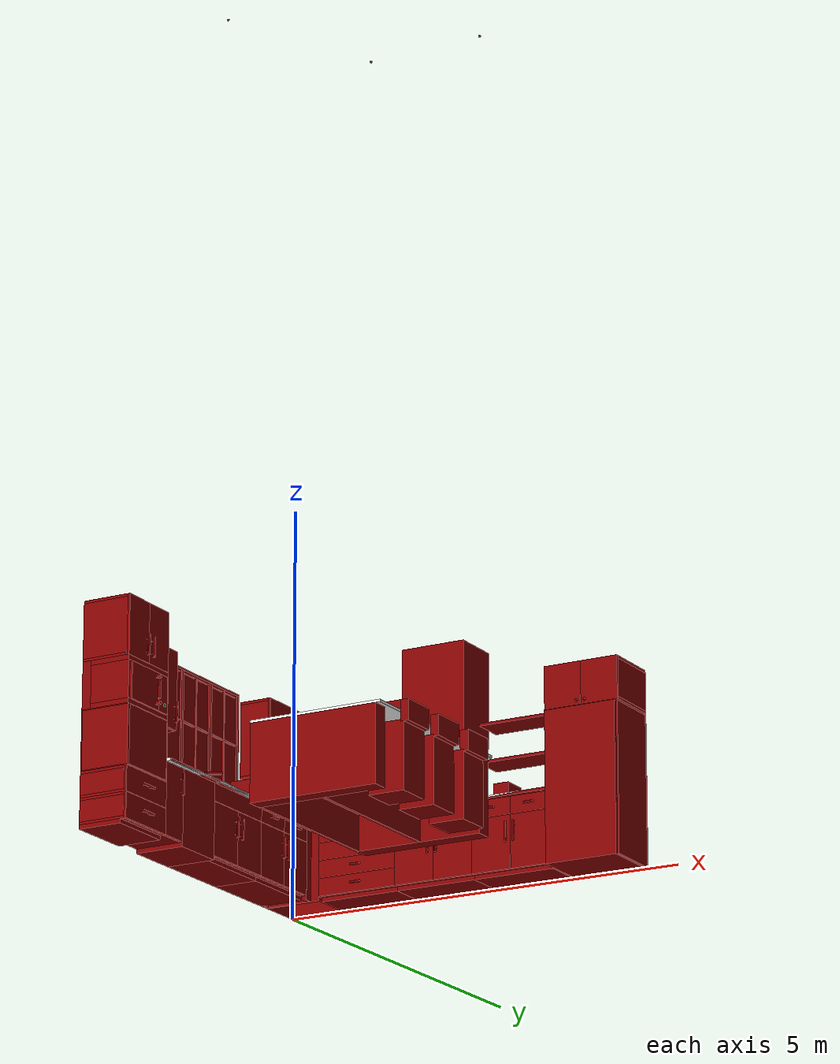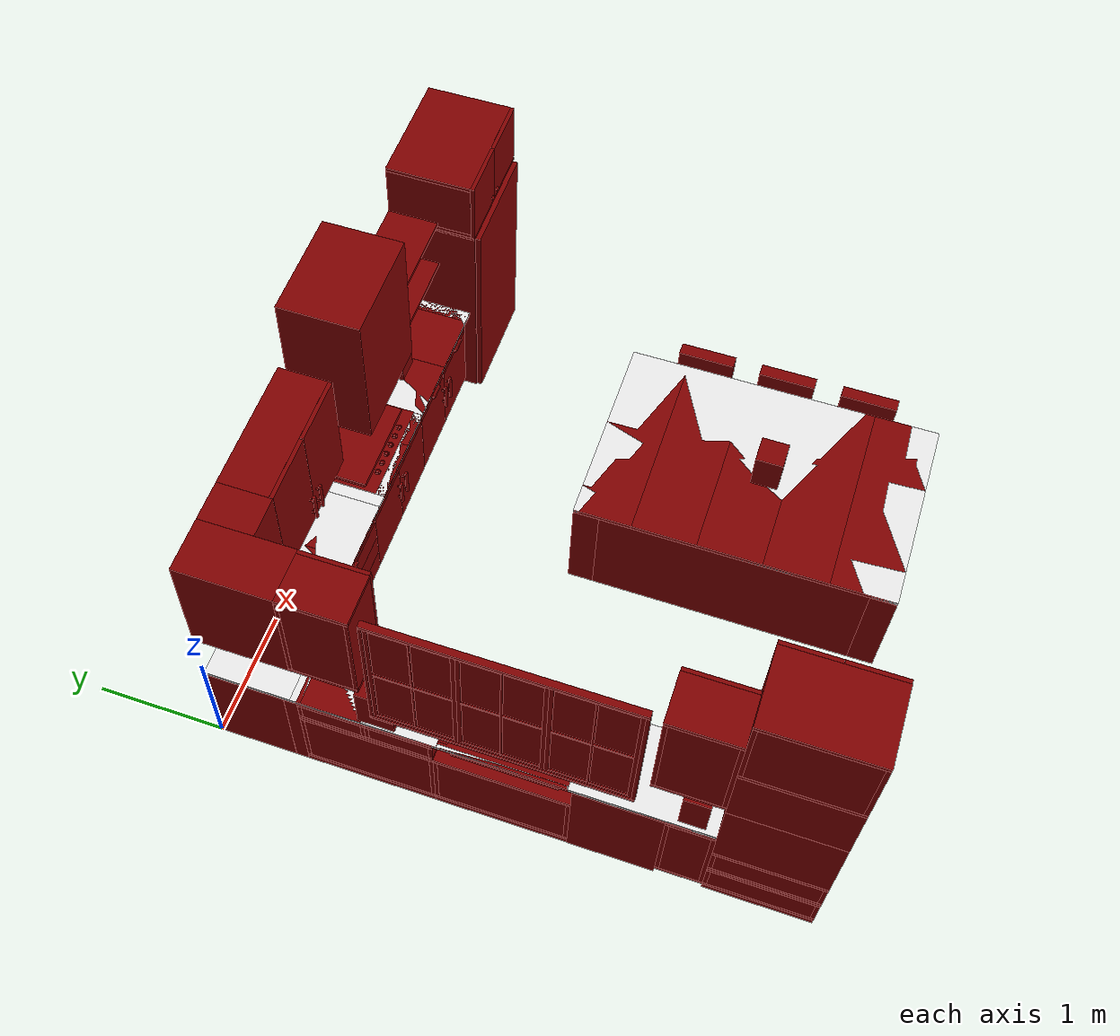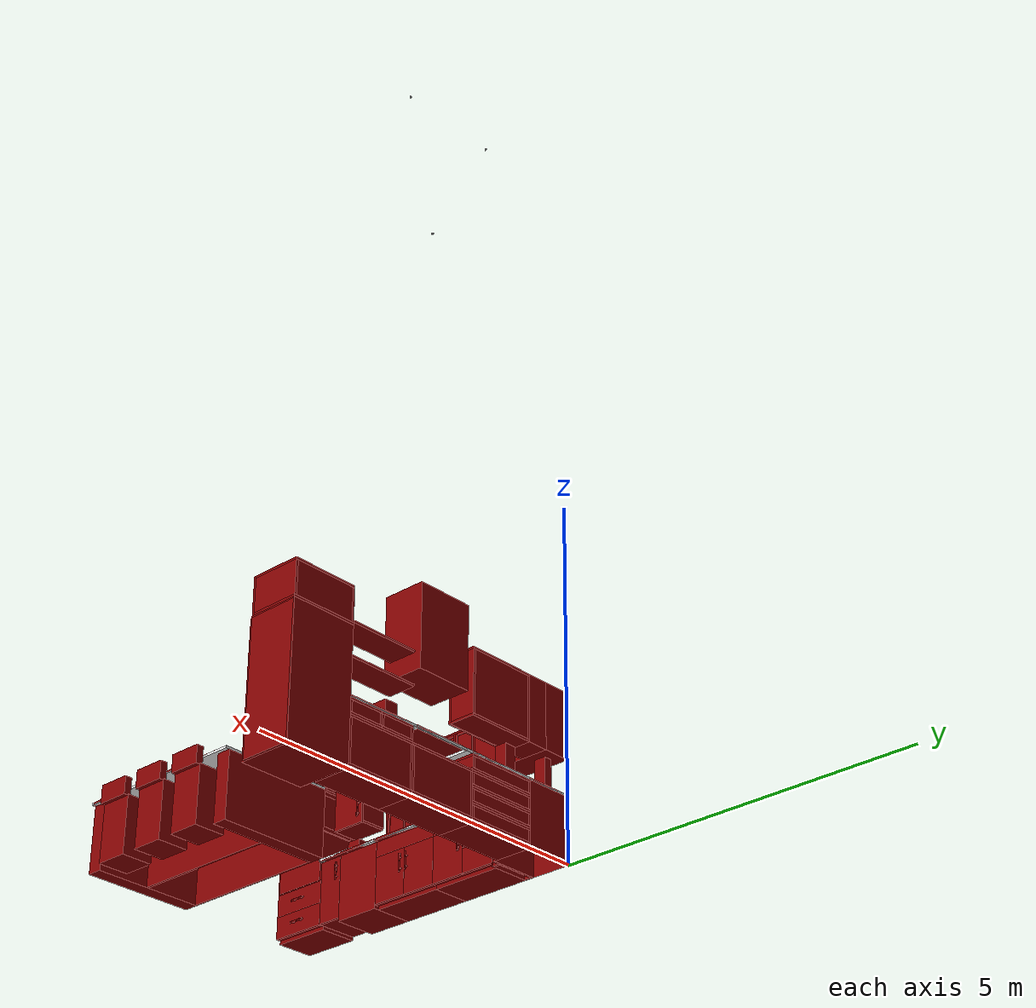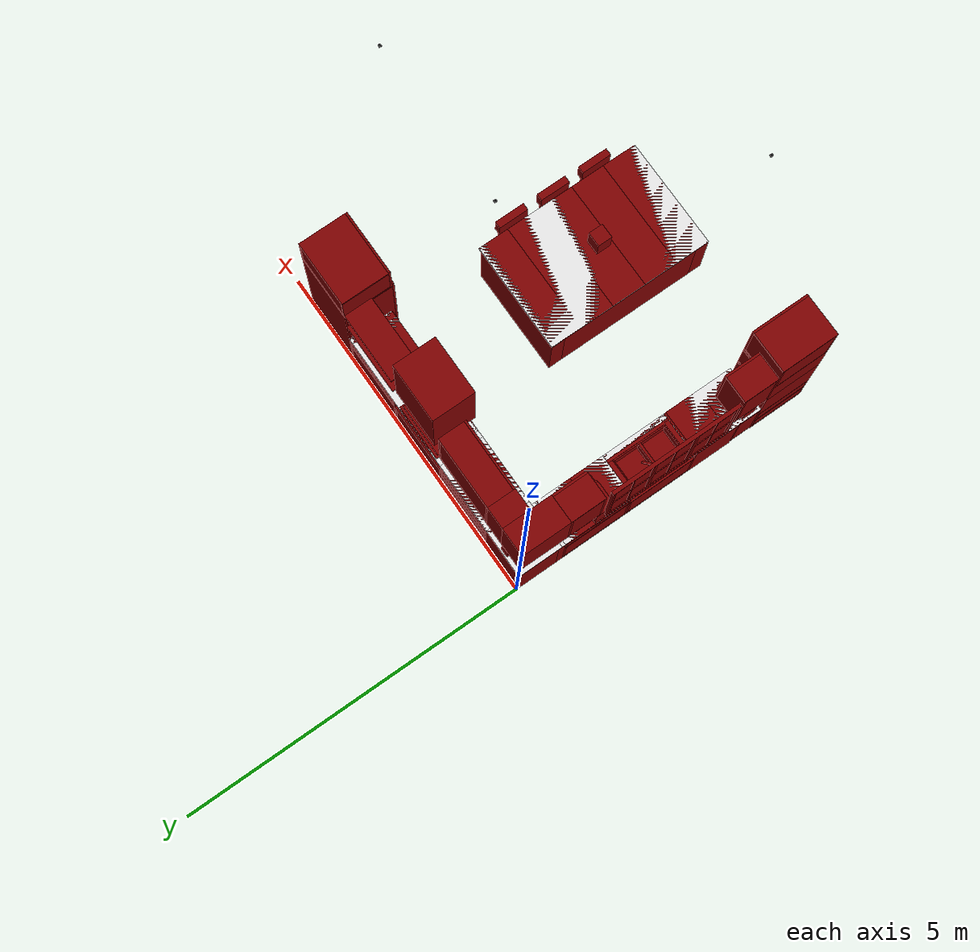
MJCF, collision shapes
<?xml version="1.0" encoding="utf-8"?>
<mujoco model="fixtures">
  <!-- ASSETS: Materials and Meshes                                         -->
  <asset>
    <!-- Common Textures Used by Fixtures -->
    <texture type="2d" colorspace="linear" name="flat/white_2d" file="assets/textures/flat/white.png"/>
    <texture type="cube" colorspace="linear" name="flat/blue_gray" file="assets/textures/flat/blue_gray.png"/>
    <texture type="2d" colorspace="linear" name="flat/blue_gray_2d" file="assets/textures/flat/blue_gray.png"/>
    <texture type="cube" colorspace="linear" name="flat/dark_gray" file="assets/textures/flat/dark_gray.png"/>
    <texture type="cube" colorspace="linear" name="box" file="assets/textures/flat/blue_gray.png"/>
    <texture type="2d" colorspace="linear" name="tex_2d" file="assets/textures/ceramic.png"/>
    <texture type="2d" colorspace="linear" name="wood/light_wood_parquet_2d" file="assets/textures/wood/light_wood_parquet.png"/>
    <texture type="2d" colorspace="sRGB" name="window_group_left_group_panel_tex" file="assets/textures/wood/dark_wood_planks.png"/>
    <texture type="2d" colorspace="linear" name="window_group_left_group_blurred_bak" file="assets/textures/flat/warm_white.png"/>

    <!-- COMMON CABINET & STACK MATERIALS                                   -->
    <!-- Used by multiple cabinet and stack fixtures throughout the kitchen -->
    <material name="box_mat" texture="box" shininess="0.1"/>

    <!-- Stack 1 Materials (Main Area) -->
    <material name="stack_1_main_group_1_mat" texture="flat/blue_gray" shininess="0.1"/>
    <material name="stack_1_main_group_1_door_mat" texture="flat/blue_gray_2d" texuniform="true" texrepeat="4 4" shininess="0.1" reflectance="0.1"/>
    <material name="stack_1_main_group_1_door_handle_mat" texture="flat/dark_gray" shininess="0.8" reflectance="0.8"/>
    <material name="stack_1_main_group_2_mat" texture="flat/blue_gray" shininess="0.1"/>
    <material name="stack_1_main_group_2_door_mat" texture="flat/blue_gray_2d" texuniform="true" texrepeat="4 4" shininess="0.1" reflectance="0.1"/>
    <material name="stack_1_main_group_2_door_handle_mat" texture="flat/dark_gray" shininess="0.8" reflectance="0.8"/>
    <material name="stack_1_main_group_3_mat" texture="flat/blue_gray" shininess="0.1"/>
    <material name="stack_1_main_group_3_door_mat" texture="flat/blue_gray_2d" texuniform="true" texrepeat="4 4" shininess="0.1" reflectance="0.1"/>
    <material name="stack_1_main_group_3_door_handle_mat" texture="flat/dark_gray" shininess="0.8" reflectance="0.8"/>
    <material name="stack_1_main_group_4_mat" texture="flat/blue_gray" shininess="0.1"/>
    <material name="stack_1_main_group_4_door_mat" texture="flat/blue_gray_2d" texuniform="true" texrepeat="4 4" shininess="0.1" reflectance="0.1"/>
    <material name="stack_1_main_group_4_door_handle_mat" texture="flat/dark_gray" shininess="0.8" reflectance="0.8"/>

    <!-- Stack 2 Materials (Main Area) -->
    <material name="stack_2_main_group_1_mat" texture="flat/blue_gray" shininess="0.1"/>
    <material name="stack_2_main_group_1_left_door_mat" texture="flat/blue_gray_2d" texuniform="true" texrepeat="4 4" shininess="0.1" reflectance="0.1"/>
    <material name="stack_2_main_group_1_left_door_handle_mat" texture="flat/dark_gray" shininess="0.8" reflectance="0.8"/>
    <material name="stack_2_main_group_1_right_door_mat" texture="flat/blue_gray_2d" texuniform="true" texrepeat="4 4" shininess="0.1" reflectance="0.1"/>
    <material name="stack_2_main_group_1_right_door_handle_mat" texture="flat/dark_gray" shininess="0.8" reflectance="0.8"/>
    <material name="stack_2_main_group_2_mat" texture="flat/blue_gray" shininess="0.8" reflectance="0.8"/>
    <material name="stack_2_main_group_2_mat_uniform" texture="tex_2d" texuniform="true" texrepeat="4 4" shininess="0.8" reflectance="0.8"/>
    <material name="stack_2_main_group_2_door_mat" texture="flat/blue_gray_2d" texuniform="true" texrepeat="4 4" shininess="0.1" reflectance="0.1"/>

    <!-- Stack 3 Materials (Main Area) -->
    <material name="stack_3_main_group_1_mat" texture="flat/blue_gray" shininess="0.1"/>
    <material name="stack_3_main_group_1_left_door_mat" texture="flat/blue_gray_2d" texuniform="true" texrepeat="4 4" shininess="0.1" reflectance="0.1"/>
    <material name="stack_3_main_group_1_left_door_handle_mat" texture="flat/dark_gray" shininess="0.8" reflectance="0.8"/>
    <material name="stack_3_main_group_1_right_door_mat" texture="flat/blue_gray_2d" texuniform="true" texrepeat="4 4" shininess="0.1" reflectance="0.1"/>
    <material name="stack_3_main_group_1_right_door_handle_mat" texture="flat/dark_gray" shininess="0.8" reflectance="0.8"/>
    <material name="stack_3_main_group_2_mat" texture="flat/blue_gray" shininess="0.1"/>
    <material name="stack_3_main_group_2_door_mat" texture="flat/blue_gray_2d" texuniform="true" texrepeat="4 4" shininess="0.1" reflectance="0.1"/>
    <material name="stack_3_main_group_2_door_handle_mat" texture="flat/dark_gray" shininess="0.8" reflectance="0.8"/>
    <material name="stack_3_main_group_3_mat" texture="flat/blue_gray" shininess="0.1"/>
    <material name="stack_3_main_group_3_door_mat" texture="flat/blue_gray_2d" texuniform="true" texrepeat="4 4" shininess="0.1" reflectance="0.1"/>
    <material name="stack_3_main_group_3_door_handle_mat" texture="flat/dark_gray" shininess="0.8" reflectance="0.8"/>

    <!-- Cabinet Materials (Main Area) -->
    <material name="cab_main_main_group_mat" texture="flat/blue_gray" shininess="0.1"/>
    <material name="cab_main_main_group_left_door_mat" texture="flat/blue_gray_2d" texuniform="true" texrepeat="4 4" shininess="0.1" reflectance="0.1"/>
    <material name="cab_main_main_group_left_door_handle_mat" texture="flat/dark_gray" shininess="0.8" reflectance="0.8"/>
    <material name="cab_main_main_group_right_door_mat" texture="flat/blue_gray_2d" texuniform="true" texrepeat="4 4" shininess="0.1" reflectance="0.1"/>
    <material name="cab_main_main_group_right_door_handle_mat" texture="flat/dark_gray" shininess="0.8" reflectance="0.8"/>

    <!-- Shelf Materials -->
    <material name="shelves_main_group_shelf_0_mat" texture="wood/light_wood_parquet_2d" texuniform="true" texrepeat="3 3" shininess="0.1" reflectance="0.1"/>
    <material name="shelves_main_group_shelf_1_mat" texture="wood/light_wood_parquet_2d" texuniform="true" texrepeat="3 3" shininess="0.1" reflectance="0.1"/>

    <!-- Cabinet Materials (Left Area) -->
    <material name="cab_1_left_group_mat" texture="flat/blue_gray" shininess="0.1"/>
    <material name="cab_1_left_group_door_mat" texture="flat/blue_gray_2d" texuniform="true" texrepeat="4 4" shininess="0.1" reflectance="0.1"/>
    <material name="cab_1_left_group_door_handle_mat" texture="flat/dark_gray" shininess="0.8" reflectance="0.8"/>

    <!-- Window Materials -->
    <material name="window_group_left_group_panel_mat" texture="window_group_left_group_panel_tex" texuniform="true" texrepeat="4 4" specular="0.1" shininess="0.1"/>
    <material name="window_group_left_group_window_mat" texture="window_group_left_group_blurred_bak" texuniform="true" specular="0.1" shininess="0.1"/>

    <!-- Cabinet 2 Materials (Left Area) -->
    <material name="cab_2_left_group_mat" texture="flat/blue_gray" shininess="0.1"/>
    <material name="cab_2_left_group_door_mat" texture="flat/blue_gray_2d" texuniform="true" texrepeat="4 4" shininess="0.1" reflectance="0.1"/>
    <material name="cab_2_left_group_door_handle_mat" texture="flat/dark_gray" shininess="0.8" reflectance="0.8"/>

    <!-- Bottom Cabinet Materials (Left Area) -->
    <material name="bottom_left_group_1_mat" texture="flat/blue_gray" shininess="0.1"/>
    <material name="bottom_left_group_1_door_mat" texture="flat/blue_gray_2d" texuniform="true" texrepeat="4 4" shininess="0.1" reflectance="0.1"/>
    <material name="bottom_left_group_1_door_handle_mat" texture="flat/dark_gray" shininess="0.8" reflectance="0.8"/>
    <material name="bottom_left_group_2_mat" texture="flat/blue_gray" shininess="0.1"/>
    <material name="bottom_left_group_2_door_mat" texture="flat/blue_gray_2d" texuniform="true" texrepeat="4 4" shininess="0.1" reflectance="0.1"/>
    <material name="bottom_left_group_2_door_handle_mat" texture="flat/dark_gray" shininess="0.8" reflectance="0.8"/>

    <!-- Top Cabinet Materials (Left Area) -->
    <material name="top_left_group_mat" texture="flat/blue_gray" shininess="0.1"/>
    <material name="top_left_group_left_door_mat" texture="flat/blue_gray_2d" texuniform="true" texrepeat="4 4" shininess="0.1" reflectance="0.1"/>
    <material name="top_left_group_left_door_handle_mat" texture="flat/dark_gray" shininess="0.8" reflectance="0.8"/>
    <material name="top_left_group_right_door_mat" texture="flat/blue_gray_2d" texuniform="true" texrepeat="4 4" shininess="0.1" reflectance="0.1"/>
    <material name="top_left_group_right_door_handle_mat" texture="flat/dark_gray" shininess="0.8" reflectance="0.8"/>

    <!-- Stack 1 Materials (Left Area) -->
    <material name="stack_1_left_group_mat" texture="flat/blue_gray" shininess="0.1"/>
    <material name="stack_1_left_group_door_mat" texture="flat/blue_gray_2d" texuniform="true" texrepeat="4 4" shininess="0.1" reflectance="0.1"/>
    <material name="stack_1_left_group_door_handle_mat" texture="flat/dark_gray" shininess="0.8" reflectance="0.8"/>

    <!-- Stack 2 Materials (Left Area) -->
    <material name="stack_2_left_group_1_mat" texture="flat/blue_gray" shininess="0.1"/>
    <material name="stack_2_left_group_1_left_door_mat" texture="flat/blue_gray_2d" texuniform="true" texrepeat="4 4" shininess="0.1" reflectance="0.1"/>
    <material name="stack_2_left_group_1_left_door_handle_mat" texture="flat/dark_gray" shininess="0.8" reflectance="0.8"/>
    <material name="stack_2_left_group_1_right_door_mat" texture="flat/blue_gray_2d" texuniform="true" texrepeat="4 4" shininess="0.1" reflectance="0.1"/>
    <material name="stack_2_left_group_1_right_door_handle_mat" texture="flat/dark_gray" shininess="0.8" reflectance="0.8"/>
    <material name="stack_2_left_group_2_mat" texture="flat/blue_gray" shininess="0.8" reflectance="0.8"/>
    <material name="stack_2_left_group_2_mat_uniform" texture="tex_2d" texuniform="true" texrepeat="4 4" shininess="0.8" reflectance="0.8"/>
    <material name="stack_2_left_group_2_door_mat" texture="flat/blue_gray_2d" texuniform="true" texrepeat="4 4" shininess="0.1" reflectance="0.1"/>

    <!-- Stack 3 Materials (Left Area) -->
    <material name="stack_3_left_group_1_mat" texture="flat/blue_gray" shininess="0.1"/>
    <material name="stack_3_left_group_1_left_door_mat" texture="flat/blue_gray_2d" texuniform="true" texrepeat="4 4" shininess="0.1" reflectance="0.1"/>
    <material name="stack_3_left_group_1_left_door_handle_mat" texture="flat/dark_gray" shininess="0.8" reflectance="0.8"/>
    <material name="stack_3_left_group_1_right_door_mat" texture="flat/blue_gray_2d" texuniform="true" texrepeat="4 4" shininess="0.1" reflectance="0.1"/>
    <material name="stack_3_left_group_1_right_door_handle_mat" texture="flat/dark_gray" shininess="0.8" reflectance="0.8"/>
    <material name="stack_3_left_group_2_mat" texture="flat/blue_gray" shininess="0.1"/>
    <material name="stack_3_left_group_2_door_mat" texture="flat/blue_gray_2d" texuniform="true" texrepeat="4 4" shininess="0.1" reflectance="0.1"/>
    <material name="stack_3_left_group_2_door_handle_mat" texture="flat/dark_gray" shininess="0.8" reflectance="0.8"/>
    <material name="stack_3_left_group_3_mat" texture="flat/blue_gray" shininess="0.1"/>
    <material name="stack_3_left_group_3_door_mat" texture="flat/blue_gray_2d" texuniform="true" texrepeat="4 4" shininess="0.1" reflectance="0.1"/>
    <material name="stack_3_left_group_3_door_handle_mat" texture="flat/dark_gray" shininess="0.8" reflectance="0.8"/>

    <!-- KITCHEN FIXTURES: Counters, Cabinets, and Surfaces               -->
    <!-- FIXTURE: Counter Corner (Main) -->
    <material name="counter_corner_main_main_group_counter_top" texture="flat/white_2d" texuniform="true" texrepeat="3 3" shininess="0.1" reflectance="0.1"/>
    <material name="counter_corner_main_main_group_counter_base" texture="flat/blue_gray" shininess="0.1" reflectance="0.1"/>

    <!-- FIXTURE: Counter Main -->
    <material name="counter_main_main_group_counter_top" texture="flat/white_2d" texuniform="true" texrepeat="3 3" shininess="0.1" reflectance="0.1"/>
    <material name="counter_main_main_group_counter_base" texture="flat/blue_gray" shininess="0.1" reflectance="0.1"/>

    <!-- FIXTURE: Counter Right -->
    <material name="counter_1_right_main_group_counter_top" texture="flat/white_2d" texuniform="true" texrepeat="3 3" shininess="0.1" reflectance="0.1"/>
    <material name="counter_1_right_main_group_counter_base" texture="flat/blue_gray" shininess="0.1" reflectance="0.1"/>

    <!-- FIXTURE: Counter Left -->
    <material name="counter_1_left_left_group_counter_top" texture="flat/white_2d" texuniform="true" texrepeat="3 3" shininess="0.1" reflectance="0.1"/>
    <material name="counter_1_left_left_group_counter_base" texture="flat/blue_gray" shininess="0.1" reflectance="0.1"/>
    <material name="counter_corner_left_group_counter_top" texture="flat/white_2d" texuniform="true" texrepeat="3 3" shininess="0.1" reflectance="0.1"/>
    <material name="counter_corner_left_group_counter_base" texture="flat/blue_gray" shininess="0.1" reflectance="0.1"/>

    <!-- FIXTURE: Island Counter (Kitchen Island with Countertop) -->
    <material name="island_left_group_counter_top" texture="flat/white_2d" texuniform="true" texrepeat="3 3" shininess="0.1" reflectance="0.1"/>
    <material name="island_left_group_counter_base" texture="flat/blue_gray" shininess="0.1" reflectance="0.1"/>

    <!-- FIXTURE: Sink -->
    <material name="sink_left_group_metal_Mat" shininess="0.36" rgba="0.8 0.8 0.8 1"/>
    <material name="sink_left_group_sink_Mat" shininess="0.36" rgba="0.8 0.8 0.8 1"/>
    <material name="sink_left_group_tap_Mat" shininess="0.36" rgba="0.8 0.8 0.8 1"/>
    <mesh name="sink_left_group_model_0_vis" content_type="model/obj" file="assets/fixtures/sinks/2_bins_stainless/visuals/model_0.obj" inertia="shell" scale="0.941781 0.941781 0.941781"/>
    <mesh name="sink_left_group_model_1_vis" content_type="model/obj" file="assets/fixtures/sinks/2_bins_stainless/visuals/model_1.obj" inertia="shell" scale="0.941781 0.941781 0.941781"/>
    <mesh name="sink_left_group_model_2_vis" content_type="model/obj" file="assets/fixtures/sinks/2_bins_stainless/visuals/model_2.obj" inertia="shell" scale="0.941781 0.941781 0.941781"/>
    <mesh name="sink_left_group_spout_0_vis" content_type="model/obj" file="assets/fixtures/sinks/2_bins_stainless/visuals/spout_0.obj" inertia="shell" scale="0.941781 0.941781 0.941781"/>
    <mesh name="sink_left_group_handle_0_vis" content_type="model/obj" file="assets/fixtures/sinks/2_bins_stainless/visuals/handle_0.obj" inertia="shell" scale="0.941781 0.941781 0.941781"/>

    <!-- KITCHEN APPLIANCES: Stovetop, Fridge, Oven, Microwave, etc.      -->
    <!-- APPLIANCE: Stovetop (Gas Range) -->
    <material name="stovetop_main_group_6_burners_gas_hob" texture="stovetop_main_group_image0" shininess="0.25"/>
    <texture type="2d" colorspace="linear" name="stovetop_main_group_image0" file="assets/fixtures/stovetops/sleek_silver_top_gas/visuals/image0.png"/>
    <mesh name="stovetop_main_group_model_0_vis" content_type="model/obj" file="assets/fixtures/stovetops/sleek_silver_top_gas/visuals/model_0.obj" inertia="shell" scale="0.808824 0.808824 0.808824"/>
    <mesh name="stovetop_main_group_knob_rear_center_0_vis" content_type="model/obj" file="assets/fixtures/stovetops/sleek_silver_top_gas/visuals/knob_rear_center_0.obj" inertia="shell" scale="0.808824 0.808824 0.808824"/>
    <mesh name="stovetop_main_group_knob_front_center_0_vis" content_type="model/obj" file="assets/fixtures/stovetops/sleek_silver_top_gas/visuals/knob_front_center_0.obj" inertia="shell" scale="0.808824 0.808824 0.808824"/>
    <mesh name="stovetop_main_group_knob_rear_right_0_vis" content_type="model/obj" file="assets/fixtures/stovetops/sleek_silver_top_gas/visuals/knob_rear_right_0.obj" inertia="shell" scale="0.808824 0.808824 0.808824"/>
    <mesh name="stovetop_main_group_knob_front_left_0_vis" content_type="model/obj" file="assets/fixtures/stovetops/sleek_silver_top_gas/visuals/knob_front_left_0.obj" inertia="shell" scale="0.808824 0.808824 0.808824"/>
    <mesh name="stovetop_main_group_knob_front_right_0_vis" content_type="model/obj" file="assets/fixtures/stovetops/sleek_silver_top_gas/visuals/knob_front_right_0.obj" inertia="shell" scale="0.808824 0.808824 0.808824"/>
    <mesh name="stovetop_main_group_knob_rear_left_0_vis" content_type="model/obj" file="assets/fixtures/stovetops/sleek_silver_top_gas/visuals/knob_rear_left_0.obj" inertia="shell" scale="0.808824 0.808824 0.808824"/>

    <!-- APPLIANCE: Refrigerator -->
    <texture type="2d" colorspace="linear" name="fridge_main_group_tex-model" file="assets/fixtures/fridges/pack_1/visuals/material_0.png"/>
    <texture type="2d" colorspace="linear" name="fridge_main_group_image23" file="assets/fixtures/fridges/pack_1/visuals/image23.png"/>
    <texture type="2d" colorspace="linear" name="fridge_main_group_image0" file="assets/fixtures/fridges/pack_1/visuals/image0.png"/>
    <material name="fridge_main_group_model" texture="fridge_main_group_tex-model" reflectance="0.5"/>
    <material name="fridge_main_group_TX_Fridge_3_1" texture="fridge_main_group_image23" shininess="0.25"/>
    <material name="fridge_main_group_TX_Fridge_3_2" texture="fridge_main_group_image0" shininess="0.25"/>
    <material name="fridge_housing_main_group_mat" texture="flat/blue_gray" shininess="0.1"/>
    <material name="fridge_cab_main_group_mat" texture="flat/blue_gray" shininess="0.1"/>
    <material name="fridge_cab_main_group_left_door_mat" texture="flat/blue_gray_2d" texuniform="true" texrepeat="4 4" shininess="0.1" reflectance="0.1"/>
    <material name="fridge_cab_main_group_left_door_handle_mat" texture="flat/dark_gray" shininess="0.8" reflectance="0.8"/>
    <material name="fridge_cab_main_group_right_door_mat" texture="flat/blue_gray_2d" texuniform="true" texrepeat="4 4" shininess="0.1" reflectance="0.1"/>
    <material name="fridge_cab_main_group_right_door_handle_mat" texture="flat/dark_gray" shininess="0.8" reflectance="0.8"/>
    <mesh name="fridge_main_group_model_0_vis" content_type="model/obj" file="assets/fixtures/fridges/pack_1/visuals/model_0.obj" inertia="shell" scale="1.78 1.78 1.78"/>
    <mesh name="fridge_main_group_model_1_vis" content_type="model/obj" file="assets/fixtures/fridges/pack_1/visuals/model_1.obj" inertia="shell" scale="1.78 1.78 1.78"/>

    <!-- APPLIANCE: Kitchen Hood (Range Hood) -->
    <texture type="2d" colorspace="linear" name="hood_main_group_tex-model" file="assets/fixtures/hoods/pack_1/visuals/material_0.png"/>
    <texture type="2d" colorspace="linear" name="hood_main_group_image35" file="assets/fixtures/hoods/pack_1/visuals/image35.png"/>
    <material name="hood_main_group_model" texture="hood_main_group_tex-model" reflectance="0.5"/>
    <material name="hood_main_group_TX_Kitche_Hood_3" texture="hood_main_group_image35" shininess="0.25"/>
    <mesh name="hood_main_group_model_0_vis" content_type="model/obj" file="assets/fixtures/hoods/pack_1/visuals/model_0.obj" inertia="shell" scale="1.15688 1.10241 1.15688"/>

    <!-- APPLIANCE: Toaster -->
    <texture type="2d" colorspace="linear" name="toaster_main_group_tex-model" file="assets/fixtures/toasters/vintage/visuals/material_0.png"/>
    <texture type="2d" colorspace="linear" name="toaster_main_group_image0" file="assets/fixtures/toasters/vintage/visuals/image0.png"/>
    <material name="toaster_main_group_model" texture="toaster_main_group_tex-model" reflectance="0.5"/>
    <material name="toaster_main_group_toaster" texture="toaster_main_group_image0" shininess="0.25"/>
    <mesh name="toaster_main_group_model_0_vis" content_type="model/obj" file="assets/fixtures/toasters/vintage/visuals/model_0.obj" inertia="shell" scale="0.3 0.3 0.3"/>

    <!-- APPLIANCE: Oven -->
    <texture type="2d" colorspace="linear" name="oven_left_group_tex-model" file="assets/fixtures/ovens/pack_1/visuals/material_0.png"/>
    <texture type="2d" colorspace="linear" name="oven_left_group_image25" file="assets/fixtures/ovens/pack_1/visuals/image25.png"/>
    <texture type="2d" colorspace="linear" name="oven_left_group_image28" file="assets/fixtures/ovens/pack_1/visuals/image28.png"/>
    <texture type="2d" colorspace="linear" name="oven_left_group_image31" file="assets/fixtures/ovens/pack_1/visuals/image31.png"/>
    <material name="oven_left_group_model" texture="oven_left_group_tex-model" reflectance="0.5"/>
    <material name="oven_left_group_TX_Stove_3_3" texture="oven_left_group_image25" shininess="0.25"/>
    <material name="oven_left_group_TX_Stove_3_4" texture="oven_left_group_image28" shininess="0.25"/>
    <material name="oven_left_group_TX_Stove_3_5" texture="oven_left_group_image31" shininess="0.25"/>
    <material name="oven_housing_left_group_mat" texture="flat/blue_gray" shininess="0.1"/>
    <mesh name="oven_left_group_model_0_vis" content_type="model/obj" file="assets/fixtures/ovens/pack_1/visuals/model_0.obj" inertia="shell" scale="0.779407 0.722972 0.68"/>
    <mesh name="oven_left_group_model_1_vis" content_type="model/obj" file="assets/fixtures/ovens/pack_1/visuals/model_1.obj" inertia="shell" scale="0.779407 0.722972 0.68"/>
    <mesh name="oven_left_group_model_2_vis" content_type="model/obj" file="assets/fixtures/ovens/pack_1/visuals/model_2.obj" inertia="shell" scale="0.779407 0.722972 0.68"/>

    <!-- APPLIANCE: Microwave -->
    <texture type="2d" colorspace="linear" name="microwave_left_group_tex-model" file="assets/fixtures/microwaves/pack_1/visuals/material_0.png"/>
    <texture type="2d" colorspace="linear" name="microwave_left_group_image7" file="assets/fixtures/microwaves/pack_1/visuals/image7.png"/>
    <texture type="2d" colorspace="linear" name="microwave_left_group_image2" file="assets/fixtures/microwaves/pack_1/visuals/image2.png"/>
    <texture type="2d" colorspace="linear" name="microwave_left_group_image5" file="assets/fixtures/microwaves/pack_1/visuals/image5.png"/>
    <material name="micro_housing_left_group_mat" texture="flat/blue_gray" shininess="0.1"/>
    <material name="microwave_left_group_model" texture="microwave_left_group_tex-model" reflectance="0.5"/>
    <material name="microwave_left_group_TX_Microwave_3_1" texture="microwave_left_group_image7" shininess="0.25"/>
    <material name="microwave_left_group_TX_Microwave_3_2" texture="microwave_left_group_image2" shininess="0.25"/>
    <material name="microwave_left_group_TX_Microwave_3_3" texture="microwave_left_group_image5" shininess="0.25"/>
    <mesh name="microwave_left_group_model_0_vis" content_type="model/obj" file="assets/fixtures/microwaves/pack_1/visuals/model_0.obj" inertia="shell" scale="0.773196 0.572738 0.773196"/>
    <mesh name="microwave_left_group_model_1_vis" content_type="model/obj" file="assets/fixtures/microwaves/pack_1/visuals/model_1.obj" inertia="shell" scale="0.773196 0.572738 0.773196"/>
    <mesh name="microwave_left_group_model_2_vis" content_type="model/obj" file="assets/fixtures/microwaves/pack_1/visuals/model_2.obj" inertia="shell" scale="0.773196 0.572738 0.773196"/>
    <mesh name="microwave_left_group_door_0_vis" content_type="model/obj" file="assets/fixtures/microwaves/pack_1/visuals/door_0.obj" inertia="shell" scale="0.773196 0.572738 0.773196"/>
    <mesh name="microwave_left_group_door_1_vis" content_type="model/obj" file="assets/fixtures/microwaves/pack_1/visuals/door_1.obj" inertia="shell" scale="0.773196 0.572738 0.773196"/>
    <mesh name="microwave_left_group_door_2_vis" content_type="model/obj" file="assets/fixtures/microwaves/pack_1/visuals/door_2.obj" inertia="shell" scale="0.773196 0.572738 0.773196"/>

    <!-- APPLIANCE: Dishwasher -->
    <texture type="2d" colorspace="linear" name="dishwasher_left_group_tex-model" file="assets/fixtures/dishwashers/pack_1/visuals/material_0.png"/>
    <texture type="2d" colorspace="linear" name="dishwasher_left_group_image9" file="assets/fixtures/dishwashers/pack_1/visuals/image9.png"/>
    <texture type="2d" colorspace="linear" name="dishwasher_left_group_image13" file="assets/fixtures/dishwashers/pack_1/visuals/image13.png"/>
    <material name="dishwasher_left_group_model" texture="dishwasher_left_group_tex-model" reflectance="0.5"/>
    <material name="dishwasher_left_group_TX_Dishwasher_3_1" texture="dishwasher_left_group_image9" shininess="0.25"/>
    <material name="dishwasher_left_group_TX_Dishwasher_3_2" texture="dishwasher_left_group_image13" shininess="0.25"/>
    <mesh name="dishwasher_left_group_model_0_vis" content_type="model/obj" file="assets/fixtures/dishwashers/pack_1/visuals/model_0.obj" inertia="shell" scale="0.887868 0.828685 0.89"/>
    <mesh name="dishwasher_left_group_model_1_vis" content_type="model/obj" file="assets/fixtures/dishwashers/pack_1/visuals/model_1.obj" inertia="shell" scale="0.887868 0.828685 0.89"/>

    <!-- APPLIANCE: Coffee Machine -->
    <texture type="2d" colorspace="linear" name="coffee_machine_left_group_tex-model" file="assets/fixtures/coffee_machines/delonghi_espresso_2/visuals/material_0.png"/>
    <texture type="2d" colorspace="linear" name="coffee_machine_left_group_image3" file="assets/fixtures/coffee_machines/delonghi_espresso_2/visuals/image3.png"/>
    <texture type="2d" colorspace="linear" name="coffee_machine_left_group_image0" file="assets/fixtures/coffee_machines/delonghi_espresso_2/visuals/image0.png"/>
    <texture type="2d" colorspace="linear" name="coffee_machine_left_group_image8" file="assets/fixtures/coffee_machines/delonghi_espresso_2/visuals/image8.png"/>
    <texture type="2d" colorspace="linear" name="coffee_machine_left_group_image1" file="assets/fixtures/coffee_machines/delonghi_espresso_2/visuals/image1.png"/>
    <texture type="2d" colorspace="linear" name="coffee_machine_left_group_image6" file="assets/fixtures/coffee_machines/delonghi_espresso_2/visuals/image6.png"/>
    <texture type="2d" colorspace="linear" name="coffee_machine_left_group_image10" file="assets/fixtures/coffee_machines/delonghi_espresso_2/visuals/image10.png"/>
    <texture type="2d" colorspace="linear" name="coffee_machine_left_group_image12" file="assets/fixtures/coffee_machines/delonghi_espresso_2/visuals/image12.png"/>
    <material name="coffee_machine_left_group_model" texture="coffee_machine_left_group_tex-model" reflectance="0.5"/>
    <material name="coffee_machine_left_group_Black_Plastic" shininess="0.7744" rgba="0 0 0 1"/>
    <material name="coffee_machine_left_group_White_Plastic" shininess="0.7744" rgba="0.552941 0.552941 0.552941 1"/>
    <material name="coffee_machine_left_group_back" texture="coffee_machine_left_group_image3" shininess="0.7744"/>
    <material name="coffee_machine_left_group_cap_milk" texture="coffee_machine_left_group_image0" shininess="0.7744"/>
    <material name="coffee_machine_left_group_cap_milk_alu" texture="coffee_machine_left_group_image8" shininess="0.25"/>
    <material name="coffee_machine_left_group_front_panel" texture="coffee_machine_left_group_image1" shininess="0.81"/>
    <material name="coffee_machine_left_group_front_panel_2" texture="coffee_machine_left_group_image6" shininess="0.7744"/>
    <material name="coffee_machine_left_group_front_panel_display" texture="coffee_machine_left_group_image10" shininess="0.7744"/>
    <material name="coffee_machine_left_group_glass" shininess="0.81" rgba="0.54902 0.54902 0.54902 1"/>
    <material name="coffee_machine_left_group_logo" texture="coffee_machine_left_group_image12" shininess="0.25"/>
    <material name="coffee_machine_left_group_material" shininess="0.81"/>
    <material name="coffee_machine_left_group_panel_trims" shininess="0.81"/>
    <material name="coffee_machine_left_group_top_panel_alu" shininess="0.81"/>
    <mesh name="coffee_machine_left_group_model_0_vis" content_type="model/obj" file="assets/fixtures/coffee_machines/delonghi_espresso_2/visuals/model_0.obj" inertia="shell" scale="0.501402 0.501402 0.501402"/>
    <mesh name="coffee_machine_left_group_model_1_vis" content_type="model/obj" file="assets/fixtures/coffee_machines/delonghi_espresso_2/visuals/model_1.obj" inertia="shell" scale="0.501402 0.501402 0.501402"/>
    <mesh name="coffee_machine_left_group_model_2_vis" content_type="model/obj" file="assets/fixtures/coffee_machines/delonghi_espresso_2/visuals/model_2.obj" inertia="shell" scale="0.501402 0.501402 0.501402"/>
    <mesh name="coffee_machine_left_group_model_3_vis" content_type="model/obj" file="assets/fixtures/coffee_machines/delonghi_espresso_2/visuals/model_3.obj" inertia="shell" scale="0.501402 0.501402 0.501402"/>
    <mesh name="coffee_machine_left_group_model_4_vis" content_type="model/obj" file="assets/fixtures/coffee_machines/delonghi_espresso_2/visuals/model_4.obj" inertia="shell" scale="0.501402 0.501402 0.501402"/>
    <mesh name="coffee_machine_left_group_model_5_vis" content_type="model/obj" file="assets/fixtures/coffee_machines/delonghi_espresso_2/visuals/model_5.obj" inertia="shell" scale="0.501402 0.501402 0.501402"/>
    <mesh name="coffee_machine_left_group_model_6_vis" content_type="model/obj" file="assets/fixtures/coffee_machines/delonghi_espresso_2/visuals/model_6.obj" inertia="shell" scale="0.501402 0.501402 0.501402"/>
    <mesh name="coffee_machine_left_group_model_7_vis" content_type="model/obj" file="assets/fixtures/coffee_machines/delonghi_espresso_2/visuals/model_7.obj" inertia="shell" scale="0.501402 0.501402 0.501402"/>
    <mesh name="coffee_machine_left_group_model_8_vis" content_type="model/obj" file="assets/fixtures/coffee_machines/delonghi_espresso_2/visuals/model_8.obj" inertia="shell" scale="0.501402 0.501402 0.501402"/>
    <mesh name="coffee_machine_left_group_model_9_vis" content_type="model/obj" file="assets/fixtures/coffee_machines/delonghi_espresso_2/visuals/model_9.obj" inertia="shell" scale="0.501402 0.501402 0.501402"/>
    <mesh name="coffee_machine_left_group_model_10_vis" content_type="model/obj" file="assets/fixtures/coffee_machines/delonghi_espresso_2/visuals/model_10.obj" inertia="shell" scale="0.501402 0.501402 0.501402"/>
    <mesh name="coffee_machine_left_group_model_11_vis" content_type="model/obj" file="assets/fixtures/coffee_machines/delonghi_espresso_2/visuals/model_11.obj" inertia="shell" scale="0.501402 0.501402 0.501402"/>
    <mesh name="coffee_machine_left_group_model_12_vis" content_type="model/obj" file="assets/fixtures/coffee_machines/delonghi_espresso_2/visuals/model_12.obj" inertia="shell" scale="0.501402 0.501402 0.501402"/>

    <!-- ACCESSORIES: Utensils, Decorations, and Small Items              -->
    <!-- ACCESSORY: Utensil Holder -->
    <texture type="2d" colorspace="linear" name="utensil_holder_main_group_tex-model" file="assets/fixtures/accessories/utensil_holders/holder_2/visuals/material_0.png"/>
    <texture type="2d" colorspace="linear" name="utensil_holder_main_group_image3" file="assets/fixtures/accessories/utensil_holders/holder_2/visuals/image3.png"/>
    <texture type="2d" colorspace="linear" name="utensil_holder_main_group_image0" file="assets/fixtures/accessories/utensil_holders/holder_2/visuals/image0.png"/>
    <material name="utensil_holder_main_group_model" texture="utensil_holder_main_group_tex-model" reflectance="0.5"/>
    <material name="utensil_holder_main_group_MI_Plastic_Smooth_Low_White" shininess="0.64" rgba="0.801495 0.801495 0.801495 1"/>
    <material name="utensil_holder_main_group_M_Glass_Incolor_Refra_High" shininess="0.81" rgba="0.8 0.8 0.8 1"/>
    <material name="utensil_holder_main_group_Silver_Ag_scnpagqp_inst" texture="utensil_holder_main_group_image3" shininess="0.25"/>
    <material name="utensil_holder_main_group_wood_036" texture="utensil_holder_main_group_image0" shininess="0.25"/>
    <mesh name="utensil_holder_main_group_model_0_vis" content_type="model/obj" file="assets/fixtures/accessories/utensil_holders/holder_2/visuals/model_0.obj" inertia="shell" scale="0.35 0.35 0.35"/>
    <mesh name="utensil_holder_main_group_model_1_vis" content_type="model/obj" file="assets/fixtures/accessories/utensil_holders/holder_2/visuals/model_1.obj" inertia="shell" scale="0.35 0.35 0.35"/>
    <mesh name="utensil_holder_main_group_model_2_vis" content_type="model/obj" file="assets/fixtures/accessories/utensil_holders/holder_2/visuals/model_2.obj" inertia="shell" scale="0.35 0.35 0.35"/>
    <mesh name="utensil_holder_main_group_model_3_vis" content_type="model/obj" file="assets/fixtures/accessories/utensil_holders/holder_2/visuals/model_3.obj" inertia="shell" scale="0.35 0.35 0.35"/>

    <!-- ACCESSORY: Paper Towel Holder -->
    <texture type="2d" colorspace="linear" name="paper_towel_left_group_tex-model" file="assets/fixtures/accessories/paper_towel_holders/holder_2/visuals/material_0.png"/>
    <texture type="2d" colorspace="linear" name="paper_towel_left_group_image0" file="assets/fixtures/accessories/paper_towel_holders/holder_2/visuals/image0.png"/>
    <texture type="2d" colorspace="linear" name="paper_towel_left_group_image1" file="assets/fixtures/accessories/paper_towel_holders/holder_2/visuals/image1.png"/>
    <material name="paper_towel_left_group_model" texture="paper_towel_left_group_tex-model" reflectance="0.5"/>
    <material name="paper_towel_left_group_metal" shininess="0.0553676" rgba="0.35595 0.35595 0.35595 1"/>
    <material name="paper_towel_left_group_paperSide" texture="paper_towel_left_group_image0" shininess="0"/>
    <material name="paper_towel_left_group_paperTopAndBottom" texture="paper_towel_left_group_image1" shininess="0"/>
    <material name="paper_towel_left_group_paperboard" shininess="0" rgba="0.327778 0.266356 0.198069 1"/>
    <mesh name="paper_towel_left_group_model_0_vis" file="assets/fixtures/accessories/paper_towel_holders/holder_2/visuals/model_0.obj" inertia="shell" scale="0.35 0.35 0.35"/>
    <mesh name="paper_towel_left_group_model_1_vis" file="assets/fixtures/accessories/paper_towel_holders/holder_2/visuals/model_1.obj" inertia="shell" scale="0.35 0.35 0.35"/>
    <mesh name="paper_towel_left_group_model_2_vis" file="assets/fixtures/accessories/paper_towel_holders/holder_2/visuals/model_2.obj" inertia="shell" scale="0.35 0.35 0.35"/>
    <mesh name="paper_towel_left_group_model_3_vis" file="assets/fixtures/accessories/paper_towel_holders/holder_2/visuals/model_3.obj" inertia="shell" scale="0.35 0.35 0.35"/>

    <!-- ACCESSORY: Knife Block -->
    <texture type="2d" colorspace="linear" name="knife_block_left_group_tex-model" file="assets/fixtures/accessories/knife_blocks/light_wood_3/visuals/material_0.png"/>
    <texture type="2d" colorspace="linear" name="knife_block_left_group_image0" file="assets/fixtures/accessories/knife_blocks/light_wood_3/visuals/image0.png"/>
    <material name="knife_block_left_group_model" texture="knife_block_left_group_tex-model" reflectance="0.5"/>
    <material name="knife_block_left_group_Knife_rack" texture="knife_block_left_group_image0" shininess="0.25"/>
    <mesh name="knife_block_left_group_model_0_vis" content_type="model/obj" file="assets/fixtures/accessories/knife_blocks/light_wood_3/visuals/model_0.obj" inertia="shell" scale="0.381892 0.381892 0.381892"/>

    <!-- ACCESSORY: Decorative Plant -->
    <texture type="2d" colorspace="linear" name="plant_left_group_tex-model" file="assets/fixtures/accessories/plants/aloe/visuals/material_0.png"/>
    <texture type="2d" colorspace="linear" name="plant_left_group_image0" file="assets/fixtures/accessories/plants/aloe/visuals/image0.png"/>
    <texture type="2d" colorspace="linear" name="plant_left_group_image1" file="assets/fixtures/accessories/plants/aloe/visuals/image1.png"/>
    <texture type="2d" colorspace="linear" name="plant_left_group_image2" file="assets/fixtures/accessories/plants/aloe/visuals/image2.png"/>
    <texture type="2d" colorspace="linear" name="plant_left_group_image3" file="assets/fixtures/accessories/plants/aloe/visuals/image3.png"/>
    <material name="plant_left_group_model" texture="plant_left_group_tex-model" reflectance="0.5"/>
    <material name="plant_left_group_blinn1SG" texture="plant_left_group_image0" shininess="0.16"/>
    <material name="plant_left_group_blinn2SG" texture="plant_left_group_image1" shininess="0.16"/>
    <material name="plant_left_group_blinn3SG" texture="plant_left_group_image2" shininess="0.16"/>
    <material name="plant_left_group_blinn4SG" texture="plant_left_group_image3" shininess="0"/>
    <mesh name="plant_left_group_model_0_vis" content_type="model/obj" file="assets/fixtures/accessories/plants/aloe/visuals/model_0.obj" inertia="shell" scale="0.3 0.3 0.3"/>
    <mesh name="plant_left_group_model_1_vis" content_type="model/obj" file="assets/fixtures/accessories/plants/aloe/visuals/model_1.obj" inertia="shell" scale="0.3 0.3 0.3"/>
    <mesh name="plant_left_group_model_2_vis" content_type="model/obj" file="assets/fixtures/accessories/plants/aloe/visuals/model_2.obj" inertia="shell" scale="0.3 0.3 0.3"/>
    <mesh name="plant_left_group_model_3_vis" content_type="model/obj" file="assets/fixtures/accessories/plants/aloe/visuals/model_3.obj" inertia="shell" scale="0.3 0.3 0.3"/>

    <!-- FURNITURE: Stools and Seating                                     -->
    <!-- FURNITURE: Stool 1 -->
    <texture type="2d" colorspace="linear" name="stool_1_stool_group_tex-model" file="assets/fixtures/accessories/stools/rattan_stool/visuals/material_0.png"/>
    <texture type="2d" colorspace="linear" name="stool_1_stool_group_image0" file="assets/fixtures/accessories/stools/rattan_stool/visuals/image0.png"/>
    <material name="stool_1_stool_group_model" texture="stool_1_stool_group_tex-model" reflectance="0.5"/>
    <material name="stool_1_stool_group_HBS_0001_M1" texture="stool_1_stool_group_image0" shininess="0.25"/>
    <mesh name="stool_1_stool_group_model_0_vis" content_type="model/obj" file="assets/fixtures/accessories/stools/rattan_stool/visuals/model_0.obj" inertia="shell"/>

    <!-- FURNITURE: Stool 2 -->
    <texture type="2d" colorspace="linear" name="stool_2_stool_group_tex-model" file="assets/fixtures/accessories/stools/rattan_stool/visuals/material_0.png"/>
    <texture type="2d" colorspace="linear" name="stool_2_stool_group_image0" file="assets/fixtures/accessories/stools/rattan_stool/visuals/image0.png"/>
    <material name="stool_2_stool_group_model" texture="stool_2_stool_group_tex-model" reflectance="0.5"/>
    <material name="stool_2_stool_group_HBS_0001_M1" texture="stool_2_stool_group_image0" shininess="0.25"/>
    <mesh name="stool_2_stool_group_model_0_vis" content_type="model/obj" file="assets/fixtures/accessories/stools/rattan_stool/visuals/model_0.obj" inertia="shell"/>

    <!-- FURNITURE: Stool 3 -->
    <texture type="2d" colorspace="linear" name="stool_3_stool_group_tex-model" file="assets/fixtures/accessories/stools/rattan_stool/visuals/material_0.png"/>
    <texture type="2d" colorspace="linear" name="stool_3_stool_group_image0" file="assets/fixtures/accessories/stools/rattan_stool/visuals/image0.png"/>
    <material name="stool_3_stool_group_model" texture="stool_3_stool_group_tex-model" reflectance="0.5"/>
    <material name="stool_3_stool_group_HBS_0001_M1" texture="stool_3_stool_group_image0" shininess="0.25"/>
    <mesh name="stool_3_stool_group_model_0_vis" content_type="model/obj" file="assets/fixtures/accessories/stools/rattan_stool/visuals/model_0.obj" inertia="shell"/>

  </asset>

  <!-- WORLDBODY: Physical Fixture Bodies                                   -->
  <worldbody>
    <!-- KITCHEN FIXTURES: Counters, Cabinets, and Surfaces               -->
    <!-- FIXTURE: Counter Corner (Main) -->
    <body name="counter_corner_main_main_group_main" pos="0.35 -0.325 0.46">
      <geom name="counter_corner_main_main_group_base_right" size="0.0001 0.3 0.445" pos="0.3499 0.025 -0.015" type="box" rgba="0.5 0 0 1"/>
      <geom name="counter_corner_main_main_group_base_left" size="0.0001 0.3 0.445" pos="-0.3499 0.025 -0.015" type="box" rgba="0.5 0 0 1"/>
      <geom name="counter_corner_main_main_group_base_back" size="0.3498 0.015 0.445" pos="0 0.31 -0.015" type="box" rgba="0.5 0 0 1"/>
      <geom name="counter_corner_main_main_group_base_front" size="0.3498 0.015 0.445" pos="0 -0.26 -0.015" type="box" rgba="0.5 0 0 1"/>
      <geom name="counter_corner_main_main_group_base_right_visual" size="0.0001 0.3 0.445" pos="0.3499 0.025 -0.015" type="box" contype="0" conaffinity="0" group="1" material="counter_corner_main_main_group_counter_base"/>
      <geom name="counter_corner_main_main_group_base_left_visual" size="0.0001 0.3 0.445" pos="-0.3499 0.025 -0.015" type="box" contype="0" conaffinity="0" group="1" material="counter_corner_main_main_group_counter_base"/>
      <geom name="counter_corner_main_main_group_base_back_visual" size="0.3498 0.015 0.445" pos="0 0.31 -0.015" type="box" contype="0" conaffinity="0" group="1" material="counter_corner_main_main_group_counter_base"/>
      <geom name="counter_corner_main_main_group_base_front_visual" size="0.3498 0.015 0.445" pos="0 -0.26 -0.015" type="box" contype="0" conaffinity="0" group="1" material="counter_corner_main_main_group_counter_base"/>
      <geom name="counter_corner_main_main_group_top_visual" size="0.35 0.325 0.015" pos="0 0 0.445" type="box" contype="0" conaffinity="0" group="1" material="counter_corner_main_main_group_counter_top"/>
      <geom name="counter_corner_main_main_group_top_0" size="0.25 0.325 0.015" pos="-0.1 0 0.445" type="box" rgba="0.5 0 0 1"/>
      <geom name="counter_corner_main_main_group_top_1" size="0.1 0.325 0.015" pos="0.25 0 0.445" type="box" rgba="0.5 0 0 1"/>
      <site name="counter_corner_main_main_group_ext_p0" pos="-0.35 -0.275 -0.46" size="0.01" rgba="0 0 0 0"/>
      <site name="counter_corner_main_main_group_ext_px" pos="0.35 -0.275 -0.46" size="0.01" rgba="1 0 0 0"/>
      <site name="counter_corner_main_main_group_ext_py" pos="-0.35 0.325 -0.46" size="0.01" rgba="0 1 0 0"/>
      <site name="counter_corner_main_main_group_ext_pz" pos="-0.35 -0.275 0.46" size="0.01" rgba="0 0 1 0"/>
      <site name="counter_corner_main_main_group_int_p0" pos="0 0 0" size="0.01" rgba="0.5 0.5 0.5 0"/>
      <site name="counter_corner_main_main_group_int_px" pos="0 0 0" size="0.01" rgba="1 1 0 0"/>
      <site name="counter_corner_main_main_group_int_py" pos="0 0 0" size="0.01" rgba="0 1 1 0"/>
      <site name="counter_corner_main_main_group_int_pz" pos="0 0 0" size="0.01" rgba="1 0 1 0"/>
      <site name="counter_corner_main_main_group_default_site" pos="0 0 0" size="0.002" rgba="1 0 0 0"/>
    </body>
    <!-- FIXTURE: Counter Main -->
    <body name="counter_main_main_group_main" pos="1.2 -0.325 0.46">
      <geom name="counter_main_main_group_base_right" size="0.01 0.01 0.01" pos="0 0 10" type="box" rgba="0 0 0 0"/>
      <geom name="counter_main_main_group_base_left" size="0.01 0.01 0.01" pos="0 0 10" type="box" rgba="0 0 0 0"/>
      <geom name="counter_main_main_group_base_back" size="0.01 0.01 0.01" pos="0 0 10" type="box" rgba="0 0 0 0"/>
      <geom name="counter_main_main_group_base_front" size="0.01 0.01 0.01" pos="0 0 10" type="box" rgba="0 0 0 0"/>
      <geom name="counter_main_main_group_base_right_visual" size="0.01 0.01 0.01" pos="0 0 10" type="box" contype="0" conaffinity="0" group="1" material="counter_main_main_group_counter_base" rgba="0 0 0 0"/>
      <geom name="counter_main_main_group_base_left_visual" size="0.01 0.01 0.01" pos="0 0 10" type="box" contype="0" conaffinity="0" group="1" material="counter_main_main_group_counter_base" rgba="0 0 0 0"/>
      <geom name="counter_main_main_group_base_back_visual" size="0.01 0.01 0.01" pos="0 0 10" type="box" contype="0" conaffinity="0" group="1" material="counter_main_main_group_counter_base" rgba="0 0 0 0"/>
      <geom name="counter_main_main_group_base_front_visual" size="0.01 0.01 0.01" pos="0 0 10" type="box" contype="0" conaffinity="0" group="1" material="counter_main_main_group_counter_base" rgba="0 0 0 0"/>
      <geom name="counter_main_main_group_top_visual" size="0.5 0.325 0.015" pos="0 0 0.445" type="box" contype="0" conaffinity="0" group="1" material="counter_main_main_group_counter_top"/>
      <geom name="counter_main_main_group_top_0" size="0.25 0.325 0.015" pos="-0.25 0 0.445" type="box" rgba="0.5 0 0 1"/>
      <geom name="counter_main_main_group_top_1" size="0.25 0.325 0.015" pos="0.25 0 0.445" type="box" rgba="0.5 0 0 1"/>
      <site name="counter_main_main_group_ext_p0" pos="-0.5 -0.275 -0.46" size="0.01" rgba="0 0 0 0"/>
      <site name="counter_main_main_group_ext_px" pos="0.5 -0.275 -0.46" size="0.01" rgba="1 0 0 0"/>
      <site name="counter_main_main_group_ext_py" pos="-0.5 0.325 -0.46" size="0.01" rgba="0 1 0 0"/>
      <site name="counter_main_main_group_ext_pz" pos="-0.5 -0.275 0.46" size="0.01" rgba="0 0 1 0"/>
      <site name="counter_main_main_group_int_p0" pos="0 0 0" size="0.01" rgba="0.5 0.5 0.5 0"/>
      <site name="counter_main_main_group_int_px" pos="0 0 0" size="0.01" rgba="1 1 0 0"/>
      <site name="counter_main_main_group_int_py" pos="0 0 0" size="0.01" rgba="0 1 1 0"/>
      <site name="counter_main_main_group_int_pz" pos="0 0 0" size="0.01" rgba="1 0 1 0"/>
      <site name="counter_main_main_group_default_site" pos="0 0 0" size="0.002" rgba="1 0 0 0"/>
    </body>

    <!-- KITCHEN APPLIANCES: Stovetop, Fridge, Oven, Microwave, etc.      -->
    <!-- APPLIANCE: Stovetop (Gas Range) -->
    <body name="stovetop_main_group_main" pos="2.2 -0.3 0.940221">
      <geom name="stovetop_main_group_g0" type="mesh" contype="0" conaffinity="0" group="1" friction="0.95 0.3 0.1" solref="0.001" solimp="0.998 0.998" material="stovetop_main_group_6_burners_gas_hob" mesh="stovetop_main_group_model_0_vis"/>
      <geom name="stovetop_main_group_g1" size="0.404412 0.283088 0.00404412" pos="0 0 -0.0169853" type="box" rgba="0.5 0 0 0.5"/>
      <geom name="stovetop_main_group_g2" size="0.376912 0.219191 0.0177941" pos="0 0.0283088 0.00404412" type="box" rgba="0.5 0 0 0.5"/>
      <site name="stovetop_main_group_burner_on_front_left" pos="-0.239412 -0.0849265 -0.00161765" size="0.0363971 0.00323529" type="cylinder" rgba="0.3 0.4 1 0"/>
      <site name="stovetop_main_group_burner_on_front_center" pos="0 -0.0833088 0" size="0.0808824 0.00323529" type="cylinder" rgba="0.3 0.4 1 0"/>
      <site name="stovetop_main_group_burner_on_front_right" pos="0.245882 -0.0841176 -0.00161765" size="0.0363971 0.00323529" type="cylinder" rgba="0.3 0.4 1 0"/>
      <site name="stovetop_main_group_burner_on_rear_left" pos="-0.239412 0.135882 -0.00161765" size="0.0647059 0.00323529" type="cylinder" rgba="0.3 0.4 1 0"/>
      <site name="stovetop_main_group_burner_on_rear_center" pos="0 0.139118 -0.000808824" size="0.0485294 0.00323529" type="cylinder" rgba="0.3 0.4 1 0"/>
      <site name="stovetop_main_group_burner_on_rear_right" pos="0.245882 0.135882 -0.00161765" size="0.0647059 0.00323529" type="cylinder" rgba="0.3 0.4 1 0"/>
      <site name="stovetop_main_group_burner_front_left_place_site" pos="-0.239412 -0.0849265 0.0218382" size="0.0363971 0.000808824" type="cylinder" rgba="0.3 0.4 1 0"/>
      <site name="stovetop_main_group_burner_front_center_place_site" pos="0 -0.0833088 0.0218382" size="0.0808824 0.000808824" type="cylinder" rgba="0.3 0.4 1 0"/>
      <site name="stovetop_main_group_burner_front_right_place_site" pos="0.245882 -0.0841176 0.0218382" size="0.0363971 0.000808824" type="cylinder" rgba="0.3 0.4 1 0"/>
      <site name="stovetop_main_group_burner_rear_left_place_site" pos="-0.239412 0.135882 0.0218382" size="0.0647059 0.000808824" type="cylinder" rgba="0.3 0.4 1 0"/>
      <site name="stovetop_main_group_burner_rear_center_place_site" pos="0 0.139118 0.0218382" size="0.0485294 0.000808824" type="cylinder" rgba="0.3 0.4 1 0"/>
      <site name="stovetop_main_group_burner_rear_right_place_site" pos="0.245882 0.135882 0.0218382" size="0.0647059 0.000808824" type="cylinder" rgba="0.3 0.4 1 0"/>
      <site name="stovetop_main_group_ext_p0" pos="-0.404412 -0.275 -0.0242647" size="0.00808824" rgba="1 1 1 0"/>
      <site name="stovetop_main_group_ext_px" pos="0.404412 -0.275 -0.0242647" size="0.00808824" rgba="1 0 0 0"/>
      <site name="stovetop_main_group_ext_py" pos="-0.404412 0.275 -0.0242647" size="0.00808824" rgba="0 1 0 0"/>
      <site name="stovetop_main_group_ext_pz" pos="-0.404412 -0.275 -0.0202206" size="0.00808824" rgba="0 0 1 0"/>
      <site name="stovetop_main_group_int_p0" pos="0 0 0" size="0.00808824" rgba="0.5 0.5 0.5 0"/>
      <site name="stovetop_main_group_int_px" pos="0 0 0" size="0.00808824" rgba="1 1 0 0"/>
      <site name="stovetop_main_group_int_py" pos="0 0 0" size="0.00808824" rgba="0 1 1 0"/>
      <site name="stovetop_main_group_int_pz" pos="0 0 0" size="0.00808824" rgba="1 0 1 0"/>
      <site name="stovetop_main_group_default_site" pos="0 0 0" size="0.00161765" rgba="1 0 0 0"/>
      <body name="stovetop_main_group_knob_rear_center">
        <joint name="stovetop_main_group_knob_rear_center_joint" pos="-0.129412 -0.226713 -0.00808824" axis="0 0 1" armature="2" damping="1"/>
        <geom name="stovetop_main_group_g3" type="mesh" contype="0" conaffinity="0" group="1" friction="0.95 0.3 0.1" solref="0.001" solimp="0.998 0.998" material="stovetop_main_group_6_burners_gas_hob" mesh="stovetop_main_group_knob_rear_center_0_vis"/>
        <geom name="stovetop_main_group_g4" size="0.0214338 0.00485294" pos="-0.129412 -0.226713 -0.00808824" type="cylinder" friction="100 0.001" rgba="0.5 0 0 0.5"/>
        <geom name="stovetop_main_group_knob_rear_center_main" size="0.00792647 0.0204632 0.00444853" pos="-0.129412 -0.226471 0.00105147" type="box" friction="100 0.001" rgba="0.5 0 0 0.5"/>
      </body>
      <body name="stovetop_main_group_knob_front_center">
        <joint name="stovetop_main_group_knob_front_center_joint" pos="0.137338 -0.226713 -0.00808824" axis="0 0 1" armature="2" damping="1"/>
        <geom name="stovetop_main_group_g6" type="mesh" contype="0" conaffinity="0" group="1" friction="0.95 0.3 0.1" solref="0.001" solimp="0.998 0.998" material="stovetop_main_group_6_burners_gas_hob" mesh="stovetop_main_group_knob_front_center_0_vis"/>
        <geom name="stovetop_main_group_g7" size="0.0214338 0.00485294" pos="0.137338 -0.226713 -0.00808824" type="cylinder" friction="100 0.001" rgba="0.5 0 0 0.5"/>
        <geom name="stovetop_main_group_knob_front_center_main" size="0.00792647 0.0204632 0.00444853" pos="0.137338 -0.226471 0.00105147" type="box" friction="100 0.001" rgba="0.5 0 0 0.5"/>
      </body>
      <body name="stovetop_main_group_knob_rear_right">
        <joint name="stovetop_main_group_knob_rear_right_joint" pos="-0.0404412 -0.226713 -0.00808824" axis="0 0 1" armature="2" damping="1"/>
        <geom name="stovetop_main_group_g9" type="mesh" contype="0" conaffinity="0" group="1" friction="0.95 0.3 0.1" solref="0.001" solimp="0.998 0.998" material="stovetop_main_group_6_burners_gas_hob" mesh="stovetop_main_group_knob_rear_right_0_vis"/>
        <geom name="stovetop_main_group_g10" size="0.0214338 0.00485294" pos="-0.0404412 -0.226713 -0.00808824" type="cylinder" friction="100 0.001" rgba="0.5 0 0 0.5"/>
        <geom name="stovetop_main_group_knob_rear_right_main" size="0.00792647 0.0204632 0.00444853" pos="-0.0404412 -0.226471 0.00105147" type="box" friction="100 0.001" rgba="0.5 0 0 0.5"/>
      </body>
      <body name="stovetop_main_group_knob_front_left">
        <joint name="stovetop_main_group_knob_front_left_joint" pos="0.0485294 -0.226713 -0.00808824" axis="0 0 1" armature="2" damping="1"/>
        <geom name="stovetop_main_group_g12" type="mesh" contype="0" conaffinity="0" group="1" friction="0.95 0.3 0.1" solref="0.001" solimp="0.998 0.998" material="stovetop_main_group_6_burners_gas_hob" mesh="stovetop_main_group_knob_front_left_0_vis"/>
        <geom name="stovetop_main_group_g13" size="0.0214338 0.00485294" pos="0.0485294 -0.226713 -0.00808824" type="cylinder" friction="100 0.001" rgba="0.5 0 0 0.5"/>
        <geom name="stovetop_main_group_knob_front_left_main" size="0.00792647 0.0204632 0.00444853" pos="0.0485294 -0.226471 0.00105147" type="box" friction="100 0.001" rgba="0.5 0 0 0.5"/>
      </body>
      <body name="stovetop_main_group_knob_front_right">
        <joint name="stovetop_main_group_knob_front_right_joint" pos="0.224044 -0.226713 -0.00808824" axis="0 0 1" armature="2" damping="1"/>
        <geom name="stovetop_main_group_g15" type="mesh" contype="0" conaffinity="0" group="1" friction="0.95 0.3 0.1" solref="0.001" solimp="0.998 0.998" material="stovetop_main_group_6_burners_gas_hob" mesh="stovetop_main_group_knob_front_right_0_vis"/>
        <geom name="stovetop_main_group_g16" size="0.0214338 0.00485294" pos="0.224044 -0.226713 -0.00808824" type="cylinder" friction="100 0.001" rgba="0.5 0 0 0.5"/>
        <geom name="stovetop_main_group_knob_front_right_main" size="0.00792647 0.0204632 0.00444853" pos="0.224044 -0.226471 0.00105147" type="box" friction="100 0.001" rgba="0.5 0 0 0.5"/>
      </body>
      <body name="stovetop_main_group_knob_rear_left">
        <joint name="stovetop_main_group_knob_rear_left_joint" pos="-0.218059 -0.226713 -0.00808824" axis="0 0 1" armature="2" damping="1"/>
        <geom name="stovetop_main_group_g18" type="mesh" contype="0" conaffinity="0" group="1" friction="0.95 0.3 0.1" solref="0.001" solimp="0.998 0.998" material="stovetop_main_group_6_burners_gas_hob" mesh="stovetop_main_group_knob_rear_left_0_vis"/>
        <geom name="stovetop_main_group_g19" size="0.0214338 0.00485294" pos="-0.218059 -0.226713 -0.00808824" type="cylinder" friction="100 0.001 0.001" rgba="0.5 0 0 0.5"/>
        <geom name="stovetop_main_group_knob_rear_left_main" size="0.00792647 0.0204632 0.00444853" pos="-0.218059 -0.226471 0.00105147" type="box" friction="100 0.001 0.001" rgba="0.5 0 0 0.5"/>
      </body>
    </body>
    <!-- FIXTURE: Counter Right -->
    <body name="counter_1_right_main_group_main" pos="2.7 -0.325 0.46">
      <geom name="counter_1_right_main_group_base_right" size="0.01 0.01 0.01" pos="0 0 10" type="box" rgba="0 0 0 0"/>
      <geom name="counter_1_right_main_group_base_left" size="0.01 0.01 0.01" pos="0 0 10" type="box" rgba="0 0 0 0"/>
      <geom name="counter_1_right_main_group_base_back" size="0.01 0.01 0.01" pos="0 0 10" type="box" rgba="0 0 0 0"/>
      <geom name="counter_1_right_main_group_base_front" size="0.01 0.01 0.01" pos="0 0 10" type="box" rgba="0 0 0 0"/>
      <geom name="counter_1_right_main_group_base_right_visual" size="0.01 0.01 0.01" pos="0 0 10" type="box" contype="0" conaffinity="0" group="1" material="counter_1_right_main_group_counter_base" rgba="0 0 0 0"/>
      <geom name="counter_1_right_main_group_base_left_visual" size="0.01 0.01 0.01" pos="0 0 10" type="box" contype="0" conaffinity="0" group="1" material="counter_1_right_main_group_counter_base" rgba="0 0 0 0"/>
      <geom name="counter_1_right_main_group_base_back_visual" size="0.01 0.01 0.01" pos="0 0 10" type="box" contype="0" conaffinity="0" group="1" material="counter_1_right_main_group_counter_base" rgba="0 0 0 0"/>
      <geom name="counter_1_right_main_group_base_front_visual" size="0.01 0.01 0.01" pos="0 0 10" type="box" contype="0" conaffinity="0" group="1" material="counter_1_right_main_group_counter_base" rgba="0 0 0 0"/>
      <geom name="counter_1_right_main_group_top_left_visual" size="0.0477941 0.325 0.015" pos="-0.952206 0 0.445" type="box" contype="0" conaffinity="0" group="1" material="counter_1_right_main_group_counter_top"/>
      <geom name="counter_1_right_main_group_top_left_0" size="0.0477941 0.325 0.015" pos="-0.952206 0 0.445" type="box" rgba="0.5 0 0 1"/>
      <geom name="counter_1_right_main_group_top_right_visual" size="0.547794 0.325 0.015" pos="0.452206 0 0.445" type="box" contype="0" conaffinity="0" group="1" material="counter_1_right_main_group_counter_top"/>
      <geom name="counter_1_right_main_group_top_right_0" size="0.25 0.325 0.015" pos="0.154412 0 0.445" type="box" rgba="0.5 0 0 1"/>
      <geom name="counter_1_right_main_group_top_right_1" size="0.25 0.325 0.015" pos="0.654412 0 0.445" type="box" rgba="0.5 0 0 1"/>
      <geom name="counter_1_right_main_group_top_right_2" size="0.0477941 0.325 0.015" pos="0.952206 0 0.445" type="box" rgba="0.5 0 0 1"/>
      <geom name="counter_1_right_main_group_top_front_visual" size="0.404412 0.0375 0.015" pos="-0.5 -0.2875 0.445" type="box" contype="0" conaffinity="0" group="1" material="counter_1_right_main_group_counter_top"/>
      <geom name="counter_1_right_main_group_top_front_0" size="0.25 0.0375 0.015" pos="-0.654412 -0.2875 0.445" type="box" rgba="0.5 0 0 1"/>
      <geom name="counter_1_right_main_group_top_front_1" size="0.154412 0.0375 0.015" pos="-0.25 -0.2875 0.445" type="box" rgba="0.5 0 0 1"/>
      <geom name="counter_1_right_main_group_top_back_visual" size="0.404412 0.0125 0.015" pos="-0.5 0.3125 0.445" type="box" contype="0" conaffinity="0" group="1" material="counter_1_right_main_group_counter_top"/>
      <geom name="counter_1_right_main_group_top_back_0" size="0.25 0.0125 0.015" pos="-0.654412 0.3125 0.445" type="box" rgba="0.5 0 0 1"/>
      <geom name="counter_1_right_main_group_top_back_1" size="0.154412 0.0125 0.015" pos="-0.25 0.3125 0.445" type="box" rgba="0.5 0 0 1"/>
      <site name="counter_1_right_main_group_ext_p0" pos="-1 -0.275 -0.46" size="0.01" rgba="0 0 0 0"/>
      <site name="counter_1_right_main_group_ext_px" pos="1 -0.275 -0.46" size="0.01" rgba="1 0 0 0"/>
      <site name="counter_1_right_main_group_ext_py" pos="-1 0.325 -0.46" size="0.01" rgba="0 1 0 0"/>
      <site name="counter_1_right_main_group_ext_pz" pos="-1 -0.275 0.46" size="0.01" rgba="0 0 1 0"/>
      <site name="counter_1_right_main_group_int_p0" pos="0 0 0" size="0.01" rgba="0.5 0.5 0.5 0"/>
      <site name="counter_1_right_main_group_int_px" pos="0 0 0" size="0.01" rgba="1 1 0 0"/>
      <site name="counter_1_right_main_group_int_py" pos="0 0 0" size="0.01" rgba="0 1 1 0"/>
      <site name="counter_1_right_main_group_int_pz" pos="0 0 0" size="0.01" rgba="1 0 1 0"/>
      <site name="counter_1_right_main_group_default_site" pos="0 0 0" size="0.002" rgba="1 0 0 0"/>
    </body>
    <!-- APPLIANCE: Refrigerator -->
    <body name="fridge_main_group_main" pos="4.16118 -0.397334 0.89">
      <geom name="fridge_main_group_g0" type="mesh" contype="0" conaffinity="0" group="1" friction="0.95 0.3 0.1" solref="0.001" solimp="0.998 0.998" material="fridge_main_group_TX_Fridge_3_1" mesh="fridge_main_group_model_0_vis"/>
      <geom name="fridge_main_group_g1" type="mesh" contype="0" conaffinity="0" group="1" friction="0.95 0.3 0.1" solref="0.001" solimp="0.998 0.998" material="fridge_main_group_TX_Fridge_3_2" mesh="fridge_main_group_model_1_vis"/>
      <geom name="fridge_main_group_g2" size="0.441181 0.36134 0.89" pos="0 0.0178 0" type="box" rgba="0.5 0 0 0.5"/>
      <site name="fridge_main_group_default_site" pos="0 0 0" size="0.00356" rgba="1 0 0 0"/>
    </body>
    <body name="fridge_housing_main_group_main" pos="4.16118 -0.350437 0.9">
      <geom name="fridge_housing_main_group_top" size="0.461181 0.340437 0.01" pos="0 -0.01 0.89" type="box" rgba="0.5 0 0 1"/>
      <geom name="fridge_housing_main_group_top_visual" size="0.461181 0.340437 0.01" pos="0 -0.01 0.89" type="box" contype="0" conaffinity="0" group="1" material="fridge_housing_main_group_mat"/>
      <geom name="fridge_housing_main_group_back" size="0.461181 0.01 0.9" pos="0 0.340437 0" type="box" rgba="0.5 0 0 1"/>
      <geom name="fridge_housing_main_group_back_visual" size="0.461181 0.01 0.9" pos="0 0.340437 0" type="box" contype="0" conaffinity="0" group="1" material="fridge_housing_main_group_mat"/>
      <geom name="fridge_housing_main_group_left" size="0.01 0.340437 0.89" pos="-0.451181 -0.01 0" type="box" rgba="0.5 0 0 1"/>
      <geom name="fridge_housing_main_group_left_visual" size="0.01 0.340437 0.89" pos="-0.451181 -0.01 0" type="box" contype="0" conaffinity="0" group="1" material="fridge_housing_main_group_mat"/>
      <geom name="fridge_housing_main_group_right" size="0.01 0.340437 0.89" pos="0.451181 -0.01 0" type="box" rgba="0.5 0 0 1"/>
      <geom name="fridge_housing_main_group_right_visual" size="0.01 0.340437 0.89" pos="0.451181 -0.01 0" type="box" contype="0" conaffinity="0" group="1" material="fridge_housing_main_group_mat"/>
      <site name="fridge_housing_main_group_ext_p0" pos="-0.461181 -0.350437 -0.9" size="0.01" rgba="0 0 0 0"/>
      <site name="fridge_housing_main_group_ext_px" pos="0.461181 -0.350437 -0.9" size="0.01" rgba="1 0 0 0"/>
      <site name="fridge_housing_main_group_ext_py" pos="-0.461181 0.350437 -0.9" size="0.01" rgba="0 1 0 0"/>
      <site name="fridge_housing_main_group_ext_pz" pos="-0.461181 -0.350437 0.9" size="0.01" rgba="0 0 1 0"/>
      <site name="fridge_housing_main_group_int_p0" pos="-0.441181 -0.390437 -0.9" size="0.01" rgba="0.5 0.5 0.5 0"/>
      <site name="fridge_housing_main_group_int_px" pos="0.441181 -0.390437 -0.9" size="0.01" rgba="1 1 0 0"/>
      <site name="fridge_housing_main_group_int_py" pos="-0.441181 0.330437 -0.9" size="0.01" rgba="0 1 1 0"/>
      <site name="fridge_housing_main_group_int_pz" pos="-0.441181 -0.390437 0.88" size="0.01" rgba="1 0 1 0"/>
      <site name="fridge_housing_main_group_default_site" pos="0 0 0" size="0.002" rgba="1 0 0 0"/>
    </body>
    <body name="stack_1_main_group_base_main" pos="1.2 -0.265 0.025">
      <geom name="stack_1_main_group_base_g0" size="0.5 0.265 0.025" type="box" rgba="0.5 0 0 1"/>
      <geom name="stack_1_main_group_base_g0_vis" size="0.5 0.265 0.025" type="box" contype="0" conaffinity="0" group="1" material="box_mat"/>
      <site name="stack_1_main_group_base_default_site" pos="0 0 0" size="0.002" rgba="1 0 0 -1"/>
    </body>
    <body name="stack_1_main_group_1_main" pos="1.2 -0.3 0.155">
      <geom name="stack_1_main_group_1_top" size="0.5 0.285 0.015" pos="0 0.015 0.09" type="box" rgba="0.5 0 0 1"/>
      <geom name="stack_1_main_group_1_bottom" size="0.5 0.285 0.015" pos="0 0.015 -0.09" type="box" rgba="0.5 0 0 1"/>
      <geom name="stack_1_main_group_1_back" size="0.47 0.015 0.075" pos="0 0.285 0" type="box" rgba="0.5 0 0 1"/>
      <geom name="stack_1_main_group_1_right" size="0.015 0.285 0.075" pos="0.485 0.015 0" type="box" rgba="0.5 0 0 1"/>
      <geom name="stack_1_main_group_1_left" size="0.015 0.285 0.075" pos="-0.485 0.015 0" type="box" rgba="0.5 0 0 1"/>
      <geom name="stack_1_main_group_1_top_visual" size="0.5 0.285 0.015" pos="0 0.015 0.09" type="box" contype="0" conaffinity="0" group="1" material="stack_1_main_group_1_mat"/>
      <geom name="stack_1_main_group_1_bottom_visual" size="0.5 0.285 0.015" pos="0 0.015 -0.09" type="box" contype="0" conaffinity="0" group="1" material="stack_1_main_group_1_mat"/>
      <geom name="stack_1_main_group_1_back_visual" size="0.47 0.015 0.075" pos="0 0.285 0" type="box" contype="0" conaffinity="0" group="1" material="stack_1_main_group_1_mat"/>
      <geom name="stack_1_main_group_1_right_visual" size="0.015 0.285 0.075" pos="0.485 0.015 0" type="box" contype="0" conaffinity="0" group="1" material="stack_1_main_group_1_mat"/>
      <geom name="stack_1_main_group_1_left_visual" size="0.015 0.285 0.075" pos="-0.485 0.015 0" type="box" contype="0" conaffinity="0" group="1" material="stack_1_main_group_1_mat"/>
      <site name="stack_1_main_group_1_ext_p0" pos="-0.5 -0.3 -0.105" rgba="0 0 0 0"/>
      <site name="stack_1_main_group_1_ext_px" pos="0.5 -0.3 -0.105" rgba="1 0 0 0"/>
      <site name="stack_1_main_group_1_ext_py" pos="-0.5 0.3 -0.105" rgba="0 1 0 0"/>
      <site name="stack_1_main_group_1_ext_pz" pos="-0.5 -0.3 0.105" rgba="0 0 1 0"/>
      <site name="stack_1_main_group_1_default_site" pos="0 0 0" size="0.002" rgba="1 0 0 0"/>
      <body name="stack_1_main_group_1_inner_box">
        <joint name="stack_1_main_group_1_slidejoint" pos="0 -0.3 0" axis="0 1 0" type="slide" limited="true" range="-0.6 0" damping="10"/>
        <geom name="stack_1_main_group_1_inner_bottom" size="0.469 0.27 0.015" pos="0 0 -0.059" type="box" rgba="0.5 0 0 1"/>
        <geom name="stack_1_main_group_1_inner_back" size="0.439 0.015 0.044" pos="0 0.255 0" type="box" rgba="0.5 0 0 1"/>
        <geom name="stack_1_main_group_1_inner_right" size="0.015 0.27 0.044" pos="0.454 0 0" type="box" rgba="0.5 0 0 1"/>
        <geom name="stack_1_main_group_1_inner_left" size="0.015 0.27 0.044" pos="-0.454 0 0" type="box" rgba="0.5 0 0 1"/>
        <geom name="stack_1_main_group_1_inner_bottom_visual" size="0.469 0.27 0.015" pos="0 0 -0.059" type="box" contype="0" conaffinity="0" group="1" material="stack_1_main_group_1_mat"/>
        <geom name="stack_1_main_group_1_inner_back_visual" size="0.439 0.015 0.044" pos="0 0.255 0" type="box" contype="0" conaffinity="0" group="1" material="stack_1_main_group_1_mat"/>
        <geom name="stack_1_main_group_1_inner_right_visual" size="0.015 0.27 0.044" pos="0.454 0 0" type="box" contype="0" conaffinity="0" group="1" material="stack_1_main_group_1_mat"/>
        <geom name="stack_1_main_group_1_inner_left_visual" size="0.015 0.27 0.044" pos="-0.454 0 0" type="box" contype="0" conaffinity="0" group="1" material="stack_1_main_group_1_mat"/>
        <site name="stack_1_main_group_1_int_p0" pos="-0.439 -0.27 -0.044" rgba="0.5 0.5 0.5 0"/>
        <site name="stack_1_main_group_1_int_px" pos="0.439 -0.27 -0.044" rgba="1 1 0 0"/>
        <site name="stack_1_main_group_1_int_py" pos="-0.439 0.24 -0.044" rgba="0 1 1 0"/>
        <site name="stack_1_main_group_1_int_pz" pos="-0.439 -0.27 0.074" rgba="1 0 1 0"/>
        <body name="stack_1_main_group_1_door_main" pos="0 -0.285 0">
          <geom name="stack_1_main_group_1_door_door" size="0.4985 0.1035 0.015" quat="0.707105 0.707108 0 0" type="box" rgba="0.5 0 0 1"/>
          <geom name="stack_1_main_group_1_door_door_visual" size="0.4985 0.1035 0.015" quat="0.707105 0.707108 0 0" type="box" contype="0" conaffinity="0" group="1" material="stack_1_main_group_1_door_mat"/>
          <site name="stack_1_main_group_1_door_default_site" pos="0 0 0" size="0.002" rgba="1 0 0 0"/>
          <body name="stack_1_main_group_1_door_handle_main">
            <geom name="stack_1_main_group_1_door_handle_handle" size="0.013 0.0635" pos="0 -0.05 0" quat="0.707105 0 0.707108 0" type="cylinder" rgba="0.5 0 0 1"/>
            <geom name="stack_1_main_group_1_door_handle_handle_connector_top" size="0.008 0.025" pos="0.0381 -0.025 0" quat="0.707107 0.707107 0 0" type="cylinder" rgba="0.5 0 0 1"/>
            <geom name="stack_1_main_group_1_door_handle_handle_connector_bottom" size="0.008 0.025" pos="-0.0381 -0.025 0" quat="0.707107 0.707107 0 0" type="cylinder" rgba="0.5 0 0 1"/>
            <geom name="stack_1_main_group_1_door_handle_handle_visual" size="0.013 0.0635" pos="0 -0.05 0" quat="0.707105 0 0.707108 0" type="cylinder" contype="0" conaffinity="0" group="1" material="stack_1_main_group_1_door_handle_mat"/>
            <geom name="stack_1_main_group_1_door_handle_handle_connector_top_visual" size="0.008 0.025" pos="0.0381 -0.025 0" quat="0.707107 0.707107 0 0" type="cylinder" contype="0" conaffinity="0" group="1" material="stack_1_main_group_1_door_handle_mat"/>
            <geom name="stack_1_main_group_1_door_handle_handle_connector_bottom_visual" size="0.008 0.025" pos="-0.0381 -0.025 0" quat="0.707107 0.707107 0 0" type="cylinder" contype="0" conaffinity="0" group="1" material="stack_1_main_group_1_door_handle_mat"/>
            <site name="stack_1_main_group_1_door_handle_default_site" pos="0 0 0" size="0.002" rgba="1 0 0 0"/>
          </body>
        </body>
      </body>
    </body>
    <body name="stack_1_main_group_2_main" pos="1.2 -0.3 0.365">
      <geom name="stack_1_main_group_2_top" size="0.5 0.285 0.015" pos="0 0.015 0.09" type="box" rgba="0.5 0 0 1"/>
      <geom name="stack_1_main_group_2_bottom" size="0.5 0.285 0.015" pos="0 0.015 -0.09" type="box" rgba="0.5 0 0 1"/>
      <geom name="stack_1_main_group_2_back" size="0.47 0.015 0.075" pos="0 0.285 0" type="box" rgba="0.5 0 0 1"/>
      <geom name="stack_1_main_group_2_right" size="0.015 0.285 0.075" pos="0.485 0.015 0" type="box" rgba="0.5 0 0 1"/>
      <geom name="stack_1_main_group_2_left" size="0.015 0.285 0.075" pos="-0.485 0.015 0" type="box" rgba="0.5 0 0 1"/>
      <geom name="stack_1_main_group_2_top_visual" size="0.5 0.285 0.015" pos="0 0.015 0.09" type="box" contype="0" conaffinity="0" group="1" material="stack_1_main_group_2_mat"/>
      <geom name="stack_1_main_group_2_bottom_visual" size="0.5 0.285 0.015" pos="0 0.015 -0.09" type="box" contype="0" conaffinity="0" group="1" material="stack_1_main_group_2_mat"/>
      <geom name="stack_1_main_group_2_back_visual" size="0.47 0.015 0.075" pos="0 0.285 0" type="box" contype="0" conaffinity="0" group="1" material="stack_1_main_group_2_mat"/>
      <geom name="stack_1_main_group_2_right_visual" size="0.015 0.285 0.075" pos="0.485 0.015 0" type="box" contype="0" conaffinity="0" group="1" material="stack_1_main_group_2_mat"/>
      <geom name="stack_1_main_group_2_left_visual" size="0.015 0.285 0.075" pos="-0.485 0.015 0" type="box" contype="0" conaffinity="0" group="1" material="stack_1_main_group_2_mat"/>
      <site name="stack_1_main_group_2_ext_p0" pos="-0.5 -0.3 -0.105" rgba="0 0 0 0"/>
      <site name="stack_1_main_group_2_ext_px" pos="0.5 -0.3 -0.105" rgba="1 0 0 0"/>
      <site name="stack_1_main_group_2_ext_py" pos="-0.5 0.3 -0.105" rgba="0 1 0 0"/>
      <site name="stack_1_main_group_2_ext_pz" pos="-0.5 -0.3 0.105" rgba="0 0 1 0"/>
      <site name="stack_1_main_group_2_default_site" pos="0 0 0" size="0.002" rgba="1 0 0 0"/>
      <body name="stack_1_main_group_2_inner_box">
        <joint name="stack_1_main_group_2_slidejoint" pos="0 -0.3 0" axis="0 1 0" type="slide" limited="true" range="-0.6 0" damping="10"/>
        <geom name="stack_1_main_group_2_inner_bottom" size="0.469 0.27 0.015" pos="0 0 -0.059" type="box" rgba="0.5 0 0 1"/>
        <geom name="stack_1_main_group_2_inner_back" size="0.439 0.015 0.044" pos="0 0.255 0" type="box" rgba="0.5 0 0 1"/>
        <geom name="stack_1_main_group_2_inner_right" size="0.015 0.27 0.044" pos="0.454 0 0" type="box" rgba="0.5 0 0 1"/>
        <geom name="stack_1_main_group_2_inner_left" size="0.015 0.27 0.044" pos="-0.454 0 0" type="box" rgba="0.5 0 0 1"/>
        <geom name="stack_1_main_group_2_inner_bottom_visual" size="0.469 0.27 0.015" pos="0 0 -0.059" type="box" contype="0" conaffinity="0" group="1" material="stack_1_main_group_2_mat"/>
        <geom name="stack_1_main_group_2_inner_back_visual" size="0.439 0.015 0.044" pos="0 0.255 0" type="box" contype="0" conaffinity="0" group="1" material="stack_1_main_group_2_mat"/>
        <geom name="stack_1_main_group_2_inner_right_visual" size="0.015 0.27 0.044" pos="0.454 0 0" type="box" contype="0" conaffinity="0" group="1" material="stack_1_main_group_2_mat"/>
        <geom name="stack_1_main_group_2_inner_left_visual" size="0.015 0.27 0.044" pos="-0.454 0 0" type="box" contype="0" conaffinity="0" group="1" material="stack_1_main_group_2_mat"/>
        <site name="stack_1_main_group_2_int_p0" pos="-0.439 -0.27 -0.044" rgba="0.5 0.5 0.5 0"/>
        <site name="stack_1_main_group_2_int_px" pos="0.439 -0.27 -0.044" rgba="1 1 0 0"/>
        <site name="stack_1_main_group_2_int_py" pos="-0.439 0.24 -0.044" rgba="0 1 1 0"/>
        <site name="stack_1_main_group_2_int_pz" pos="-0.439 -0.27 0.074" rgba="1 0 1 0"/>
        <body name="stack_1_main_group_2_door_main" pos="0 -0.285 0">
          <geom name="stack_1_main_group_2_door_door" size="0.4985 0.1035 0.015" quat="0.707105 0.707108 0 0" type="box" rgba="0.5 0 0 1"/>
          <geom name="stack_1_main_group_2_door_door_visual" size="0.4985 0.1035 0.015" quat="0.707105 0.707108 0 0" type="box" contype="0" conaffinity="0" group="1" material="stack_1_main_group_2_door_mat"/>
          <site name="stack_1_main_group_2_door_default_site" pos="0 0 0" size="0.002" rgba="1 0 0 0"/>
          <body name="stack_1_main_group_2_door_handle_main">
            <geom name="stack_1_main_group_2_door_handle_handle" size="0.013 0.0635" pos="0 -0.05 0" quat="0.707105 0 0.707108 0" type="cylinder" rgba="0.5 0 0 1"/>
            <geom name="stack_1_main_group_2_door_handle_handle_connector_top" size="0.008 0.025" pos="0.0381 -0.025 0" quat="0.707107 0.707107 0 0" type="cylinder" rgba="0.5 0 0 1"/>
            <geom name="stack_1_main_group_2_door_handle_handle_connector_bottom" size="0.008 0.025" pos="-0.0381 -0.025 0" quat="0.707107 0.707107 0 0" type="cylinder" rgba="0.5 0 0 1"/>
            <geom name="stack_1_main_group_2_door_handle_handle_visual" size="0.013 0.0635" pos="0 -0.05 0" quat="0.707105 0 0.707108 0" type="cylinder" contype="0" conaffinity="0" group="1" material="stack_1_main_group_2_door_handle_mat"/>
            <geom name="stack_1_main_group_2_door_handle_handle_connector_top_visual" size="0.008 0.025" pos="0.0381 -0.025 0" quat="0.707107 0.707107 0 0" type="cylinder" contype="0" conaffinity="0" group="1" material="stack_1_main_group_2_door_handle_mat"/>
            <geom name="stack_1_main_group_2_door_handle_handle_connector_bottom_visual" size="0.008 0.025" pos="-0.0381 -0.025 0" quat="0.707107 0.707107 0 0" type="cylinder" contype="0" conaffinity="0" group="1" material="stack_1_main_group_2_door_handle_mat"/>
            <site name="stack_1_main_group_2_door_handle_default_site" pos="0 0 0" size="0.002" rgba="1 0 0 0"/>
          </body>
        </body>
      </body>
    </body>
    <body name="stack_1_main_group_3_main" pos="1.2 -0.3 0.575">
      <geom name="stack_1_main_group_3_top" size="0.5 0.285 0.015" pos="0 0.015 0.09" type="box" rgba="0.5 0 0 1"/>
      <geom name="stack_1_main_group_3_bottom" size="0.5 0.285 0.015" pos="0 0.015 -0.09" type="box" rgba="0.5 0 0 1"/>
      <geom name="stack_1_main_group_3_back" size="0.47 0.015 0.075" pos="0 0.285 0" type="box" rgba="0.5 0 0 1"/>
      <geom name="stack_1_main_group_3_right" size="0.015 0.285 0.075" pos="0.485 0.015 0" type="box" rgba="0.5 0 0 1"/>
      <geom name="stack_1_main_group_3_left" size="0.015 0.285 0.075" pos="-0.485 0.015 0" type="box" rgba="0.5 0 0 1"/>
      <geom name="stack_1_main_group_3_top_visual" size="0.5 0.285 0.015" pos="0 0.015 0.09" type="box" contype="0" conaffinity="0" group="1" material="stack_1_main_group_3_mat"/>
      <geom name="stack_1_main_group_3_bottom_visual" size="0.5 0.285 0.015" pos="0 0.015 -0.09" type="box" contype="0" conaffinity="0" group="1" material="stack_1_main_group_3_mat"/>
      <geom name="stack_1_main_group_3_back_visual" size="0.47 0.015 0.075" pos="0 0.285 0" type="box" contype="0" conaffinity="0" group="1" material="stack_1_main_group_3_mat"/>
      <geom name="stack_1_main_group_3_right_visual" size="0.015 0.285 0.075" pos="0.485 0.015 0" type="box" contype="0" conaffinity="0" group="1" material="stack_1_main_group_3_mat"/>
      <geom name="stack_1_main_group_3_left_visual" size="0.015 0.285 0.075" pos="-0.485 0.015 0" type="box" contype="0" conaffinity="0" group="1" material="stack_1_main_group_3_mat"/>
      <site name="stack_1_main_group_3_ext_p0" pos="-0.5 -0.3 -0.105" rgba="0 0 0 0"/>
      <site name="stack_1_main_group_3_ext_px" pos="0.5 -0.3 -0.105" rgba="1 0 0 0"/>
      <site name="stack_1_main_group_3_ext_py" pos="-0.5 0.3 -0.105" rgba="0 1 0 0"/>
      <site name="stack_1_main_group_3_ext_pz" pos="-0.5 -0.3 0.105" rgba="0 0 1 0"/>
      <site name="stack_1_main_group_3_default_site" pos="0 0 0" size="0.002" rgba="1 0 0 0"/>
      <body name="stack_1_main_group_3_inner_box">
        <joint name="stack_1_main_group_3_slidejoint" pos="0 -0.3 0" axis="0 1 0" type="slide" limited="true" range="-0.6 0" damping="10"/>
        <geom name="stack_1_main_group_3_inner_bottom" size="0.469 0.27 0.015" pos="0 0 -0.059" type="box" rgba="0.5 0 0 1"/>
        <geom name="stack_1_main_group_3_inner_back" size="0.439 0.015 0.044" pos="0 0.255 0" type="box" rgba="0.5 0 0 1"/>
        <geom name="stack_1_main_group_3_inner_right" size="0.015 0.27 0.044" pos="0.454 0 0" type="box" rgba="0.5 0 0 1"/>
        <geom name="stack_1_main_group_3_inner_left" size="0.015 0.27 0.044" pos="-0.454 0 0" type="box" rgba="0.5 0 0 1"/>
        <geom name="stack_1_main_group_3_inner_bottom_visual" size="0.469 0.27 0.015" pos="0 0 -0.059" type="box" contype="0" conaffinity="0" group="1" material="stack_1_main_group_3_mat"/>
        <geom name="stack_1_main_group_3_inner_back_visual" size="0.439 0.015 0.044" pos="0 0.255 0" type="box" contype="0" conaffinity="0" group="1" material="stack_1_main_group_3_mat"/>
        <geom name="stack_1_main_group_3_inner_right_visual" size="0.015 0.27 0.044" pos="0.454 0 0" type="box" contype="0" conaffinity="0" group="1" material="stack_1_main_group_3_mat"/>
        <geom name="stack_1_main_group_3_inner_left_visual" size="0.015 0.27 0.044" pos="-0.454 0 0" type="box" contype="0" conaffinity="0" group="1" material="stack_1_main_group_3_mat"/>
        <site name="stack_1_main_group_3_int_p0" pos="-0.439 -0.27 -0.044" rgba="0.5 0.5 0.5 0"/>
        <site name="stack_1_main_group_3_int_px" pos="0.439 -0.27 -0.044" rgba="1 1 0 0"/>
        <site name="stack_1_main_group_3_int_py" pos="-0.439 0.24 -0.044" rgba="0 1 1 0"/>
        <site name="stack_1_main_group_3_int_pz" pos="-0.439 -0.27 0.074" rgba="1 0 1 0"/>
        <body name="stack_1_main_group_3_door_main" pos="0 -0.285 0">
          <geom name="stack_1_main_group_3_door_door" size="0.4985 0.1035 0.015" quat="0.707105 0.707108 0 0" type="box" rgba="0.5 0 0 1"/>
          <geom name="stack_1_main_group_3_door_door_visual" size="0.4985 0.1035 0.015" quat="0.707105 0.707108 0 0" type="box" contype="0" conaffinity="0" group="1" material="stack_1_main_group_3_door_mat"/>
          <site name="stack_1_main_group_3_door_default_site" pos="0 0 0" size="0.002" rgba="1 0 0 0"/>
          <body name="stack_1_main_group_3_door_handle_main">
            <geom name="stack_1_main_group_3_door_handle_handle" size="0.013 0.0635" pos="0 -0.05 0" quat="0.707105 0 0.707108 0" type="cylinder" rgba="0.5 0 0 1"/>
            <geom name="stack_1_main_group_3_door_handle_handle_connector_top" size="0.008 0.025" pos="0.0381 -0.025 0" quat="0.707107 0.707107 0 0" type="cylinder" rgba="0.5 0 0 1"/>
            <geom name="stack_1_main_group_3_door_handle_handle_connector_bottom" size="0.008 0.025" pos="-0.0381 -0.025 0" quat="0.707107 0.707107 0 0" type="cylinder" rgba="0.5 0 0 1"/>
            <geom name="stack_1_main_group_3_door_handle_handle_visual" size="0.013 0.0635" pos="0 -0.05 0" quat="0.707105 0 0.707108 0" type="cylinder" contype="0" conaffinity="0" group="1" material="stack_1_main_group_3_door_handle_mat"/>
            <geom name="stack_1_main_group_3_door_handle_handle_connector_top_visual" size="0.008 0.025" pos="0.0381 -0.025 0" quat="0.707107 0.707107 0 0" type="cylinder" contype="0" conaffinity="0" group="1" material="stack_1_main_group_3_door_handle_mat"/>
            <geom name="stack_1_main_group_3_door_handle_handle_connector_bottom_visual" size="0.008 0.025" pos="-0.0381 -0.025 0" quat="0.707107 0.707107 0 0" type="cylinder" contype="0" conaffinity="0" group="1" material="stack_1_main_group_3_door_handle_mat"/>
            <site name="stack_1_main_group_3_door_handle_default_site" pos="0 0 0" size="0.002" rgba="1 0 0 0"/>
          </body>
        </body>
      </body>
    </body>
    <body name="stack_1_main_group_4_main" pos="1.2 -0.3 0.785">
      <geom name="stack_1_main_group_4_top" size="0.5 0.285 0.015" pos="0 0.015 0.09" type="box" rgba="0.5 0 0 1"/>
      <geom name="stack_1_main_group_4_bottom" size="0.5 0.285 0.015" pos="0 0.015 -0.09" type="box" rgba="0.5 0 0 1"/>
      <geom name="stack_1_main_group_4_back" size="0.47 0.015 0.075" pos="0 0.285 0" type="box" rgba="0.5 0 0 1"/>
      <geom name="stack_1_main_group_4_right" size="0.015 0.285 0.075" pos="0.485 0.015 0" type="box" rgba="0.5 0 0 1"/>
      <geom name="stack_1_main_group_4_left" size="0.015 0.285 0.075" pos="-0.485 0.015 0" type="box" rgba="0.5 0 0 1"/>
      <geom name="stack_1_main_group_4_top_visual" size="0.5 0.285 0.015" pos="0 0.015 0.09" type="box" contype="0" conaffinity="0" group="1" material="stack_1_main_group_4_mat"/>
      <geom name="stack_1_main_group_4_bottom_visual" size="0.5 0.285 0.015" pos="0 0.015 -0.09" type="box" contype="0" conaffinity="0" group="1" material="stack_1_main_group_4_mat"/>
      <geom name="stack_1_main_group_4_back_visual" size="0.47 0.015 0.075" pos="0 0.285 0" type="box" contype="0" conaffinity="0" group="1" material="stack_1_main_group_4_mat"/>
      <geom name="stack_1_main_group_4_right_visual" size="0.015 0.285 0.075" pos="0.485 0.015 0" type="box" contype="0" conaffinity="0" group="1" material="stack_1_main_group_4_mat"/>
      <geom name="stack_1_main_group_4_left_visual" size="0.015 0.285 0.075" pos="-0.485 0.015 0" type="box" contype="0" conaffinity="0" group="1" material="stack_1_main_group_4_mat"/>
      <site name="stack_1_main_group_4_ext_p0" pos="-0.5 -0.3 -0.105" rgba="0 0 0 0"/>
      <site name="stack_1_main_group_4_ext_px" pos="0.5 -0.3 -0.105" rgba="1 0 0 0"/>
      <site name="stack_1_main_group_4_ext_py" pos="-0.5 0.3 -0.105" rgba="0 1 0 0"/>
      <site name="stack_1_main_group_4_ext_pz" pos="-0.5 -0.3 0.105" rgba="0 0 1 0"/>
      <site name="stack_1_main_group_4_default_site" pos="0 0 0" size="0.002" rgba="1 0 0 0"/>
      <body name="stack_1_main_group_4_inner_box">
        <joint name="stack_1_main_group_4_slidejoint" pos="0 -0.3 0" axis="0 1 0" type="slide" limited="true" range="-0.6 0" damping="10"/>
        <geom name="stack_1_main_group_4_inner_bottom" size="0.469 0.27 0.015" pos="0 0 -0.059" type="box" rgba="0.5 0 0 1"/>
        <geom name="stack_1_main_group_4_inner_back" size="0.439 0.015 0.044" pos="0 0.255 0" type="box" rgba="0.5 0 0 1"/>
        <geom name="stack_1_main_group_4_inner_right" size="0.015 0.27 0.044" pos="0.454 0 0" type="box" rgba="0.5 0 0 1"/>
        <geom name="stack_1_main_group_4_inner_left" size="0.015 0.27 0.044" pos="-0.454 0 0" type="box" rgba="0.5 0 0 1"/>
        <geom name="stack_1_main_group_4_inner_bottom_visual" size="0.469 0.27 0.015" pos="0 0 -0.059" type="box" contype="0" conaffinity="0" group="1" material="stack_1_main_group_4_mat"/>
        <geom name="stack_1_main_group_4_inner_back_visual" size="0.439 0.015 0.044" pos="0 0.255 0" type="box" contype="0" conaffinity="0" group="1" material="stack_1_main_group_4_mat"/>
        <geom name="stack_1_main_group_4_inner_right_visual" size="0.015 0.27 0.044" pos="0.454 0 0" type="box" contype="0" conaffinity="0" group="1" material="stack_1_main_group_4_mat"/>
        <geom name="stack_1_main_group_4_inner_left_visual" size="0.015 0.27 0.044" pos="-0.454 0 0" type="box" contype="0" conaffinity="0" group="1" material="stack_1_main_group_4_mat"/>
        <site name="stack_1_main_group_4_int_p0" pos="-0.439 -0.27 -0.044" rgba="0.5 0.5 0.5 0"/>
        <site name="stack_1_main_group_4_int_px" pos="0.439 -0.27 -0.044" rgba="1 1 0 0"/>
        <site name="stack_1_main_group_4_int_py" pos="-0.439 0.24 -0.044" rgba="0 1 1 0"/>
        <site name="stack_1_main_group_4_int_pz" pos="-0.439 -0.27 0.074" rgba="1 0 1 0"/>
        <body name="stack_1_main_group_4_door_main" pos="0 -0.285 0">
          <geom name="stack_1_main_group_4_door_door" size="0.4985 0.1035 0.015" quat="0.707105 0.707108 0 0" type="box" rgba="0.5 0 0 1"/>
          <geom name="stack_1_main_group_4_door_door_visual" size="0.4985 0.1035 0.015" quat="0.707105 0.707108 0 0" type="box" contype="0" conaffinity="0" group="1" material="stack_1_main_group_4_door_mat"/>
          <site name="stack_1_main_group_4_door_default_site" pos="0 0 0" size="0.002" rgba="1 0 0 0"/>
          <body name="stack_1_main_group_4_door_handle_main">
            <geom name="stack_1_main_group_4_door_handle_handle" size="0.013 0.0635" pos="0 -0.05 0" quat="0.707105 0 0.707108 0" type="cylinder" rgba="0.5 0 0 1"/>
            <geom name="stack_1_main_group_4_door_handle_handle_connector_top" size="0.008 0.025" pos="0.0381 -0.025 0" quat="0.707107 0.707107 0 0" type="cylinder" rgba="0.5 0 0 1"/>
            <geom name="stack_1_main_group_4_door_handle_handle_connector_bottom" size="0.008 0.025" pos="-0.0381 -0.025 0" quat="0.707107 0.707107 0 0" type="cylinder" rgba="0.5 0 0 1"/>
            <geom name="stack_1_main_group_4_door_handle_handle_visual" size="0.013 0.0635" pos="0 -0.05 0" quat="0.707105 0 0.707108 0" type="cylinder" contype="0" conaffinity="0" group="1" material="stack_1_main_group_4_door_handle_mat"/>
            <geom name="stack_1_main_group_4_door_handle_handle_connector_top_visual" size="0.008 0.025" pos="0.0381 -0.025 0" quat="0.707107 0.707107 0 0" type="cylinder" contype="0" conaffinity="0" group="1" material="stack_1_main_group_4_door_handle_mat"/>
            <geom name="stack_1_main_group_4_door_handle_handle_connector_bottom_visual" size="0.008 0.025" pos="-0.0381 -0.025 0" quat="0.707107 0.707107 0 0" type="cylinder" contype="0" conaffinity="0" group="1" material="stack_1_main_group_4_door_handle_mat"/>
            <site name="stack_1_main_group_4_door_handle_default_site" pos="0 0 0" size="0.002" rgba="1 0 0 0"/>
          </body>
        </body>
      </body>
    </body>
    <body name="stack_2_main_group_base_main" pos="2.2 -0.265 0.025">
      <geom name="stack_2_main_group_base_g0" size="0.5 0.265 0.025" type="box" rgba="0.5 0 0 1"/>
      <geom name="stack_2_main_group_base_g0_vis" size="0.5 0.265 0.025" type="box" contype="0" conaffinity="0" group="1" material="box_mat"/>
      <site name="stack_2_main_group_base_default_site" pos="0 0 0" size="0.002" rgba="1 0 0 -1"/>
    </body>
    <body name="stack_2_main_group_1_main" pos="2.2 -0.3 0.365">
      <geom name="stack_2_main_group_1_top" size="0.5 0.285 0.015" pos="0 0.015 0.3" type="box" rgba="0.5 0 0 1"/>
      <geom name="stack_2_main_group_1_bottom" size="0.5 0.285 0.015" pos="0 0.015 -0.3" type="box" rgba="0.5 0 0 1"/>
      <geom name="stack_2_main_group_1_back" size="0.47 0.015 0.285" pos="0 0.285 0" type="box" rgba="0.5 0 0 1"/>
      <geom name="stack_2_main_group_1_right" size="0.015 0.285 0.285" pos="0.485 0.015 0" type="box" rgba="0.5 0 0 1"/>
      <geom name="stack_2_main_group_1_left" size="0.015 0.285 0.285" pos="-0.485 0.015 0" type="box" rgba="0.5 0 0 1"/>
      <geom name="stack_2_main_group_1_shelf" size="0.47 0.25 0.015" pos="0 0.035 0" type="box" rgba="0.5 0 0 1"/>
      <geom name="stack_2_main_group_1_top_visual" size="0.5 0.285 0.015" pos="0 0.015 0.3" type="box" contype="0" conaffinity="0" group="1" material="stack_2_main_group_1_mat"/>
      <geom name="stack_2_main_group_1_bottom_visual" size="0.5 0.285 0.015" pos="0 0.015 -0.3" type="box" contype="0" conaffinity="0" group="1" material="stack_2_main_group_1_mat"/>
      <geom name="stack_2_main_group_1_back_visual" size="0.47 0.015 0.285" pos="0 0.285 0" type="box" contype="0" conaffinity="0" group="1" material="stack_2_main_group_1_mat"/>
      <geom name="stack_2_main_group_1_right_visual" size="0.015 0.285 0.285" pos="0.485 0.015 0" type="box" contype="0" conaffinity="0" group="1" material="stack_2_main_group_1_mat"/>
      <geom name="stack_2_main_group_1_left_visual" size="0.015 0.285 0.285" pos="-0.485 0.015 0" type="box" contype="0" conaffinity="0" group="1" material="stack_2_main_group_1_mat"/>
      <geom name="stack_2_main_group_1_shelf_visual" size="0.47 0.25 0.015" pos="0 0.035 0" type="box" contype="0" conaffinity="0" group="1" material="stack_2_main_group_1_mat"/>
      <site name="stack_2_main_group_1_ext_p0" pos="-0.5 -0.3 -0.315" rgba="0 0 0 0"/>
      <site name="stack_2_main_group_1_ext_px" pos="0.5 -0.3 -0.315" rgba="1 0 0 0"/>
      <site name="stack_2_main_group_1_ext_py" pos="-0.5 0.3 -0.315" rgba="0 1 0 0"/>
      <site name="stack_2_main_group_1_ext_pz" pos="-0.5 -0.3 0.315" rgba="0 0 1 0"/>
      <site name="stack_2_main_group_1_int_p0" pos="-0.47 -0.27 -0.285" rgba="0.5 0.5 0.5 0"/>
      <site name="stack_2_main_group_1_int_px" pos="0.47 -0.27 -0.285" rgba="1 1 0 0"/>
      <site name="stack_2_main_group_1_int_py" pos="-0.47 0.27 -0.285" rgba="0 1 1 0"/>
      <site name="stack_2_main_group_1_int_pz" pos="-0.47 -0.27 0.285" rgba="1 0 1 0"/>
      <site name="stack_2_main_group_1_default_site" pos="0 0 0" size="0.002" rgba="1 0 0 0"/>
      <body name="stack_2_main_group_1_hingeleftdoor">
        <joint name="stack_2_main_group_1_leftdoorhinge" pos="-0.485 -0.3 0" axis="0 0 1" limited="true" range="-3 0" damping="2"/>
        <site name="stack_2_main_group_1_leftdoor_p1" pos="-0.25 -0.2 0" rgba="1 0 0 0"/>
        <site name="stack_2_main_group_1_leftdoor_p2" pos="-0.2 -0.2 0" rgba="0 1 0 0"/>
        <site name="stack_2_main_group_1_leftdoor_p3" pos="-0.25 -0.2 0.05" rgba="0 0 1 0"/>
        <body name="stack_2_main_group_1_left_door_main" pos="-0.25 -0.285 0">
          <geom name="stack_2_main_group_1_left_door_door" size="0.2485 0.3135 0.015" quat="0.707105 0.707108 0 0" type="box" rgba="0.5 0 0 1"/>
          <geom name="stack_2_main_group_1_left_door_door_visual" size="0.2485 0.3135 0.015" quat="0.707105 0.707108 0 0" type="box" contype="0" conaffinity="0" group="1" material="stack_2_main_group_1_left_door_mat"/>
          <site name="stack_2_main_group_1_left_door_default_site" pos="0 0 0" size="0.002" rgba="1 0 0 0"/>
          <body name="stack_2_main_group_1_left_door_handle_main" pos="0.1985 0 0.1135">
            <geom name="stack_2_main_group_1_left_door_handle_handle" size="0.013 0.12" pos="0 -0.05 0" type="cylinder" rgba="0.5 0 0 1"/>
            <geom name="stack_2_main_group_1_left_door_handle_handle_connector_top" size="0.008 0.025" pos="0 -0.025 0.072" quat="0.707107 0.707107 0 0" type="cylinder" rgba="0.5 0 0 1"/>
            <geom name="stack_2_main_group_1_left_door_handle_handle_connector_bottom" size="0.008 0.025" pos="0 -0.025 -0.072" quat="0.707107 0.707107 0 0" type="cylinder" rgba="0.5 0 0 1"/>
            <geom name="stack_2_main_group_1_left_door_handle_handle_visual" size="0.013 0.12" pos="0 -0.05 0" type="cylinder" contype="0" conaffinity="0" group="1" material="stack_2_main_group_1_left_door_handle_mat"/>
            <geom name="stack_2_main_group_1_left_door_handle_handle_connector_top_visual" size="0.008 0.025" pos="0 -0.025 0.072" quat="0.707107 0.707107 0 0" type="cylinder" contype="0" conaffinity="0" group="1" material="stack_2_main_group_1_left_door_handle_mat"/>
            <geom name="stack_2_main_group_1_left_door_handle_handle_connector_bottom_visual" size="0.008 0.025" pos="0 -0.025 -0.072" quat="0.707107 0.707107 0 0" type="cylinder" contype="0" conaffinity="0" group="1" material="stack_2_main_group_1_left_door_handle_mat"/>
            <site name="stack_2_main_group_1_left_door_handle_default_site" pos="0 0 0" size="0.002" rgba="1 0 0 0"/>
          </body>
        </body>
      </body>
      <body name="stack_2_main_group_1_hingerightdoor">
        <joint name="stack_2_main_group_1_rightdoorhinge" pos="0.485 -0.3 0" axis="0 0 1" limited="true" range="0 3" damping="2"/>
        <site name="stack_2_main_group_1_rightdoor_p1" pos="0.25 -0.2 0" rgba="1 0 0 0"/>
        <site name="stack_2_main_group_1_rightdoor_p2" pos="0.2 -0.2 0" rgba="0 1 0 0"/>
        <site name="stack_2_main_group_1_rightdoor_p3" pos="0.25 -0.2 0.05" rgba="0 0 1 0"/>
        <body name="stack_2_main_group_1_right_door_main" pos="0.25 -0.285 0">
          <geom name="stack_2_main_group_1_right_door_door" size="0.2485 0.3135 0.015" quat="0.707105 0.707108 0 0" type="box" rgba="0.5 0 0 1"/>
          <geom name="stack_2_main_group_1_right_door_door_visual" size="0.2485 0.3135 0.015" quat="0.707105 0.707108 0 0" type="box" contype="0" conaffinity="0" group="1" material="stack_2_main_group_1_right_door_mat"/>
          <site name="stack_2_main_group_1_right_door_default_site" pos="0 0 0" size="0.002" rgba="1 0 0 0"/>
          <body name="stack_2_main_group_1_right_door_handle_main" pos="-0.1985 0 0.1135">
            <geom name="stack_2_main_group_1_right_door_handle_handle" size="0.013 0.12" pos="0 -0.05 0" type="cylinder" rgba="0.5 0 0 1"/>
            <geom name="stack_2_main_group_1_right_door_handle_handle_connector_top" size="0.008 0.025" pos="0 -0.025 0.072" quat="0.707107 0.707107 0 0" type="cylinder" rgba="0.5 0 0 1"/>
            <geom name="stack_2_main_group_1_right_door_handle_handle_connector_bottom" size="0.008 0.025" pos="0 -0.025 -0.072" quat="0.707107 0.707107 0 0" type="cylinder" rgba="0.5 0 0 1"/>
            <geom name="stack_2_main_group_1_right_door_handle_handle_visual" size="0.013 0.12" pos="0 -0.05 0" type="cylinder" contype="0" conaffinity="0" group="1" material="stack_2_main_group_1_right_door_handle_mat"/>
            <geom name="stack_2_main_group_1_right_door_handle_handle_connector_top_visual" size="0.008 0.025" pos="0 -0.025 0.072" quat="0.707107 0.707107 0 0" type="cylinder" contype="0" conaffinity="0" group="1" material="stack_2_main_group_1_right_door_handle_mat"/>
            <geom name="stack_2_main_group_1_right_door_handle_handle_connector_bottom_visual" size="0.008 0.025" pos="0 -0.025 -0.072" quat="0.707107 0.707107 0 0" type="cylinder" contype="0" conaffinity="0" group="1" material="stack_2_main_group_1_right_door_handle_mat"/>
            <site name="stack_2_main_group_1_right_door_handle_default_site" pos="0 0 0" size="0.002" rgba="1 0 0 0"/>
          </body>
        </body>
      </body>
    </body>
    <body name="stack_2_main_group_2_main" pos="2.2 -0.3 0.785">
      <site name="stack_2_main_group_2_default_site" pos="0 0 0" size="0.002" rgba="1 0 0 0"/>
      <body name="stack_2_main_group_2_door_main" pos="0 -0.285 0">
        <geom name="stack_2_main_group_2_door_door" size="0.4985 0.1035 0.015" quat="0.707105 0.707108 0 0" type="box" rgba="0.5 0 0 1"/>
        <geom name="stack_2_main_group_2_door_door_visual" size="0.4985 0.1035 0.015" quat="0.707105 0.707108 0 0" type="box" contype="0" conaffinity="0" group="1" material="stack_2_main_group_2_door_mat"/>
        <site name="stack_2_main_group_2_door_default_site" pos="0 0 0" size="0.002" rgba="1 0 0 0"/>
      </body>
    </body>
    <body name="stack_3_main_group_base_main" pos="3.2 -0.265 0.025">
      <geom name="stack_3_main_group_base_g0" size="0.5 0.265 0.025" type="box" rgba="0.5 0 0 1"/>
      <geom name="stack_3_main_group_base_g0_vis" size="0.5 0.265 0.025" type="box" contype="0" conaffinity="0" group="1" material="box_mat"/>
      <site name="stack_3_main_group_base_default_site" pos="0 0 0" size="0.002" rgba="1 0 0 -1"/>
    </body>
    <body name="stack_3_main_group_1_main" pos="3.2 -0.3 0.365">
      <geom name="stack_3_main_group_1_top" size="0.5 0.285 0.015" pos="0 0.015 0.3" type="box" rgba="0.5 0 0 1"/>
      <geom name="stack_3_main_group_1_bottom" size="0.5 0.285 0.015" pos="0 0.015 -0.3" type="box" rgba="0.5 0 0 1"/>
      <geom name="stack_3_main_group_1_back" size="0.47 0.015 0.285" pos="0 0.285 0" type="box" rgba="0.5 0 0 1"/>
      <geom name="stack_3_main_group_1_right" size="0.015 0.285 0.285" pos="0.485 0.015 0" type="box" rgba="0.5 0 0 1"/>
      <geom name="stack_3_main_group_1_left" size="0.015 0.285 0.285" pos="-0.485 0.015 0" type="box" rgba="0.5 0 0 1"/>
      <geom name="stack_3_main_group_1_shelf" size="0.47 0.25 0.015" pos="0 0.035 0" type="box" rgba="0.5 0 0 1"/>
      <geom name="stack_3_main_group_1_top_visual" size="0.5 0.285 0.015" pos="0 0.015 0.3" type="box" contype="0" conaffinity="0" group="1" material="stack_3_main_group_1_mat"/>
      <geom name="stack_3_main_group_1_bottom_visual" size="0.5 0.285 0.015" pos="0 0.015 -0.3" type="box" contype="0" conaffinity="0" group="1" material="stack_3_main_group_1_mat"/>
      <geom name="stack_3_main_group_1_back_visual" size="0.47 0.015 0.285" pos="0 0.285 0" type="box" contype="0" conaffinity="0" group="1" material="stack_3_main_group_1_mat"/>
      <geom name="stack_3_main_group_1_right_visual" size="0.015 0.285 0.285" pos="0.485 0.015 0" type="box" contype="0" conaffinity="0" group="1" material="stack_3_main_group_1_mat"/>
      <geom name="stack_3_main_group_1_left_visual" size="0.015 0.285 0.285" pos="-0.485 0.015 0" type="box" contype="0" conaffinity="0" group="1" material="stack_3_main_group_1_mat"/>
      <geom name="stack_3_main_group_1_shelf_visual" size="0.47 0.25 0.015" pos="0 0.035 0" type="box" contype="0" conaffinity="0" group="1" material="stack_3_main_group_1_mat"/>
      <site name="stack_3_main_group_1_ext_p0" pos="-0.5 -0.3 -0.315" rgba="0 0 0 0"/>
      <site name="stack_3_main_group_1_ext_px" pos="0.5 -0.3 -0.315" rgba="1 0 0 0"/>
      <site name="stack_3_main_group_1_ext_py" pos="-0.5 0.3 -0.315" rgba="0 1 0 0"/>
      <site name="stack_3_main_group_1_ext_pz" pos="-0.5 -0.3 0.315" rgba="0 0 1 0"/>
      <site name="stack_3_main_group_1_int_p0" pos="-0.47 -0.27 -0.285" rgba="0.5 0.5 0.5 0"/>
      <site name="stack_3_main_group_1_int_px" pos="0.47 -0.27 -0.285" rgba="1 1 0 0"/>
      <site name="stack_3_main_group_1_int_py" pos="-0.47 0.27 -0.285" rgba="0 1 1 0"/>
      <site name="stack_3_main_group_1_int_pz" pos="-0.47 -0.27 0.285" rgba="1 0 1 0"/>
      <site name="stack_3_main_group_1_default_site" pos="0 0 0" size="0.002" rgba="1 0 0 0"/>
      <body name="stack_3_main_group_1_hingeleftdoor">
        <joint name="stack_3_main_group_1_leftdoorhinge" pos="-0.485 -0.3 0" axis="0 0 1" limited="true" range="-3 0" damping="2"/>
        <site name="stack_3_main_group_1_leftdoor_p1" pos="-0.25 -0.2 0" rgba="1 0 0 0"/>
        <site name="stack_3_main_group_1_leftdoor_p2" pos="-0.2 -0.2 0" rgba="0 1 0 0"/>
        <site name="stack_3_main_group_1_leftdoor_p3" pos="-0.25 -0.2 0.05" rgba="0 0 1 0"/>
        <body name="stack_3_main_group_1_left_door_main" pos="-0.25 -0.285 0">
          <geom name="stack_3_main_group_1_left_door_door" size="0.2485 0.3135 0.015" quat="0.707105 0.707108 0 0" type="box" rgba="0.5 0 0 1"/>
          <geom name="stack_3_main_group_1_left_door_door_visual" size="0.2485 0.3135 0.015" quat="0.707105 0.707108 0 0" type="box" contype="0" conaffinity="0" group="1" material="stack_3_main_group_1_left_door_mat"/>
          <site name="stack_3_main_group_1_left_door_default_site" pos="0 0 0" size="0.002" rgba="1 0 0 0"/>
          <body name="stack_3_main_group_1_left_door_handle_main" pos="0.1985 0 0.1135">
            <geom name="stack_3_main_group_1_left_door_handle_handle" size="0.013 0.12" pos="0 -0.05 0" type="cylinder" rgba="0.5 0 0 1"/>
            <geom name="stack_3_main_group_1_left_door_handle_handle_connector_top" size="0.008 0.025" pos="0 -0.025 0.072" quat="0.707107 0.707107 0 0" type="cylinder" rgba="0.5 0 0 1"/>
            <geom name="stack_3_main_group_1_left_door_handle_handle_connector_bottom" size="0.008 0.025" pos="0 -0.025 -0.072" quat="0.707107 0.707107 0 0" type="cylinder" rgba="0.5 0 0 1"/>
            <geom name="stack_3_main_group_1_left_door_handle_handle_visual" size="0.013 0.12" pos="0 -0.05 0" type="cylinder" contype="0" conaffinity="0" group="1" material="stack_3_main_group_1_left_door_handle_mat"/>
            <geom name="stack_3_main_group_1_left_door_handle_handle_connector_top_visual" size="0.008 0.025" pos="0 -0.025 0.072" quat="0.707107 0.707107 0 0" type="cylinder" contype="0" conaffinity="0" group="1" material="stack_3_main_group_1_left_door_handle_mat"/>
            <geom name="stack_3_main_group_1_left_door_handle_handle_connector_bottom_visual" size="0.008 0.025" pos="0 -0.025 -0.072" quat="0.707107 0.707107 0 0" type="cylinder" contype="0" conaffinity="0" group="1" material="stack_3_main_group_1_left_door_handle_mat"/>
            <site name="stack_3_main_group_1_left_door_handle_default_site" pos="0 0 0" size="0.002" rgba="1 0 0 0"/>
          </body>
        </body>
      </body>
      <body name="stack_3_main_group_1_hingerightdoor">
        <joint name="stack_3_main_group_1_rightdoorhinge" pos="0.485 -0.3 0" axis="0 0 1" limited="true" range="0 3" damping="2"/>
        <site name="stack_3_main_group_1_rightdoor_p1" pos="0.25 -0.2 0" rgba="1 0 0 0"/>
        <site name="stack_3_main_group_1_rightdoor_p2" pos="0.2 -0.2 0" rgba="0 1 0 0"/>
        <site name="stack_3_main_group_1_rightdoor_p3" pos="0.25 -0.2 0.05" rgba="0 0 1 0"/>
        <body name="stack_3_main_group_1_right_door_main" pos="0.25 -0.285 0">
          <geom name="stack_3_main_group_1_right_door_door" size="0.2485 0.3135 0.015" quat="0.707105 0.707108 0 0" type="box" rgba="0.5 0 0 1"/>
          <geom name="stack_3_main_group_1_right_door_door_visual" size="0.2485 0.3135 0.015" quat="0.707105 0.707108 0 0" type="box" contype="0" conaffinity="0" group="1" material="stack_3_main_group_1_right_door_mat"/>
          <site name="stack_3_main_group_1_right_door_default_site" pos="0 0 0" size="0.002" rgba="1 0 0 0"/>
          <body name="stack_3_main_group_1_right_door_handle_main" pos="-0.1985 0 0.1135">
            <geom name="stack_3_main_group_1_right_door_handle_handle" size="0.013 0.12" pos="0 -0.05 0" type="cylinder" rgba="0.5 0 0 1"/>
            <geom name="stack_3_main_group_1_right_door_handle_handle_connector_top" size="0.008 0.025" pos="0 -0.025 0.072" quat="0.707107 0.707107 0 0" type="cylinder" rgba="0.5 0 0 1"/>
            <geom name="stack_3_main_group_1_right_door_handle_handle_connector_bottom" size="0.008 0.025" pos="0 -0.025 -0.072" quat="0.707107 0.707107 0 0" type="cylinder" rgba="0.5 0 0 1"/>
            <geom name="stack_3_main_group_1_right_door_handle_handle_visual" size="0.013 0.12" pos="0 -0.05 0" type="cylinder" contype="0" conaffinity="0" group="1" material="stack_3_main_group_1_right_door_handle_mat"/>
            <geom name="stack_3_main_group_1_right_door_handle_handle_connector_top_visual" size="0.008 0.025" pos="0 -0.025 0.072" quat="0.707107 0.707107 0 0" type="cylinder" contype="0" conaffinity="0" group="1" material="stack_3_main_group_1_right_door_handle_mat"/>
            <geom name="stack_3_main_group_1_right_door_handle_handle_connector_bottom_visual" size="0.008 0.025" pos="0 -0.025 -0.072" quat="0.707107 0.707107 0 0" type="cylinder" contype="0" conaffinity="0" group="1" material="stack_3_main_group_1_right_door_handle_mat"/>
            <site name="stack_3_main_group_1_right_door_handle_default_site" pos="0 0 0" size="0.002" rgba="1 0 0 0"/>
          </body>
        </body>
      </body>
    </body>
    <body name="stack_3_main_group_2_main" pos="2.95 -0.3 0.785">
      <geom name="stack_3_main_group_2_top" size="0.25 0.285 0.015" pos="0 0.015 0.09" type="box" rgba="0.5 0 0 1"/>
      <geom name="stack_3_main_group_2_bottom" size="0.25 0.285 0.015" pos="0 0.015 -0.09" type="box" rgba="0.5 0 0 1"/>
      <geom name="stack_3_main_group_2_back" size="0.22 0.015 0.075" pos="0 0.285 0" type="box" rgba="0.5 0 0 1"/>
      <geom name="stack_3_main_group_2_right" size="0.015 0.285 0.075" pos="0.235 0.015 0" type="box" rgba="0.5 0 0 1"/>
      <geom name="stack_3_main_group_2_left" size="0.015 0.285 0.075" pos="-0.235 0.015 0" type="box" rgba="0.5 0 0 1"/>
      <geom name="stack_3_main_group_2_top_visual" size="0.25 0.285 0.015" pos="0 0.015 0.09" type="box" contype="0" conaffinity="0" group="1" material="stack_3_main_group_2_mat"/>
      <geom name="stack_3_main_group_2_bottom_visual" size="0.25 0.285 0.015" pos="0 0.015 -0.09" type="box" contype="0" conaffinity="0" group="1" material="stack_3_main_group_2_mat"/>
      <geom name="stack_3_main_group_2_back_visual" size="0.22 0.015 0.075" pos="0 0.285 0" type="box" contype="0" conaffinity="0" group="1" material="stack_3_main_group_2_mat"/>
      <geom name="stack_3_main_group_2_right_visual" size="0.015 0.285 0.075" pos="0.235 0.015 0" type="box" contype="0" conaffinity="0" group="1" material="stack_3_main_group_2_mat"/>
      <geom name="stack_3_main_group_2_left_visual" size="0.015 0.285 0.075" pos="-0.235 0.015 0" type="box" contype="0" conaffinity="0" group="1" material="stack_3_main_group_2_mat"/>
      <site name="stack_3_main_group_2_ext_p0" pos="-0.25 -0.3 -0.105" rgba="0 0 0 0"/>
      <site name="stack_3_main_group_2_ext_px" pos="0.25 -0.3 -0.105" rgba="1 0 0 0"/>
      <site name="stack_3_main_group_2_ext_py" pos="-0.25 0.3 -0.105" rgba="0 1 0 0"/>
      <site name="stack_3_main_group_2_ext_pz" pos="-0.25 -0.3 0.105" rgba="0 0 1 0"/>
      <site name="stack_3_main_group_2_default_site" pos="0 0 0" size="0.002" rgba="1 0 0 0"/>
      <body name="stack_3_main_group_2_inner_box">
        <joint name="stack_3_main_group_2_slidejoint" pos="0 -0.3 0" axis="0 1 0" type="slide" limited="true" range="-0.6 0" damping="10"/>
        <geom name="stack_3_main_group_2_inner_bottom" size="0.219 0.27 0.015" pos="0 0 -0.059" type="box" rgba="0.5 0 0 1"/>
        <geom name="stack_3_main_group_2_inner_back" size="0.189 0.015 0.044" pos="0 0.255 0" type="box" rgba="0.5 0 0 1"/>
        <geom name="stack_3_main_group_2_inner_right" size="0.015 0.27 0.044" pos="0.204 0 0" type="box" rgba="0.5 0 0 1"/>
        <geom name="stack_3_main_group_2_inner_left" size="0.015 0.27 0.044" pos="-0.204 0 0" type="box" rgba="0.5 0 0 1"/>
        <geom name="stack_3_main_group_2_inner_bottom_visual" size="0.219 0.27 0.015" pos="0 0 -0.059" type="box" contype="0" conaffinity="0" group="1" material="stack_3_main_group_2_mat"/>
        <geom name="stack_3_main_group_2_inner_back_visual" size="0.189 0.015 0.044" pos="0 0.255 0" type="box" contype="0" conaffinity="0" group="1" material="stack_3_main_group_2_mat"/>
        <geom name="stack_3_main_group_2_inner_right_visual" size="0.015 0.27 0.044" pos="0.204 0 0" type="box" contype="0" conaffinity="0" group="1" material="stack_3_main_group_2_mat"/>
        <geom name="stack_3_main_group_2_inner_left_visual" size="0.015 0.27 0.044" pos="-0.204 0 0" type="box" contype="0" conaffinity="0" group="1" material="stack_3_main_group_2_mat"/>
        <site name="stack_3_main_group_2_int_p0" pos="-0.189 -0.27 -0.044" rgba="0.5 0.5 0.5 0"/>
        <site name="stack_3_main_group_2_int_px" pos="0.189 -0.27 -0.044" rgba="1 1 0 0"/>
        <site name="stack_3_main_group_2_int_py" pos="-0.189 0.24 -0.044" rgba="0 1 1 0"/>
        <site name="stack_3_main_group_2_int_pz" pos="-0.189 -0.27 0.074" rgba="1 0 1 0"/>
        <body name="stack_3_main_group_2_door_main" pos="0 -0.285 0">
          <geom name="stack_3_main_group_2_door_door" size="0.2485 0.1035 0.015" quat="0.707105 0.707108 0 0" type="box" rgba="0.5 0 0 1"/>
          <geom name="stack_3_main_group_2_door_door_visual" size="0.2485 0.1035 0.015" quat="0.707105 0.707108 0 0" type="box" contype="0" conaffinity="0" group="1" material="stack_3_main_group_2_door_mat"/>
          <site name="stack_3_main_group_2_door_default_site" pos="0 0 0" size="0.002" rgba="1 0 0 0"/>
          <body name="stack_3_main_group_2_door_handle_main">
            <geom name="stack_3_main_group_2_door_handle_handle" size="0.013 0.0635" pos="0 -0.05 0" quat="0.707105 0 0.707108 0" type="cylinder" rgba="0.5 0 0 1"/>
            <geom name="stack_3_main_group_2_door_handle_handle_connector_top" size="0.008 0.025" pos="0.0381 -0.025 0" quat="0.707107 0.707107 0 0" type="cylinder" rgba="0.5 0 0 1"/>
            <geom name="stack_3_main_group_2_door_handle_handle_connector_bottom" size="0.008 0.025" pos="-0.0381 -0.025 0" quat="0.707107 0.707107 0 0" type="cylinder" rgba="0.5 0 0 1"/>
            <geom name="stack_3_main_group_2_door_handle_handle_visual" size="0.013 0.0635" pos="0 -0.05 0" quat="0.707105 0 0.707108 0" type="cylinder" contype="0" conaffinity="0" group="1" material="stack_3_main_group_2_door_handle_mat"/>
            <geom name="stack_3_main_group_2_door_handle_handle_connector_top_visual" size="0.008 0.025" pos="0.0381 -0.025 0" quat="0.707107 0.707107 0 0" type="cylinder" contype="0" conaffinity="0" group="1" material="stack_3_main_group_2_door_handle_mat"/>
            <geom name="stack_3_main_group_2_door_handle_handle_connector_bottom_visual" size="0.008 0.025" pos="-0.0381 -0.025 0" quat="0.707107 0.707107 0 0" type="cylinder" contype="0" conaffinity="0" group="1" material="stack_3_main_group_2_door_handle_mat"/>
            <site name="stack_3_main_group_2_door_handle_default_site" pos="0 0 0" size="0.002" rgba="1 0 0 0"/>
          </body>
        </body>
      </body>
    </body>
    <body name="stack_3_main_group_3_main" pos="3.45 -0.3 0.785">
      <geom name="stack_3_main_group_3_top" size="0.25 0.285 0.015" pos="0 0.015 0.09" type="box" rgba="0.5 0 0 1"/>
      <geom name="stack_3_main_group_3_bottom" size="0.25 0.285 0.015" pos="0 0.015 -0.09" type="box" rgba="0.5 0 0 1"/>
      <geom name="stack_3_main_group_3_back" size="0.22 0.015 0.075" pos="0 0.285 0" type="box" rgba="0.5 0 0 1"/>
      <geom name="stack_3_main_group_3_right" size="0.015 0.285 0.075" pos="0.235 0.015 0" type="box" rgba="0.5 0 0 1"/>
      <geom name="stack_3_main_group_3_left" size="0.015 0.285 0.075" pos="-0.235 0.015 0" type="box" rgba="0.5 0 0 1"/>
      <geom name="stack_3_main_group_3_top_visual" size="0.25 0.285 0.015" pos="0 0.015 0.09" type="box" contype="0" conaffinity="0" group="1" material="stack_3_main_group_3_mat"/>
      <geom name="stack_3_main_group_3_bottom_visual" size="0.25 0.285 0.015" pos="0 0.015 -0.09" type="box" contype="0" conaffinity="0" group="1" material="stack_3_main_group_3_mat"/>
      <geom name="stack_3_main_group_3_back_visual" size="0.22 0.015 0.075" pos="0 0.285 0" type="box" contype="0" conaffinity="0" group="1" material="stack_3_main_group_3_mat"/>
      <geom name="stack_3_main_group_3_right_visual" size="0.015 0.285 0.075" pos="0.235 0.015 0" type="box" contype="0" conaffinity="0" group="1" material="stack_3_main_group_3_mat"/>
      <geom name="stack_3_main_group_3_left_visual" size="0.015 0.285 0.075" pos="-0.235 0.015 0" type="box" contype="0" conaffinity="0" group="1" material="stack_3_main_group_3_mat"/>
      <site name="stack_3_main_group_3_ext_p0" pos="-0.25 -0.3 -0.105" rgba="0 0 0 0"/>
      <site name="stack_3_main_group_3_ext_px" pos="0.25 -0.3 -0.105" rgba="1 0 0 0"/>
      <site name="stack_3_main_group_3_ext_py" pos="-0.25 0.3 -0.105" rgba="0 1 0 0"/>
      <site name="stack_3_main_group_3_ext_pz" pos="-0.25 -0.3 0.105" rgba="0 0 1 0"/>
      <site name="stack_3_main_group_3_default_site" pos="0 0 0" size="0.002" rgba="1 0 0 0"/>
      <body name="stack_3_main_group_3_inner_box">
        <joint name="stack_3_main_group_3_slidejoint" pos="0 -0.3 0" axis="0 1 0" type="slide" limited="true" range="-0.6 0" damping="10"/>
        <geom name="stack_3_main_group_3_inner_bottom" size="0.219 0.27 0.015" pos="0 0 -0.059" type="box" rgba="0.5 0 0 1"/>
        <geom name="stack_3_main_group_3_inner_back" size="0.189 0.015 0.044" pos="0 0.255 0" type="box" rgba="0.5 0 0 1"/>
        <geom name="stack_3_main_group_3_inner_right" size="0.015 0.27 0.044" pos="0.204 0 0" type="box" rgba="0.5 0 0 1"/>
        <geom name="stack_3_main_group_3_inner_left" size="0.015 0.27 0.044" pos="-0.204 0 0" type="box" rgba="0.5 0 0 1"/>
        <geom name="stack_3_main_group_3_inner_bottom_visual" size="0.219 0.27 0.015" pos="0 0 -0.059" type="box" contype="0" conaffinity="0" group="1" material="stack_3_main_group_3_mat"/>
        <geom name="stack_3_main_group_3_inner_back_visual" size="0.189 0.015 0.044" pos="0 0.255 0" type="box" contype="0" conaffinity="0" group="1" material="stack_3_main_group_3_mat"/>
        <geom name="stack_3_main_group_3_inner_right_visual" size="0.015 0.27 0.044" pos="0.204 0 0" type="box" contype="0" conaffinity="0" group="1" material="stack_3_main_group_3_mat"/>
        <geom name="stack_3_main_group_3_inner_left_visual" size="0.015 0.27 0.044" pos="-0.204 0 0" type="box" contype="0" conaffinity="0" group="1" material="stack_3_main_group_3_mat"/>
        <site name="stack_3_main_group_3_int_p0" pos="-0.189 -0.27 -0.044" rgba="0.5 0.5 0.5 0"/>
        <site name="stack_3_main_group_3_int_px" pos="0.189 -0.27 -0.044" rgba="1 1 0 0"/>
        <site name="stack_3_main_group_3_int_py" pos="-0.189 0.24 -0.044" rgba="0 1 1 0"/>
        <site name="stack_3_main_group_3_int_pz" pos="-0.189 -0.27 0.074" rgba="1 0 1 0"/>
        <body name="stack_3_main_group_3_door_main" pos="0 -0.285 0">
          <geom name="stack_3_main_group_3_door_door" size="0.2485 0.1035 0.015" quat="0.707105 0.707108 0 0" type="box" rgba="0.5 0 0 1"/>
          <geom name="stack_3_main_group_3_door_door_visual" size="0.2485 0.1035 0.015" quat="0.707105 0.707108 0 0" type="box" contype="0" conaffinity="0" group="1" material="stack_3_main_group_3_door_mat"/>
          <site name="stack_3_main_group_3_door_default_site" pos="0 0 0" size="0.002" rgba="1 0 0 0"/>
          <body name="stack_3_main_group_3_door_handle_main">
            <geom name="stack_3_main_group_3_door_handle_handle" size="0.013 0.0635" pos="0 -0.05 0" quat="0.707105 0 0.707108 0" type="cylinder" rgba="0.5 0 0 1"/>
            <geom name="stack_3_main_group_3_door_handle_handle_connector_top" size="0.008 0.025" pos="0.0381 -0.025 0" quat="0.707107 0.707107 0 0" type="cylinder" rgba="0.5 0 0 1"/>
            <geom name="stack_3_main_group_3_door_handle_handle_connector_bottom" size="0.008 0.025" pos="-0.0381 -0.025 0" quat="0.707107 0.707107 0 0" type="cylinder" rgba="0.5 0 0 1"/>
            <geom name="stack_3_main_group_3_door_handle_handle_visual" size="0.013 0.0635" pos="0 -0.05 0" quat="0.707105 0 0.707108 0" type="cylinder" contype="0" conaffinity="0" group="1" material="stack_3_main_group_3_door_handle_mat"/>
            <geom name="stack_3_main_group_3_door_handle_handle_connector_top_visual" size="0.008 0.025" pos="0.0381 -0.025 0" quat="0.707107 0.707107 0 0" type="cylinder" contype="0" conaffinity="0" group="1" material="stack_3_main_group_3_door_handle_mat"/>
            <geom name="stack_3_main_group_3_door_handle_handle_connector_bottom_visual" size="0.008 0.025" pos="-0.0381 -0.025 0" quat="0.707107 0.707107 0 0" type="cylinder" contype="0" conaffinity="0" group="1" material="stack_3_main_group_3_door_handle_mat"/>
            <site name="stack_3_main_group_3_door_handle_default_site" pos="0 0 0" size="0.002" rgba="1 0 0 0"/>
          </body>
        </body>
      </body>
    </body>
    <!-- APPLIANCE: Kitchen Hood (Range Hood) -->
    <body name="hood_main_group_main" pos="2.2 -0.3 2.24844">
      <geom name="hood_main_group_g0" type="mesh" contype="0" conaffinity="0" group="1" friction="0.95 0.3 0.1" solref="0.001" solimp="0.998 0.998" material="hood_main_group_TX_Kitche_Hood_3" mesh="hood_main_group_model_0_vis"/>
      <geom name="hood_main_group_g1" size="0.404412 0.3 0.57844" type="box" rgba="0.5 0 0 0.5"/>
      <site name="hood_main_group_default_site" pos="0 0 0" size="0.00231376" rgba="1 0 0 0"/>
    </body>
    <body name="cab_main_main_group_main" pos="1.2 -0.2 1.85">
      <geom name="cab_main_main_group_top" size="0.5 0.185 0.015" pos="0 0.015 0.445" type="box" rgba="0.5 0 0 1"/>
      <geom name="cab_main_main_group_bottom" size="0.5 0.185 0.015" pos="0 0.015 -0.445" type="box" rgba="0.5 0 0 1"/>
      <geom name="cab_main_main_group_back" size="0.47 0.015 0.43" pos="0 0.185 0" type="box" rgba="0.5 0 0 1"/>
      <geom name="cab_main_main_group_right" size="0.015 0.185 0.43" pos="0.485 0.015 0" type="box" rgba="0.5 0 0 1"/>
      <geom name="cab_main_main_group_left" size="0.015 0.185 0.43" pos="-0.485 0.015 0" type="box" rgba="0.5 0 0 1"/>
      <geom name="cab_main_main_group_shelf" size="0.47 0.15 0.015" pos="0 0.035 0" type="box" rgba="0.5 0 0 1"/>
      <geom name="cab_main_main_group_top_visual" size="0.5 0.185 0.015" pos="0 0.015 0.445" type="box" contype="0" conaffinity="0" group="1" material="cab_main_main_group_mat"/>
      <geom name="cab_main_main_group_bottom_visual" size="0.5 0.185 0.015" pos="0 0.015 -0.445" type="box" contype="0" conaffinity="0" group="1" material="cab_main_main_group_mat"/>
      <geom name="cab_main_main_group_back_visual" size="0.47 0.015 0.43" pos="0 0.185 0" type="box" contype="0" conaffinity="0" group="1" material="cab_main_main_group_mat"/>
      <geom name="cab_main_main_group_right_visual" size="0.015 0.185 0.43" pos="0.485 0.015 0" type="box" contype="0" conaffinity="0" group="1" material="cab_main_main_group_mat"/>
      <geom name="cab_main_main_group_left_visual" size="0.015 0.185 0.43" pos="-0.485 0.015 0" type="box" contype="0" conaffinity="0" group="1" material="cab_main_main_group_mat"/>
      <geom name="cab_main_main_group_shelf_visual" size="0.47 0.15 0.015" pos="0 0.035 0" type="box" contype="0" conaffinity="0" group="1" material="cab_main_main_group_mat"/>
      <site name="cab_main_main_group_ext_p0" pos="-0.5 -0.2 -0.46" rgba="0 0 0 0"/>
      <site name="cab_main_main_group_ext_px" pos="0.5 -0.2 -0.46" rgba="1 0 0 0"/>
      <site name="cab_main_main_group_ext_py" pos="-0.5 0.2 -0.46" rgba="0 1 0 0"/>
      <site name="cab_main_main_group_ext_pz" pos="-0.5 -0.2 0.46" rgba="0 0 1 0"/>
      <site name="cab_main_main_group_int_p0" pos="-0.47 -0.17 -0.43" rgba="0.5 0.5 0.5 0"/>
      <site name="cab_main_main_group_int_px" pos="0.47 -0.17 -0.43" rgba="1 1 0 0"/>
      <site name="cab_main_main_group_int_py" pos="-0.47 0.17 -0.43" rgba="0 1 1 0"/>
      <site name="cab_main_main_group_int_pz" pos="-0.47 -0.17 0.43" rgba="1 0 1 0"/>
      <site name="cab_main_main_group_default_site" pos="0 0 0" size="0.002" rgba="1 0 0 0"/>
      <body name="cab_main_main_group_hingeleftdoor">
        <joint name="cab_main_main_group_leftdoorhinge" pos="-0.485 -0.2 0" axis="0 0 1" limited="true" range="-3 0" damping="2"/>
        <site name="cab_main_main_group_leftdoor_p1" pos="-0.25 -0.2 0" rgba="1 0 0 0"/>
        <site name="cab_main_main_group_leftdoor_p2" pos="-0.2 -0.2 0" rgba="0 1 0 0"/>
        <site name="cab_main_main_group_leftdoor_p3" pos="-0.25 -0.2 0.05" rgba="0 0 1 0"/>
        <body name="cab_main_main_group_left_door_main" pos="-0.25 -0.185 0">
          <geom name="cab_main_main_group_left_door_door" size="0.2485 0.4585 0.015" quat="0.707105 0.707108 0 0" type="box" rgba="0.5 0 0 1"/>
          <geom name="cab_main_main_group_left_door_door_visual" size="0.2485 0.4585 0.015" quat="0.707105 0.707108 0 0" type="box" contype="0" conaffinity="0" group="1" material="cab_main_main_group_left_door_mat"/>
          <site name="cab_main_main_group_left_door_default_site" pos="0 0 0" size="0.002" rgba="1 0 0 0"/>
          <body name="cab_main_main_group_left_door_handle_main" pos="0.1985 0 -0.2585">
            <geom name="cab_main_main_group_left_door_handle_handle" size="0.013 0.12" pos="0 -0.05 0" type="cylinder" rgba="0.5 0 0 1"/>
            <geom name="cab_main_main_group_left_door_handle_handle_connector_top" size="0.008 0.025" pos="0 -0.025 0.072" quat="0.707107 0.707107 0 0" type="cylinder" rgba="0.5 0 0 1"/>
            <geom name="cab_main_main_group_left_door_handle_handle_connector_bottom" size="0.008 0.025" pos="0 -0.025 -0.072" quat="0.707107 0.707107 0 0" type="cylinder" rgba="0.5 0 0 1"/>
            <geom name="cab_main_main_group_left_door_handle_handle_visual" size="0.013 0.12" pos="0 -0.05 0" type="cylinder" contype="0" conaffinity="0" group="1" material="cab_main_main_group_left_door_handle_mat"/>
            <geom name="cab_main_main_group_left_door_handle_handle_connector_top_visual" size="0.008 0.025" pos="0 -0.025 0.072" quat="0.707107 0.707107 0 0" type="cylinder" contype="0" conaffinity="0" group="1" material="cab_main_main_group_left_door_handle_mat"/>
            <geom name="cab_main_main_group_left_door_handle_handle_connector_bottom_visual" size="0.008 0.025" pos="0 -0.025 -0.072" quat="0.707107 0.707107 0 0" type="cylinder" contype="0" conaffinity="0" group="1" material="cab_main_main_group_left_door_handle_mat"/>
            <site name="cab_main_main_group_left_door_handle_default_site" pos="0 0 0" size="0.002" rgba="1 0 0 0"/>
          </body>
        </body>
      </body>
      <body name="cab_main_main_group_hingerightdoor">
        <joint name="cab_main_main_group_rightdoorhinge" pos="0.485 -0.2 0" axis="0 0 1" limited="true" range="0 3" damping="2"/>
        <site name="cab_main_main_group_rightdoor_p1" pos="0.25 -0.2 0" rgba="1 0 0 0"/>
        <site name="cab_main_main_group_rightdoor_p2" pos="0.2 -0.2 0" rgba="0 1 0 0"/>
        <site name="cab_main_main_group_rightdoor_p3" pos="0.25 -0.2 0.05" rgba="0 0 1 0"/>
        <body name="cab_main_main_group_right_door_main" pos="0.25 -0.185 0">
          <geom name="cab_main_main_group_right_door_door" size="0.2485 0.4585 0.015" quat="0.707105 0.707108 0 0" type="box" rgba="0.5 0 0 1"/>
          <geom name="cab_main_main_group_right_door_door_visual" size="0.2485 0.4585 0.015" quat="0.707105 0.707108 0 0" type="box" contype="0" conaffinity="0" group="1" material="cab_main_main_group_right_door_mat"/>
          <site name="cab_main_main_group_right_door_default_site" pos="0 0 0" size="0.002" rgba="1 0 0 0"/>
          <body name="cab_main_main_group_right_door_handle_main" pos="-0.1985 0 -0.2585">
            <geom name="cab_main_main_group_right_door_handle_handle" size="0.013 0.12" pos="0 -0.05 0" type="cylinder" rgba="0.5 0 0 1"/>
            <geom name="cab_main_main_group_right_door_handle_handle_connector_top" size="0.008 0.025" pos="0 -0.025 0.072" quat="0.707107 0.707107 0 0" type="cylinder" rgba="0.5 0 0 1"/>
            <geom name="cab_main_main_group_right_door_handle_handle_connector_bottom" size="0.008 0.025" pos="0 -0.025 -0.072" quat="0.707107 0.707107 0 0" type="cylinder" rgba="0.5 0 0 1"/>
            <geom name="cab_main_main_group_right_door_handle_handle_visual" size="0.013 0.12" pos="0 -0.05 0" type="cylinder" contype="0" conaffinity="0" group="1" material="cab_main_main_group_right_door_handle_mat"/>
            <geom name="cab_main_main_group_right_door_handle_handle_connector_top_visual" size="0.008 0.025" pos="0 -0.025 0.072" quat="0.707107 0.707107 0 0" type="cylinder" contype="0" conaffinity="0" group="1" material="cab_main_main_group_right_door_handle_mat"/>
            <geom name="cab_main_main_group_right_door_handle_handle_connector_bottom_visual" size="0.008 0.025" pos="0 -0.025 -0.072" quat="0.707107 0.707107 0 0" type="cylinder" contype="0" conaffinity="0" group="1" material="cab_main_main_group_right_door_handle_mat"/>
            <site name="cab_main_main_group_right_door_handle_default_site" pos="0 0 0" size="0.002" rgba="1 0 0 0"/>
          </body>
        </body>
      </body>
    </body>
    <body name="shelves_main_group_main" pos="3.2 -0.2 1.85">
      <site name="shelves_main_group_ext_p0" pos="-1 -0.4 -0.92" size="0.01" rgba="0 0 0 0"/>
      <site name="shelves_main_group_ext_px" pos="1 -0.4 -0.92" size="0.01" rgba="1 0 0 0"/>
      <site name="shelves_main_group_ext_py" pos="-1 0.4 -0.92" size="0.01" rgba="0 1 0 0"/>
      <site name="shelves_main_group_ext_pz" pos="-1 -0.4 0.92" size="0.01" rgba="0 0 1 0"/>
      <site name="shelves_main_group_int_p0" pos="-0.94 -0.34 -0.86" size="0.01" rgba="0.5 0.5 0.5 0"/>
      <site name="shelves_main_group_int_px" pos="0.94 -0.34 -0.86" size="0.01" rgba="1 1 0 0"/>
      <site name="shelves_main_group_int_py" pos="-0.94 0.34 -0.86" size="0.01" rgba="0 1 1 0"/>
      <site name="shelves_main_group_int_pz" pos="-0.94 -0.34 0.86" size="0.01" rgba="1 0 1 0"/>
      <site name="shelves_main_group_default_site" pos="0 0 0" size="0.002" rgba="1 0 0 0"/>
      <body name="shelves_main_group_hingecab"/>
      <body name="shelves_main_group_shelf_0_main">
        <geom name="shelves_main_group_shelf_0_shelf" size="0.5 0.2 0.015" pos="0 0 -0.445" type="box" rgba="0.5 0 0 1"/>
        <geom name="shelves_main_group_shelf_0_shelf_visual" size="0.5 0.2 0.015" pos="0 0 -0.445" type="box" contype="0" conaffinity="0" group="1" material="shelves_main_group_shelf_0_mat"/>
        <site name="shelves_main_group_shelf_0_default_site" pos="0 0 0" size="0.002" rgba="1 0 0 0"/>
      </body>
      <body name="shelves_main_group_shelf_1_main">
        <geom name="shelves_main_group_shelf_1_shelf" size="0.5 0.2 0.015" type="box" rgba="0.5 0 0 1"/>
        <geom name="shelves_main_group_shelf_1_shelf_visual" size="0.5 0.2 0.015" type="box" contype="0" conaffinity="0" group="1" material="shelves_main_group_shelf_1_mat"/>
        <site name="shelves_main_group_shelf_1_default_site" pos="0 0 0" size="0.002" rgba="1 0 0 0"/>
      </body>
    </body>
    <body name="fridge_cab_main_group_main" pos="4.16118 -0.350437 2.055">
      <geom name="fridge_cab_main_group_top" size="0.461181 0.335437 0.015" pos="0 0.015 0.24" type="box" rgba="0.5 0 0 1"/>
      <geom name="fridge_cab_main_group_bottom" size="0.461181 0.335437 0.015" pos="0 0.015 -0.24" type="box" rgba="0.5 0 0 1"/>
      <geom name="fridge_cab_main_group_back" size="0.431181 0.015 0.225" pos="0 0.335437 0" type="box" rgba="0.5 0 0 1"/>
      <geom name="fridge_cab_main_group_right" size="0.015 0.335437 0.225" pos="0.446181 0.015 0" type="box" rgba="0.5 0 0 1"/>
      <geom name="fridge_cab_main_group_left" size="0.015 0.335437 0.225" pos="-0.446181 0.015 0" type="box" rgba="0.5 0 0 1"/>
      <geom name="fridge_cab_main_group_shelf" size="0.431181 0.300437 0.015" pos="0 0.035 0" type="box" rgba="0.5 0 0 1"/>
      <geom name="fridge_cab_main_group_top_visual" size="0.461181 0.335437 0.015" pos="0 0.015 0.24" type="box" contype="0" conaffinity="0" group="1" material="fridge_cab_main_group_mat"/>
      <geom name="fridge_cab_main_group_bottom_visual" size="0.461181 0.335437 0.015" pos="0 0.015 -0.24" type="box" contype="0" conaffinity="0" group="1" material="fridge_cab_main_group_mat"/>
      <geom name="fridge_cab_main_group_back_visual" size="0.431181 0.015 0.225" pos="0 0.335437 0" type="box" contype="0" conaffinity="0" group="1" material="fridge_cab_main_group_mat"/>
      <geom name="fridge_cab_main_group_right_visual" size="0.015 0.335437 0.225" pos="0.446181 0.015 0" type="box" contype="0" conaffinity="0" group="1" material="fridge_cab_main_group_mat"/>
      <geom name="fridge_cab_main_group_left_visual" size="0.015 0.335437 0.225" pos="-0.446181 0.015 0" type="box" contype="0" conaffinity="0" group="1" material="fridge_cab_main_group_mat"/>
      <geom name="fridge_cab_main_group_shelf_visual" size="0.431181 0.300437 0.015" pos="0 0.035 0" type="box" contype="0" conaffinity="0" group="1" material="fridge_cab_main_group_mat"/>
      <site name="fridge_cab_main_group_ext_p0" pos="-0.461181 -0.350437 -0.255" rgba="0 0 0 0"/>
      <site name="fridge_cab_main_group_ext_px" pos="0.461181 -0.350437 -0.255" rgba="1 0 0 0"/>
      <site name="fridge_cab_main_group_ext_py" pos="-0.461181 0.350437 -0.255" rgba="0 1 0 0"/>
      <site name="fridge_cab_main_group_ext_pz" pos="-0.461181 -0.350437 0.255" rgba="0 0 1 0"/>
      <site name="fridge_cab_main_group_int_p0" pos="-0.431181 -0.320437 -0.225" rgba="0.5 0.5 0.5 0"/>
      <site name="fridge_cab_main_group_int_px" pos="0.431181 -0.320437 -0.225" rgba="1 1 0 0"/>
      <site name="fridge_cab_main_group_int_py" pos="-0.431181 0.320437 -0.225" rgba="0 1 1 0"/>
      <site name="fridge_cab_main_group_int_pz" pos="-0.431181 -0.320437 0.225" rgba="1 0 1 0"/>
      <site name="fridge_cab_main_group_default_site" pos="0 0 0" size="0.002" rgba="1 0 0 0"/>
      <body name="fridge_cab_main_group_hingeleftdoor">
        <joint name="fridge_cab_main_group_leftdoorhinge" pos="-0.446181 -0.350437 0" axis="0 0 1" limited="true" range="-3 0" damping="2"/>
        <site name="fridge_cab_main_group_leftdoor_p1" pos="-0.25 -0.2 0" rgba="1 0 0 0"/>
        <site name="fridge_cab_main_group_leftdoor_p2" pos="-0.2 -0.2 0" rgba="0 1 0 0"/>
        <site name="fridge_cab_main_group_leftdoor_p3" pos="-0.25 -0.2 0.05" rgba="0 0 1 0"/>
        <body name="fridge_cab_main_group_left_door_main" pos="-0.230591 -0.335437 0">
          <geom name="fridge_cab_main_group_left_door_door" size="0.229091 0.2535 0.015" quat="0.707105 0.707108 0 0" type="box" rgba="0.5 0 0 1"/>
          <geom name="fridge_cab_main_group_left_door_door_visual" size="0.229091 0.2535 0.015" quat="0.707105 0.707108 0 0" type="box" contype="0" conaffinity="0" group="1" material="fridge_cab_main_group_left_door_mat"/>
          <site name="fridge_cab_main_group_left_door_default_site" pos="0 0 0" size="0.002" rgba="1 0 0 0"/>
          <body name="fridge_cab_main_group_left_door_handle_main" pos="0.179091 0 -0.2035">
            <geom name="fridge_cab_main_group_left_door_handle_handle" size="0.015 0.017" pos="0 -0.017 0" quat="0.707107 0.707107 0 0" type="cylinder" rgba="0.5 0 0 1"/>
            <geom name="fridge_cab_main_group_left_door_handle_handle_visual" size="0.015 0.017" pos="0 -0.017 0" quat="0.707107 0.707107 0 0" type="cylinder" contype="0" conaffinity="0" group="1" material="fridge_cab_main_group_left_door_handle_mat"/>
            <site name="fridge_cab_main_group_left_door_handle_default_site" pos="0 0 0" size="0.002" rgba="1 0 0 0"/>
          </body>
        </body>
      </body>
      <body name="fridge_cab_main_group_hingerightdoor">
        <joint name="fridge_cab_main_group_rightdoorhinge" pos="0.446181 -0.350437 0" axis="0 0 1" limited="true" range="0 3" damping="2"/>
        <site name="fridge_cab_main_group_rightdoor_p1" pos="0.25 -0.2 0" rgba="1 0 0 0"/>
        <site name="fridge_cab_main_group_rightdoor_p2" pos="0.2 -0.2 0" rgba="0 1 0 0"/>
        <site name="fridge_cab_main_group_rightdoor_p3" pos="0.25 -0.2 0.05" rgba="0 0 1 0"/>
        <body name="fridge_cab_main_group_right_door_main" pos="0.230591 -0.335437 0">
          <geom name="fridge_cab_main_group_right_door_door" size="0.229091 0.2535 0.015" quat="0.707105 0.707108 0 0" type="box" rgba="0.5 0 0 1"/>
          <geom name="fridge_cab_main_group_right_door_door_visual" size="0.229091 0.2535 0.015" quat="0.707105 0.707108 0 0" type="box" contype="0" conaffinity="0" group="1" material="fridge_cab_main_group_right_door_mat"/>
          <site name="fridge_cab_main_group_right_door_default_site" pos="0 0 0" size="0.002" rgba="1 0 0 0"/>
          <body name="fridge_cab_main_group_right_door_handle_main" pos="-0.179091 0 -0.2035">
            <geom name="fridge_cab_main_group_right_door_handle_handle" size="0.015 0.017" pos="0 -0.017 0" quat="0.707107 0.707107 0 0" type="cylinder" rgba="0.5 0 0 1"/>
            <geom name="fridge_cab_main_group_right_door_handle_handle_visual" size="0.015 0.017" pos="0 -0.017 0" quat="0.707107 0.707107 0 0" type="cylinder" contype="0" conaffinity="0" group="1" material="fridge_cab_main_group_right_door_handle_mat"/>
            <site name="fridge_cab_main_group_right_door_handle_default_site" pos="0 0 0" size="0.002" rgba="1 0 0 0"/>
          </body>
        </body>
      </body>
    </body>
    <!-- APPLIANCE: Toaster -->
    <body name="toaster_main_group_main" pos="2.96916 -0.242094 1.02477">
      <geom name="toaster_main_group_g0" type="mesh" contype="0" conaffinity="0" group="1" friction="0.95 0.3 0.1" solref="0.001" solimp="0.998 0.998" material="toaster_main_group_toaster" mesh="toaster_main_group_model_0_vis"/>
      <geom name="toaster_main_group_g1" size="0.0969662 0.15 0.104766" type="box" rgba="0.5 0 0 0.5"/>
      <site name="toaster_main_group_default_site" pos="0 0 0" size="0.0006" rgba="1 0 0 0"/>
    </body>

    <!-- ACCESSORIES: Utensils, Decorations, and Small Items              -->
    <!-- ACCESSORY: Utensil Holder -->
    <body name="utensil_holder_main_group_main" pos="0.986168 -0.14303 1.095" quat="0.999967 0 0 -0.00810889">
      <geom name="utensil_holder_main_group_g0" type="mesh" contype="0" conaffinity="0" group="1" friction="0.95 0.3 0.1" solref="0.001" solimp="0.998 0.998" material="utensil_holder_main_group_M_Glass_Incolor_Refra_High" mesh="utensil_holder_main_group_model_0_vis"/>
      <geom name="utensil_holder_main_group_g1" type="mesh" contype="0" conaffinity="0" group="1" friction="0.95 0.3 0.1" solref="0.001" solimp="0.998 0.998" material="utensil_holder_main_group_MI_Plastic_Smooth_Low_White" mesh="utensil_holder_main_group_model_1_vis"/>
      <geom name="utensil_holder_main_group_g2" type="mesh" contype="0" conaffinity="0" group="1" friction="0.95 0.3 0.1" solref="0.001" solimp="0.998 0.998" material="utensil_holder_main_group_Silver_Ag_scnpagqp_inst" mesh="utensil_holder_main_group_model_2_vis"/>
      <geom name="utensil_holder_main_group_g3" type="mesh" contype="0" conaffinity="0" group="1" friction="0.95 0.3 0.1" solref="0.001" solimp="0.998 0.998" material="utensil_holder_main_group_wood_036" mesh="utensil_holder_main_group_model_3_vis"/>
      <geom name="utensil_holder_main_group_g4" size="0.0824739 0.0832057 0.175" type="box" rgba="0.5 0 0 0.5"/>
      <site name="utensil_holder_main_group_default_site" pos="0 0 0" size="0.0007" rgba="1 0 0 0"/>
    </body>
    <body name="cab_1_left_group_main" pos="0.199997 -3.45 1.85" quat="0.707105 0 0 0.707108">
      <geom name="cab_1_left_group_top" size="0.25 0.185 0.015" pos="0 0.015 0.445" type="box" rgba="0.5 0 0 1"/>
      <geom name="cab_1_left_group_bottom" size="0.25 0.185 0.015" pos="0 0.015 -0.445" type="box" rgba="0.5 0 0 1"/>
      <geom name="cab_1_left_group_back" size="0.22 0.015 0.43" pos="0 0.185 0" type="box" rgba="0.5 0 0 1"/>
      <geom name="cab_1_left_group_right" size="0.015 0.185 0.43" pos="0.235 0.015 0" type="box" rgba="0.5 0 0 1"/>
      <geom name="cab_1_left_group_left" size="0.015 0.185 0.43" pos="-0.235 0.015 0" type="box" rgba="0.5 0 0 1"/>
      <geom name="cab_1_left_group_shelf" size="0.22 0.15 0.015" pos="0 0.035 0" type="box" rgba="0.5 0 0 1"/>
      <geom name="cab_1_left_group_top_visual" size="0.25 0.185 0.015" pos="0 0.015 0.445" type="box" contype="0" conaffinity="0" group="1" material="cab_1_left_group_mat"/>
      <geom name="cab_1_left_group_bottom_visual" size="0.25 0.185 0.015" pos="0 0.015 -0.445" type="box" contype="0" conaffinity="0" group="1" material="cab_1_left_group_mat"/>
      <geom name="cab_1_left_group_back_visual" size="0.22 0.015 0.43" pos="0 0.185 0" type="box" contype="0" conaffinity="0" group="1" material="cab_1_left_group_mat"/>
      <geom name="cab_1_left_group_right_visual" size="0.015 0.185 0.43" pos="0.235 0.015 0" type="box" contype="0" conaffinity="0" group="1" material="cab_1_left_group_mat"/>
      <geom name="cab_1_left_group_left_visual" size="0.015 0.185 0.43" pos="-0.235 0.015 0" type="box" contype="0" conaffinity="0" group="1" material="cab_1_left_group_mat"/>
      <geom name="cab_1_left_group_shelf_visual" size="0.22 0.15 0.015" pos="0 0.035 0" type="box" contype="0" conaffinity="0" group="1" material="cab_1_left_group_mat"/>
      <site name="cab_1_left_group_ext_p0" pos="-0.25 -0.2 -0.46" size="0.01" rgba="0 0 0 0"/>
      <site name="cab_1_left_group_ext_px" pos="0.25 -0.2 -0.46" size="0.01" rgba="1 0 0 0"/>
      <site name="cab_1_left_group_ext_py" pos="-0.25 0.2 -0.46" size="0.01" rgba="0 1 0 0"/>
      <site name="cab_1_left_group_ext_pz" pos="-0.25 -0.2 0.46" size="0.01" rgba="0 0 1 0"/>
      <site name="cab_1_left_group_int_p0" pos="-0.22 -0.17 -0.43" size="0.01" rgba="0.5 0.5 0.5 0"/>
      <site name="cab_1_left_group_int_px" pos="0.22 -0.17 -0.43" size="0.01" rgba="1 1 0 0"/>
      <site name="cab_1_left_group_int_py" pos="-0.22 0.17 -0.43" size="0.01" rgba="0 1 1 0"/>
      <site name="cab_1_left_group_int_pz" pos="-0.22 -0.17 0.43" size="0.01" rgba="1 0 1 0"/>
      <site name="cab_1_left_group_default_site" pos="0 0 0" size="0.002" rgba="1 0 0 0"/>
      <body name="cab_1_left_group_hingedoor">
        <joint name="cab_1_left_group_doorhinge" pos="-0.235 -0.2 0" axis="0 0 1" limited="true" range="-3 0" damping="2"/>
        <site name="cab_1_left_group_door_p1" pos="0 -0.2 0" rgba="1 0 0 0"/>
        <site name="cab_1_left_group_door_p2" pos="0.05 -0.2 0" rgba="0 1 0 0"/>
        <site name="cab_1_left_group_door_p3" pos="0 -0.2 0.05" rgba="0 0 1 0"/>
        <body name="cab_1_left_group_door_main" pos="0 -0.185 0">
          <geom name="cab_1_left_group_door_door" size="0.2485 0.4585 0.015" quat="0.707105 0.707108 0 0" type="box" rgba="0.5 0 0 1"/>
          <geom name="cab_1_left_group_door_door_visual" size="0.2485 0.4585 0.015" quat="0.707105 0.707108 0 0" type="box" contype="0" conaffinity="0" group="1" material="cab_1_left_group_door_mat"/>
          <site name="cab_1_left_group_door_default_site" pos="0 0 0" size="0.002" rgba="1 0 0 0"/>
          <body name="cab_1_left_group_door_handle_main" pos="0.1985 0 -0.2585">
            <geom name="cab_1_left_group_door_handle_handle" size="0.013 0.12" pos="0 -0.05 0" type="cylinder" rgba="0.5 0 0 1"/>
            <geom name="cab_1_left_group_door_handle_handle_connector_top" size="0.008 0.025" pos="0 -0.025 0.072" quat="0.707107 0.707107 0 0" type="cylinder" rgba="0.5 0 0 1"/>
            <geom name="cab_1_left_group_door_handle_handle_connector_bottom" size="0.008 0.025" pos="0 -0.025 -0.072" quat="0.707107 0.707107 0 0" type="cylinder" rgba="0.5 0 0 1"/>
            <geom name="cab_1_left_group_door_handle_handle_visual" size="0.013 0.12" pos="0 -0.05 0" type="cylinder" contype="0" conaffinity="0" group="1" material="cab_1_left_group_door_handle_mat"/>
            <geom name="cab_1_left_group_door_handle_handle_connector_top_visual" size="0.008 0.025" pos="0 -0.025 0.072" quat="0.707107 0.707107 0 0" type="cylinder" contype="0" conaffinity="0" group="1" material="cab_1_left_group_door_handle_mat"/>
            <geom name="cab_1_left_group_door_handle_handle_connector_bottom_visual" size="0.008 0.025" pos="0 -0.025 -0.072" quat="0.707107 0.707107 0 0" type="cylinder" contype="0" conaffinity="0" group="1" material="cab_1_left_group_door_handle_mat"/>
            <site name="cab_1_left_group_door_handle_default_site" pos="0 0 0" size="0.002" rgba="1 0 0 0"/>
          </body>
        </body>
      </body>
    </body>
    <body name="window_group_left_group_root" pos="0.199993 -2.2 1.85" quat="0.707105 0 0 0.707108">
      <site name="window_group_left_group_default_site" pos="0 0 0" size="0.002" rgba="1 0 0 0"/>
      <body name="window_group_left_group_trim_left_0_main" pos="-0.885 0.1955 -0.1">
        <geom name="window_group_left_group_trim_left_0_g0" size="0.015 0.02 0.6" type="box" rgba="0.5 0 0 1"/>
        <geom name="window_group_left_group_trim_left_0_g0_vis" size="0.015 0.02 0.6" type="box" contype="0" conaffinity="0" group="1" material="window_group_left_group_panel_mat"/>
        <site name="window_group_left_group_trim_left_0_default_site" pos="0 0 0" size="0.002" rgba="1 0 0 -1"/>
      </body>
      <body name="window_group_left_group_trim_right_0_main" pos="-0.315 0.1955 -0.1">
        <geom name="window_group_left_group_trim_right_0_g0" size="0.015 0.02 0.6" type="box" rgba="0.5 0 0 1"/>
        <geom name="window_group_left_group_trim_right_0_g0_vis" size="0.015 0.02 0.6" type="box" contype="0" conaffinity="0" group="1" material="window_group_left_group_panel_mat"/>
        <site name="window_group_left_group_trim_right_0_default_site" pos="0 0 0" size="0.002" rgba="1 0 0 -1"/>
      </body>
      <body name="window_group_left_group_trim_top_0_main" pos="-0.6 0.1955 0.485">
        <geom name="window_group_left_group_trim_top_0_g0" size="0.27 0.02 0.015" type="box" rgba="0.5 0 0 1"/>
        <geom name="window_group_left_group_trim_top_0_g0_vis" size="0.27 0.02 0.015" type="box" contype="0" conaffinity="0" group="1" material="window_group_left_group_panel_mat"/>
        <site name="window_group_left_group_trim_top_0_default_site" pos="0 0 0" size="0.002" rgba="1 0 0 -1"/>
      </body>
      <body name="window_group_left_group_trim_bottom_0_main" pos="-0.6 0.1955 -0.685">
        <geom name="window_group_left_group_trim_bottom_0_g0" size="0.27 0.02 0.015" type="box" rgba="0.5 0 0 1"/>
        <geom name="window_group_left_group_trim_bottom_0_g0_vis" size="0.27 0.02 0.015" type="box" contype="0" conaffinity="0" group="1" material="window_group_left_group_panel_mat"/>
        <site name="window_group_left_group_trim_bottom_0_default_site" pos="0 0 0" size="0.002" rgba="1 0 0 -1"/>
      </body>
      <body name="window_group_left_group_vert_trim_0_main" pos="-0.6 0.1955 -0.1">
        <geom name="window_group_left_group_vert_trim_0_g0" size="0.0075 0.02 0.6" type="box" rgba="0.5 0 0 1"/>
        <geom name="window_group_left_group_vert_trim_0_g0_vis" size="0.0075 0.02 0.6" type="box" contype="0" conaffinity="0" group="1" material="window_group_left_group_panel_mat"/>
        <site name="window_group_left_group_vert_trim_0_default_site" pos="0 0 0" size="0.002" rgba="1 0 0 -1"/>
      </body>
      <body name="window_group_left_group_horiz_trim_0_main" pos="-0.6 0.1955 -0.1">
        <geom name="window_group_left_group_horiz_trim_0_g0" size="0.27 0.02 0.0075" type="box" rgba="0.5 0 0 1"/>
        <geom name="window_group_left_group_horiz_trim_0_g0_vis" size="0.27 0.02 0.0075" type="box" contype="0" conaffinity="0" group="1" material="window_group_left_group_panel_mat"/>
        <site name="window_group_left_group_horiz_trim_0_default_site" pos="0 0 0" size="0.002" rgba="1 0 0 -1"/>
      </body>
      <body name="window_group_left_group_trim_left_1_main" pos="-0.285 0.1955 -0.1">
        <geom name="window_group_left_group_trim_left_1_g0" size="0.015 0.02 0.6" type="box" rgba="0.5 0 0 1"/>
        <geom name="window_group_left_group_trim_left_1_g0_vis" size="0.015 0.02 0.6" type="box" contype="0" conaffinity="0" group="1" material="window_group_left_group_panel_mat"/>
        <site name="window_group_left_group_trim_left_1_default_site" pos="0 0 0" size="0.002" rgba="1 0 0 -1"/>
      </body>
      <body name="window_group_left_group_trim_right_1_main" pos="0.285 0.1955 -0.1">
        <geom name="window_group_left_group_trim_right_1_g0" size="0.015 0.02 0.6" type="box" rgba="0.5 0 0 1"/>
        <geom name="window_group_left_group_trim_right_1_g0_vis" size="0.015 0.02 0.6" type="box" contype="0" conaffinity="0" group="1" material="window_group_left_group_panel_mat"/>
        <site name="window_group_left_group_trim_right_1_default_site" pos="0 0 0" size="0.002" rgba="1 0 0 -1"/>
      </body>
      <body name="window_group_left_group_trim_top_1_main" pos="0 0.1955 0.485">
        <geom name="window_group_left_group_trim_top_1_g0" size="0.27 0.02 0.015" type="box" rgba="0.5 0 0 1"/>
        <geom name="window_group_left_group_trim_top_1_g0_vis" size="0.27 0.02 0.015" type="box" contype="0" conaffinity="0" group="1" material="window_group_left_group_panel_mat"/>
        <site name="window_group_left_group_trim_top_1_default_site" pos="0 0 0" size="0.002" rgba="1 0 0 -1"/>
      </body>
      <body name="window_group_left_group_trim_bottom_1_main" pos="0 0.1955 -0.685">
        <geom name="window_group_left_group_trim_bottom_1_g0" size="0.27 0.02 0.015" type="box" rgba="0.5 0 0 1"/>
        <geom name="window_group_left_group_trim_bottom_1_g0_vis" size="0.27 0.02 0.015" type="box" contype="0" conaffinity="0" group="1" material="window_group_left_group_panel_mat"/>
        <site name="window_group_left_group_trim_bottom_1_default_site" pos="0 0 0" size="0.002" rgba="1 0 0 -1"/>
      </body>
      <body name="window_group_left_group_vert_trim_1_main" pos="0 0.1955 -0.1">
        <geom name="window_group_left_group_vert_trim_1_g0" size="0.0075 0.02 0.6" type="box" rgba="0.5 0 0 1"/>
        <geom name="window_group_left_group_vert_trim_1_g0_vis" size="0.0075 0.02 0.6" type="box" contype="0" conaffinity="0" group="1" material="window_group_left_group_panel_mat"/>
        <site name="window_group_left_group_vert_trim_1_default_site" pos="0 0 0" size="0.002" rgba="1 0 0 -1"/>
      </body>
      <body name="window_group_left_group_horiz_trim_1_main" pos="0 0.1955 -0.1">
        <geom name="window_group_left_group_horiz_trim_1_g0" size="0.27 0.02 0.0075" type="box" rgba="0.5 0 0 1"/>
        <geom name="window_group_left_group_horiz_trim_1_g0_vis" size="0.27 0.02 0.0075" type="box" contype="0" conaffinity="0" group="1" material="window_group_left_group_panel_mat"/>
        <site name="window_group_left_group_horiz_trim_1_default_site" pos="0 0 0" size="0.002" rgba="1 0 0 -1"/>
      </body>
      <body name="window_group_left_group_trim_left_2_main" pos="0.315 0.1955 -0.1">
        <geom name="window_group_left_group_trim_left_2_g0" size="0.015 0.02 0.6" type="box" rgba="0.5 0 0 1"/>
        <geom name="window_group_left_group_trim_left_2_g0_vis" size="0.015 0.02 0.6" type="box" contype="0" conaffinity="0" group="1" material="window_group_left_group_panel_mat"/>
        <site name="window_group_left_group_trim_left_2_default_site" pos="0 0 0" size="0.002" rgba="1 0 0 -1"/>
      </body>
      <body name="window_group_left_group_trim_right_2_main" pos="0.885 0.1955 -0.1">
        <geom name="window_group_left_group_trim_right_2_g0" size="0.015 0.02 0.6" type="box" rgba="0.5 0 0 1"/>
        <geom name="window_group_left_group_trim_right_2_g0_vis" size="0.015 0.02 0.6" type="box" contype="0" conaffinity="0" group="1" material="window_group_left_group_panel_mat"/>
        <site name="window_group_left_group_trim_right_2_default_site" pos="0 0 0" size="0.002" rgba="1 0 0 -1"/>
      </body>
      <body name="window_group_left_group_trim_top_2_main" pos="0.6 0.1955 0.485">
        <geom name="window_group_left_group_trim_top_2_g0" size="0.27 0.02 0.015" type="box" rgba="0.5 0 0 1"/>
        <geom name="window_group_left_group_trim_top_2_g0_vis" size="0.27 0.02 0.015" type="box" contype="0" conaffinity="0" group="1" material="window_group_left_group_panel_mat"/>
        <site name="window_group_left_group_trim_top_2_default_site" pos="0 0 0" size="0.002" rgba="1 0 0 -1"/>
      </body>
      <body name="window_group_left_group_trim_bottom_2_main" pos="0.6 0.1955 -0.685">
        <geom name="window_group_left_group_trim_bottom_2_g0" size="0.27 0.02 0.015" type="box" rgba="0.5 0 0 1"/>
        <geom name="window_group_left_group_trim_bottom_2_g0_vis" size="0.27 0.02 0.015" type="box" contype="0" conaffinity="0" group="1" material="window_group_left_group_panel_mat"/>
        <site name="window_group_left_group_trim_bottom_2_default_site" pos="0 0 0" size="0.002" rgba="1 0 0 -1"/>
      </body>
      <body name="window_group_left_group_vert_trim_2_main" pos="0.6 0.1955 -0.1">
        <geom name="window_group_left_group_vert_trim_2_g0" size="0.0075 0.02 0.6" type="box" rgba="0.5 0 0 1"/>
        <geom name="window_group_left_group_vert_trim_2_g0_vis" size="0.0075 0.02 0.6" type="box" contype="0" conaffinity="0" group="1" material="window_group_left_group_panel_mat"/>
        <site name="window_group_left_group_vert_trim_2_default_site" pos="0 0 0" size="0.002" rgba="1 0 0 -1"/>
      </body>
      <body name="window_group_left_group_horiz_trim_2_main" pos="0.6 0.1955 -0.1">
        <geom name="window_group_left_group_horiz_trim_2_g0" size="0.27 0.02 0.0075" type="box" rgba="0.5 0 0 1"/>
        <geom name="window_group_left_group_horiz_trim_2_g0_vis" size="0.27 0.02 0.0075" type="box" contype="0" conaffinity="0" group="1" material="window_group_left_group_panel_mat"/>
        <site name="window_group_left_group_horiz_trim_2_default_site" pos="0 0 0" size="0.002" rgba="1 0 0 -1"/>
      </body>
      <body name="window_group_left_group_door_main" pos="0 0.2 -0.1" quat="0 0 0.707108 0.707105">
        <geom name="window_group_left_group_door_g0" size="0.9 0.6 0.005" type="box" rgba="0.5 0 0 1"/>
        <geom name="window_group_left_group_door_g0_vis" size="0.9 0.6 0.005" type="box" contype="0" conaffinity="0" group="1" material="window_group_left_group_window_mat"/>
        <site name="window_group_left_group_door_default_site" pos="0 0 0" size="0.002" rgba="1 0 0 -1"/>
      </body>
      <body name="window_group_left_group_frame_top_main" pos="0 0.20145 0.5125">
        <geom name="window_group_left_group_frame_top_g0" size="0.925 0.025 0.0125" type="box" rgba="0.5 0 0 1"/>
        <geom name="window_group_left_group_frame_top_g0_vis" size="0.925 0.025 0.0125" type="box" contype="0" conaffinity="0" group="1" material="window_group_left_group_panel_mat"/>
        <site name="window_group_left_group_frame_top_default_site" pos="0 0 0" size="0.002" rgba="1 0 0 -1"/>
      </body>
      <body name="window_group_left_group_frame_bot_main" pos="0 0.20145 -0.7125">
        <geom name="window_group_left_group_frame_bot_g0" size="0.925 0.025 0.0125" type="box" rgba="0.5 0 0 1"/>
        <geom name="window_group_left_group_frame_bot_g0_vis" size="0.925 0.025 0.0125" type="box" contype="0" conaffinity="0" group="1" material="window_group_left_group_panel_mat"/>
        <site name="window_group_left_group_frame_bot_default_site" pos="0 0 0" size="0.002" rgba="1 0 0 -1"/>
      </body>
      <body name="window_group_left_group_frame_right_main" pos="0.9125 0.20145 -0.1">
        <geom name="window_group_left_group_frame_right_g0" size="0.0125 0.025 0.6" type="box" rgba="0.5 0 0 1"/>
        <geom name="window_group_left_group_frame_right_g0_vis" size="0.0125 0.025 0.6" type="box" contype="0" conaffinity="0" group="1" material="window_group_left_group_panel_mat"/>
        <site name="window_group_left_group_frame_right_default_site" pos="0 0 0" size="0.002" rgba="1 0 0 -1"/>
      </body>
      <body name="window_group_left_group_frame_left_main" pos="-0.9125 0.20145 -0.1">
        <geom name="window_group_left_group_frame_left_g0" size="0.0125 0.025 0.6" type="box" rgba="0.5 0 0 1"/>
        <geom name="window_group_left_group_frame_left_g0_vis" size="0.0125 0.025 0.6" type="box" contype="0" conaffinity="0" group="1" material="window_group_left_group_panel_mat"/>
        <site name="window_group_left_group_frame_left_default_site" pos="0 0 0" size="0.002" rgba="1 0 0 -1"/>
      </body>
    </body>
    <body name="cab_2_left_group_main" pos="0.199988 -0.949999 1.85" quat="0.707105 0 0 0.707108">
      <geom name="cab_2_left_group_top" size="0.25 0.185 0.015" pos="0 0.015 0.445" type="box" rgba="0.5 0 0 1"/>
      <geom name="cab_2_left_group_bottom" size="0.25 0.185 0.015" pos="0 0.015 -0.445" type="box" rgba="0.5 0 0 1"/>
      <geom name="cab_2_left_group_back" size="0.22 0.015 0.43" pos="0 0.185 0" type="box" rgba="0.5 0 0 1"/>
      <geom name="cab_2_left_group_right" size="0.015 0.185 0.43" pos="0.235 0.015 0" type="box" rgba="0.5 0 0 1"/>
      <geom name="cab_2_left_group_left" size="0.015 0.185 0.43" pos="-0.235 0.015 0" type="box" rgba="0.5 0 0 1"/>
      <geom name="cab_2_left_group_shelf" size="0.22 0.15 0.015" pos="0 0.035 0" type="box" rgba="0.5 0 0 1"/>
      <geom name="cab_2_left_group_top_visual" size="0.25 0.185 0.015" pos="0 0.015 0.445" type="box" contype="0" conaffinity="0" group="1" material="cab_2_left_group_mat"/>
      <geom name="cab_2_left_group_bottom_visual" size="0.25 0.185 0.015" pos="0 0.015 -0.445" type="box" contype="0" conaffinity="0" group="1" material="cab_2_left_group_mat"/>
      <geom name="cab_2_left_group_back_visual" size="0.22 0.015 0.43" pos="0 0.185 0" type="box" contype="0" conaffinity="0" group="1" material="cab_2_left_group_mat"/>
      <geom name="cab_2_left_group_right_visual" size="0.015 0.185 0.43" pos="0.235 0.015 0" type="box" contype="0" conaffinity="0" group="1" material="cab_2_left_group_mat"/>
      <geom name="cab_2_left_group_left_visual" size="0.015 0.185 0.43" pos="-0.235 0.015 0" type="box" contype="0" conaffinity="0" group="1" material="cab_2_left_group_mat"/>
      <geom name="cab_2_left_group_shelf_visual" size="0.22 0.15 0.015" pos="0 0.035 0" type="box" contype="0" conaffinity="0" group="1" material="cab_2_left_group_mat"/>
      <site name="cab_2_left_group_ext_p0" pos="-0.25 -0.2 -0.46" size="0.01" rgba="0 0 0 0"/>
      <site name="cab_2_left_group_ext_px" pos="0.25 -0.2 -0.46" size="0.01" rgba="1 0 0 0"/>
      <site name="cab_2_left_group_ext_py" pos="-0.25 0.2 -0.46" size="0.01" rgba="0 1 0 0"/>
      <site name="cab_2_left_group_ext_pz" pos="-0.25 -0.2 0.46" size="0.01" rgba="0 0 1 0"/>
      <site name="cab_2_left_group_int_p0" pos="-0.22 -0.17 -0.43" size="0.01" rgba="0.5 0.5 0.5 0"/>
      <site name="cab_2_left_group_int_px" pos="0.22 -0.17 -0.43" size="0.01" rgba="1 1 0 0"/>
      <site name="cab_2_left_group_int_py" pos="-0.22 0.17 -0.43" size="0.01" rgba="0 1 1 0"/>
      <site name="cab_2_left_group_int_pz" pos="-0.22 -0.17 0.43" size="0.01" rgba="1 0 1 0"/>
      <site name="cab_2_left_group_default_site" pos="0 0 0" size="0.002" rgba="1 0 0 0"/>
      <body name="cab_2_left_group_hingedoor">
        <joint name="cab_2_left_group_doorhinge" pos="0.235 -0.2 0" axis="0 0 1" limited="true" range="0 3" damping="2"/>
        <site name="cab_2_left_group_door_p1" pos="0 -0.2 0" rgba="1 0 0 0"/>
        <site name="cab_2_left_group_door_p2" pos="0.05 -0.2 0" rgba="0 1 0 0"/>
        <site name="cab_2_left_group_door_p3" pos="0 -0.2 0.05" rgba="0 0 1 0"/>
        <body name="cab_2_left_group_door_main" pos="0 -0.185 0">
          <geom name="cab_2_left_group_door_door" size="0.2485 0.4585 0.015" quat="0.707105 0.707108 0 0" type="box" rgba="0.5 0 0 1"/>
          <geom name="cab_2_left_group_door_door_visual" size="0.2485 0.4585 0.015" quat="0.707105 0.707108 0 0" type="box" contype="0" conaffinity="0" group="1" material="cab_2_left_group_door_mat"/>
          <site name="cab_2_left_group_door_default_site" pos="0 0 0" size="0.002" rgba="1 0 0 0"/>
          <body name="cab_2_left_group_door_handle_main" pos="-0.1985 0 -0.2585">
            <geom name="cab_2_left_group_door_handle_handle" size="0.013 0.12" pos="0 -0.05 0" type="cylinder" rgba="0.5 0 0 1"/>
            <geom name="cab_2_left_group_door_handle_handle_connector_top" size="0.008 0.025" pos="0 -0.025 0.072" quat="0.707107 0.707107 0 0" type="cylinder" rgba="0.5 0 0 1"/>
            <geom name="cab_2_left_group_door_handle_handle_connector_bottom" size="0.008 0.025" pos="0 -0.025 -0.072" quat="0.707107 0.707107 0 0" type="cylinder" rgba="0.5 0 0 1"/>
            <geom name="cab_2_left_group_door_handle_handle_visual" size="0.013 0.12" pos="0 -0.05 0" type="cylinder" contype="0" conaffinity="0" group="1" material="cab_2_left_group_door_handle_mat"/>
            <geom name="cab_2_left_group_door_handle_handle_connector_top_visual" size="0.008 0.025" pos="0 -0.025 0.072" quat="0.707107 0.707107 0 0" type="cylinder" contype="0" conaffinity="0" group="1" material="cab_2_left_group_door_handle_mat"/>
            <geom name="cab_2_left_group_door_handle_handle_connector_bottom_visual" size="0.008 0.025" pos="0 -0.025 -0.072" quat="0.707107 0.707107 0 0" type="cylinder" contype="0" conaffinity="0" group="1" material="cab_2_left_group_door_handle_mat"/>
            <site name="cab_2_left_group_door_handle_default_site" pos="0 0 0" size="0.002" rgba="1 0 0 0"/>
          </body>
        </body>
      </body>
    </body>
    <body name="cab_corner_3_left_group_main" pos="0.199986 -0.349999 1.85" quat="0.707105 0 0 0.707108">
      <geom name="cab_corner_3_left_group_g0" size="0.35 0.2 0.46" type="box" rgba="0.5 0 0 1"/>
      <geom name="cab_corner_3_left_group_g0_vis" size="0.35 0.2 0.46" type="box" contype="0" conaffinity="0" group="1" material="box_mat"/>
      <site name="cab_corner_3_left_group_default_site" pos="0 0 0" size="0.002" rgba="1 0 0 -1"/>
    </body>
    <body name="cab_corner_4_left_group_main" pos="0.549985 -0.199998 1.85" quat="0.707105 0 0 0.707108">
      <geom name="cab_corner_4_left_group_g0" size="0.2 0.15 0.46" type="box" rgba="0.5 0 0 1"/>
      <geom name="cab_corner_4_left_group_g0_vis" size="0.2 0.15 0.46" type="box" contype="0" conaffinity="0" group="1" material="box_mat"/>
      <site name="cab_corner_4_left_group_default_site" pos="0 0 0" size="0.002" rgba="1 0 0 -1"/>
    </body>
    <!-- FIXTURE: Sink -->
    <body name="sink_left_group_main" pos="0.299993 -2.2 0.938836" quat="0.707105 0 0 0.707108">
      <geom name="sink_left_group_g0" type="mesh" contype="0" conaffinity="0" group="1" friction="0.95 0.3 0.1" solref="0.001" solimp="0.998 0.998" material="sink_left_group_sink_Mat" mesh="sink_left_group_model_0_vis"/>
      <geom name="sink_left_group_g1" type="mesh" contype="0" conaffinity="0" group="1" friction="0.95 0.3 0.1" solref="0.001" solimp="0.998 0.998" material="sink_left_group_tap_Mat" mesh="sink_left_group_model_1_vis"/>
      <geom name="sink_left_group_g2" type="mesh" contype="0" conaffinity="0" group="1" friction="0.95 0.3 0.1" solref="0.001" solimp="0.998 0.998" material="sink_left_group_metal_Mat" mesh="sink_left_group_model_2_vis"/>
      <geom name="sink_left_group_g3" size="0.395548 0.226027 0.0047089" pos="0 0 -0.240154" type="box" rgba="0.5 0 0 0.5"/>
      <geom name="sink_left_group_bottom" size="0.188356 0.21661 0.00941781" pos="0.202483 0 -0.235445" type="box" rgba="0.5 0 0 0.5"/>
      <geom name="sink_left_group_bottom_left" size="0.188356 0.21661 0.00941781" pos="-0.202483 0 -0.235445" type="box" rgba="0.5 0 0 0.5"/>
      <geom name="sink_left_group_g6" size="0.0197774 0.226027 0.098887" pos="0 0 -0.131849" type="box" rgba="0.5 0 0 0.5"/>
      <geom name="sink_left_group_g7" size="0.395548 0.00941781 0.098887" pos="0 0.226027 -0.131849" type="box" rgba="0.5 0 0 0.5"/>
      <geom name="sink_left_group_g8" size="0.395548 0.00941781 0.098887" pos="0 -0.226027 -0.131849" type="box" rgba="0.5 0 0 0.5"/>
      <geom name="sink_left_group_g9" size="0.00941781 0.226027 0.098887" pos="0.395548 0 -0.131849" type="box" rgba="0.5 0 0 0.5"/>
      <geom name="sink_left_group_g10" size="0.00941781 0.226027 0.098887" pos="-0.395548 0 -0.131849" type="box" rgba="0.5 0 0 0.5"/>
      <geom name="sink_left_group_g11" size="0.47089 0.0197774 0.00659247" pos="0 0.255223 -0.0282534" type="box" rgba="0.5 0 0 0.5"/>
      <geom name="sink_left_group_g12" size="0.47089 0.0197774 0.00659247" pos="0 -0.255223 -0.0282534" type="box" rgba="0.5 0 0 0.5"/>
      <geom name="sink_left_group_g13" size="0.0348459 0.254281 0.00659247" pos="0.437928 0 -0.0282534" type="box" rgba="0.5 0 0 0.5"/>
      <geom name="sink_left_group_g14" size="0.0348459 0.254281 0.00659247" pos="-0.437928 0 -0.0282534" type="box" rgba="0.5 0 0 0.5"/>
      <geom name="sink_left_group_g15" size="0.0207192 0.0668664" pos="0.000941781 0.21143 0.0329623" type="cylinder" rgba="0.5 0 0 0.5"/>
      <site name="sink_left_group_default_site" pos="0 0 0" size="0.00188356" rgba="1 0 0 0"/>
      <body name="sink_left_group_spout">
        <joint name="sink_left_group_spout_joint" pos="0.000941781 0.21143 0" axis="0 0 1" limited="true" range="-2.36 0.79" armature="2" damping="10"/>
        <geom name="sink_left_group_g16" type="mesh" contype="0" conaffinity="0" group="1" friction="0.95 0.3 0.1" solref="0.001" solimp="0.998 0.998" material="sink_left_group_tap_Mat" mesh="sink_left_group_spout_0_vis"/>
        <geom name="sink_left_group_g17" size="0.0207192 0.0414384" pos="0.000941781 0.21143 0.141267" type="cylinder" rgba="0.5 0 0 0.5"/>
        <geom name="sink_left_group_g18" size="0.0141267 0.0565068 0.0141267" pos="0.0188356 0.193065 0.230736" quat="0.853461 -0.353776 -0.145908 0.353776" type="box" rgba="0.5 0 0 0.5"/>
        <geom name="sink_left_group_spout_top" size="0.0141267 0.0922945 0.0141267" pos="0.115839 0.0960616 0.268408" quat="0.92343 -0.032215 -0.0134062 0.382178" type="box" rgba="0.5 0 0 0.5"/>
        <site name="sink_left_group_water" pos="0.169521 0.0423801 0.0235445" size="0.00941781 0.25899" type="cylinder" rgba="0.5 0.75 1 0"/>
      </body>
      <body name="sink_left_group_handle">
        <joint name="sink_left_group_handle_temp_joint" pos="0.0456764 0.21143 0.0442637" axis="1 0 0" limited="true" range="-0.79 0.79" armature="2" damping="50"/>
        <joint name="sink_left_group_handle_joint" pos="0.0456764 0.21143 0.0423801" axis="0 1 0" limited="true" range="0 0.52" damping="10"/>
        <geom name="sink_left_group_g20" type="mesh" contype="0" conaffinity="0" group="1" friction="0.95 0.3 0.1" solref="0.001" solimp="0.998 0.998" material="sink_left_group_tap_Mat" mesh="sink_left_group_handle_0_vis"/>
        <geom name="sink_left_group_g21" size="0.0188356 0.0131849" pos="0.0588613 0.21143 0.0442637" quat="0.707388 0 0.706825 0" type="cylinder" rgba="0.5 0 0 0.5"/>
        <geom name="sink_left_group_handle_main" size="0.0047089 0.00226027 0.0320205" pos="0.0659247 0.211241 0.0941781" type="box" rgba="0.5 0 0 0.5"/>
      </body>
    </body>
    <body name="counter_1_left_left_group_main" pos="0.324993 -2.2 0.46" quat="0.707105 0 0 0.707108">
      <geom name="counter_1_left_left_group_base_right" size="0.01 0.01 0.01" pos="0 0 10" type="box" rgba="0 0 0 0"/>
      <geom name="counter_1_left_left_group_base_left" size="0.01 0.01 0.01" pos="0 0 10" type="box" rgba="0 0 0 0"/>
      <geom name="counter_1_left_left_group_base_back" size="0.01 0.01 0.01" pos="0 0 10" type="box" rgba="0 0 0 0"/>
      <geom name="counter_1_left_left_group_base_front" size="0.01 0.01 0.01" pos="0 0 10" type="box" rgba="0 0 0 0"/>
      <geom name="counter_1_left_left_group_base_right_visual" size="0.01 0.01 0.01" pos="0 0 10" type="box" contype="0" conaffinity="0" group="1" material="counter_1_left_left_group_counter_base" rgba="0 0 0 0"/>
      <geom name="counter_1_left_left_group_base_left_visual" size="0.01 0.01 0.01" pos="0 0 10" type="box" contype="0" conaffinity="0" group="1" material="counter_1_left_left_group_counter_base" rgba="0 0 0 0"/>
      <geom name="counter_1_left_left_group_base_back_visual" size="0.01 0.01 0.01" pos="0 0 10" type="box" contype="0" conaffinity="0" group="1" material="counter_1_left_left_group_counter_base" rgba="0 0 0 0"/>
      <geom name="counter_1_left_left_group_base_front_visual" size="0.01 0.01 0.01" pos="0 0 10" type="box" contype="0" conaffinity="0" group="1" material="counter_1_left_left_group_counter_base" rgba="0 0 0 0"/>
      <geom name="counter_1_left_left_group_top_left_visual" size="0.514555 0.325 0.015" pos="-0.985445 0 0.445" type="box" contype="0" conaffinity="0" group="1" material="counter_1_left_left_group_counter_top"/>
      <geom name="counter_1_left_left_group_top_left_0" size="0.25 0.325 0.015" pos="-1.25 0 0.445" type="box" rgba="0.5 0 0 1"/>
      <geom name="counter_1_left_left_group_top_left_1" size="0.25 0.325 0.015" pos="-0.75 0 0.445" type="box" rgba="0.5 0 0 1"/>
      <geom name="counter_1_left_left_group_top_left_2" size="0.0145548 0.325 0.015" pos="-0.485445 0 0.445" type="box" rgba="0.5 0 0 1"/>
      <geom name="counter_1_left_left_group_top_right_visual" size="0.514555 0.325 0.015" pos="0.985445 0 0.445" type="box" contype="0" conaffinity="0" group="1" material="counter_1_left_left_group_counter_top"/>
      <geom name="counter_1_left_left_group_top_right_0" size="0.25 0.325 0.015" pos="0.72089 0 0.445" type="box" rgba="0.5 0 0 1"/>
      <geom name="counter_1_left_left_group_top_right_1" size="0.25 0.325 0.015" pos="1.22089 0 0.445" type="box" rgba="0.5 0 0 1"/>
      <geom name="counter_1_left_left_group_top_right_2" size="0.0145548 0.325 0.015" pos="1.48545 0 0.445" type="box" rgba="0.5 0 0 1"/>
      <geom name="counter_1_left_left_group_top_front_visual" size="0.47089 0.0375 0.015" pos="0 -0.2875 0.445" type="box" contype="0" conaffinity="0" group="1" material="counter_1_left_left_group_counter_top"/>
      <geom name="counter_1_left_left_group_top_front_0" size="0.25 0.0375 0.015" pos="-0.22089 -0.2875 0.445" type="box" rgba="0.5 0 0 1"/>
      <geom name="counter_1_left_left_group_top_front_1" size="0.22089 0.0375 0.015" pos="0.25 -0.2875 0.445" type="box" rgba="0.5 0 0 1"/>
      <geom name="counter_1_left_left_group_top_back_visual" size="0.47089 0.0125 0.015" pos="0 0.3125 0.445" type="box" contype="0" conaffinity="0" group="1" material="counter_1_left_left_group_counter_top"/>
      <geom name="counter_1_left_left_group_top_back_0" size="0.25 0.0125 0.015" pos="-0.22089 0.3125 0.445" type="box" rgba="0.5 0 0 1"/>
      <geom name="counter_1_left_left_group_top_back_1" size="0.22089 0.0125 0.015" pos="0.25 0.3125 0.445" type="box" rgba="0.5 0 0 1"/>
      <site name="counter_1_left_left_group_ext_p0" pos="-1.5 -0.275 -0.46" size="0.01" rgba="0 0 0 0"/>
      <site name="counter_1_left_left_group_ext_px" pos="1.5 -0.275 -0.46" size="0.01" rgba="1 0 0 0"/>
      <site name="counter_1_left_left_group_ext_py" pos="-1.5 0.325 -0.46" size="0.01" rgba="0 1 0 0"/>
      <site name="counter_1_left_left_group_ext_pz" pos="-1.5 -0.275 0.46" size="0.01" rgba="0 0 1 0"/>
      <site name="counter_1_left_left_group_int_p0" pos="0 0 0" size="0.01" rgba="0.5 0.5 0.5 0"/>
      <site name="counter_1_left_left_group_int_px" pos="0 0 0" size="0.01" rgba="1 1 0 0"/>
      <site name="counter_1_left_left_group_int_py" pos="0 0 0" size="0.01" rgba="0 1 1 0"/>
      <site name="counter_1_left_left_group_int_pz" pos="0 0 0" size="0.01" rgba="1 0 1 0"/>
      <site name="counter_1_left_left_group_default_site" pos="0 0 0" size="0.002" rgba="1 0 0 0"/>
    </body>
    <body name="counter_corner_left_group_main" pos="0.324987 -0.649999 0.46" quat="0.707105 0 0 0.707108">
      <geom name="counter_corner_left_group_base_right" size="0.0001 0.3 0.445" pos="0.0499 0.025 -0.015" type="box" rgba="0.5 0 0 1"/>
      <geom name="counter_corner_left_group_base_left" size="0.0001 0.3 0.445" pos="-0.0499 0.025 -0.015" type="box" rgba="0.5 0 0 1"/>
      <geom name="counter_corner_left_group_base_back" size="0.0498 0.015 0.445" pos="0 0.31 -0.015" type="box" rgba="0.5 0 0 1"/>
      <geom name="counter_corner_left_group_base_front" size="0.0498 0.015 0.445" pos="0 -0.26 -0.015" type="box" rgba="0.5 0 0 1"/>
      <geom name="counter_corner_left_group_base_right_visual" size="0.0001 0.3 0.445" pos="0.0499 0.025 -0.015" type="box" contype="0" conaffinity="0" group="1" material="counter_corner_left_group_counter_base"/>
      <geom name="counter_corner_left_group_base_left_visual" size="0.0001 0.3 0.445" pos="-0.0499 0.025 -0.015" type="box" contype="0" conaffinity="0" group="1" material="counter_corner_left_group_counter_base"/>
      <geom name="counter_corner_left_group_base_back_visual" size="0.0498 0.015 0.445" pos="0 0.31 -0.015" type="box" contype="0" conaffinity="0" group="1" material="counter_corner_left_group_counter_base"/>
      <geom name="counter_corner_left_group_base_front_visual" size="0.0498 0.015 0.445" pos="0 -0.26 -0.015" type="box" contype="0" conaffinity="0" group="1" material="counter_corner_left_group_counter_base"/>
      <geom name="counter_corner_left_group_top_visual" size="0.025 0.325 0.015" pos="-0.025 0 0.445" type="box" contype="0" conaffinity="0" group="1" material="counter_corner_left_group_counter_top"/>
      <geom name="counter_corner_left_group_top_0" size="0.025 0.325 0.015" pos="-0.025 0 0.445" type="box" rgba="0.5 0 0 1"/>
      <site name="counter_corner_left_group_ext_p0" pos="-0.05 -0.275 -0.46" size="0.01" rgba="0 0 0 0"/>
      <site name="counter_corner_left_group_ext_px" pos="0.05 -0.275 -0.46" size="0.01" rgba="1 0 0 0"/>
      <site name="counter_corner_left_group_ext_py" pos="-0.05 0.325 -0.46" size="0.01" rgba="0 1 0 0"/>
      <site name="counter_corner_left_group_ext_pz" pos="-0.05 -0.275 0.46" size="0.01" rgba="0 0 1 0"/>
      <site name="counter_corner_left_group_int_p0" pos="0 0 0" size="0.01" rgba="0.5 0.5 0.5 0"/>
      <site name="counter_corner_left_group_int_px" pos="0 0 0" size="0.01" rgba="1 1 0 0"/>
      <site name="counter_corner_left_group_int_py" pos="0 0 0" size="0.01" rgba="0 1 1 0"/>
      <site name="counter_corner_left_group_int_pz" pos="0 0 0" size="0.01" rgba="1 0 1 0"/>
      <site name="counter_corner_left_group_default_site" pos="0 0 0" size="0.002" rgba="1 0 0 0"/>
    </body>
    <!-- FIXTURE: Island Counter (Kitchen Island with Countertop) -->
    <body name="island_left_group_main" pos="2.95 -3.24999 0.46" quat="0.707105 0 0 0.707108">
      <geom name="island_left_group_base_right" size="0.1 0.775 0.445" pos="1.125 0.025 -0.015" type="box" rgba="0.5 0 0 1"/>
      <geom name="island_left_group_base_left" size="0.1 0.775 0.445" pos="-1.125 0.025 -0.015" type="box" rgba="0.5 0 0 1"/>
      <geom name="island_left_group_base_back" size="1.025 0.015 0.445" pos="0 0.785 -0.015" type="box" rgba="0.5 0 0 1"/>
      <geom name="island_left_group_base_front" size="1.025 0.015 0.445" pos="0 0 -0.015" type="box" rgba="0.5 0 0 1"/>
      <geom name="island_left_group_base_right_visual" size="0.1 0.775 0.445" pos="1.125 0.025 -0.015" type="box" contype="0" conaffinity="0" group="1" material="island_left_group_counter_base"/>
      <geom name="island_left_group_base_left_visual" size="0.1 0.775 0.445" pos="-1.125 0.025 -0.015" type="box" contype="0" conaffinity="0" group="1" material="island_left_group_counter_base"/>
      <geom name="island_left_group_base_back_visual" size="1.025 0.015 0.445" pos="0 0.785 -0.015" type="box" contype="0" conaffinity="0" group="1" material="island_left_group_counter_base"/>
      <geom name="island_left_group_base_front_visual" size="1.025 0.015 0.445" pos="0 0 -0.015" type="box" contype="0" conaffinity="0" group="1" material="island_left_group_counter_base"/>
      <geom name="island_left_group_top_visual" size="1.225 0.8 0.015" pos="0 0 0.445" type="box" contype="0" conaffinity="0" group="1" material="island_left_group_counter_top"/>
      <geom name="island_left_group_top_0" size="0.25 0.8 0.015" pos="-0.975 0 0.445" type="box" rgba="0.5 0 0 1"/>
      <geom name="island_left_group_top_1" size="0.25 0.8 0.015" pos="-0.475 0 0.445" type="box" rgba="0.5 0 0 1"/>
      <geom name="island_left_group_top_2" size="0.25 0.8 0.015" pos="0.025 0 0.445" type="box" rgba="0.5 0 0 1"/>
      <geom name="island_left_group_top_3" size="0.25 0.8 0.015" pos="0.525 0 0.445" type="box" rgba="0.5 0 0 1"/>
      <geom name="island_left_group_top_4" size="0.225 0.8 0.015" pos="1 0 0.445" type="box" rgba="0.5 0 0 1"/>
      <site name="island_left_group_ext_p0" pos="-1.225 -0.75 -0.46" size="0.01" rgba="0 0 0 0"/>
      <site name="island_left_group_ext_px" pos="1.225 -0.75 -0.46" size="0.01" rgba="1 0 0 0"/>
      <site name="island_left_group_ext_py" pos="-1.225 0.8 -0.46" size="0.01" rgba="0 1 0 0"/>
      <site name="island_left_group_ext_pz" pos="-1.225 -0.75 0.46" size="0.01" rgba="0 0 1 0"/>
      <site name="island_left_group_int_p0" pos="0 0 0" size="0.01" rgba="0.5 0.5 0.5 0"/>
      <site name="island_left_group_int_px" pos="0 0 0" size="0.01" rgba="1 1 0 0"/>
      <site name="island_left_group_int_py" pos="0 0 0" size="0.01" rgba="0 1 1 0"/>
      <site name="island_left_group_int_pz" pos="0 0 0" size="0.01" rgba="1 0 1 0"/>
      <site name="island_left_group_default_site" pos="0 0 0" size="0.002" rgba="1 0 0 0"/>
    </body>
    <body name="bottom_left_group_base_main" pos="0.265 -4.1 0.025" quat="0.707105 0 0 0.707108">
      <geom name="bottom_left_group_base_g0" size="0.4 0.265 0.025" type="box" rgba="0.5 0 0 1"/>
      <geom name="bottom_left_group_base_g0_vis" size="0.4 0.265 0.025" type="box" contype="0" conaffinity="0" group="1" material="box_mat"/>
      <site name="bottom_left_group_base_default_site" pos="0 0 0" size="0.002" rgba="1 0 0 -1"/>
    </body>
    <body name="bottom_left_group_1_main" pos="0.3 -4.1 0.2" quat="0.707105 0 0 0.707108">
      <geom name="bottom_left_group_1_top" size="0.4 0.285 0.015" pos="0 0.015 0.135" type="box" rgba="0.5 0 0 1"/>
      <geom name="bottom_left_group_1_bottom" size="0.4 0.285 0.015" pos="0 0.015 -0.135" type="box" rgba="0.5 0 0 1"/>
      <geom name="bottom_left_group_1_back" size="0.37 0.015 0.12" pos="0 0.285 0" type="box" rgba="0.5 0 0 1"/>
      <geom name="bottom_left_group_1_right" size="0.015 0.285 0.12" pos="0.385 0.015 0" type="box" rgba="0.5 0 0 1"/>
      <geom name="bottom_left_group_1_left" size="0.015 0.285 0.12" pos="-0.385 0.015 0" type="box" rgba="0.5 0 0 1"/>
      <geom name="bottom_left_group_1_top_visual" size="0.4 0.285 0.015" pos="0 0.015 0.135" type="box" contype="0" conaffinity="0" group="1" material="bottom_left_group_1_mat"/>
      <geom name="bottom_left_group_1_bottom_visual" size="0.4 0.285 0.015" pos="0 0.015 -0.135" type="box" contype="0" conaffinity="0" group="1" material="bottom_left_group_1_mat"/>
      <geom name="bottom_left_group_1_back_visual" size="0.37 0.015 0.12" pos="0 0.285 0" type="box" contype="0" conaffinity="0" group="1" material="bottom_left_group_1_mat"/>
      <geom name="bottom_left_group_1_right_visual" size="0.015 0.285 0.12" pos="0.385 0.015 0" type="box" contype="0" conaffinity="0" group="1" material="bottom_left_group_1_mat"/>
      <geom name="bottom_left_group_1_left_visual" size="0.015 0.285 0.12" pos="-0.385 0.015 0" type="box" contype="0" conaffinity="0" group="1" material="bottom_left_group_1_mat"/>
      <site name="bottom_left_group_1_ext_p0" pos="-0.4 -0.3 -0.15" rgba="0 0 0 0"/>
      <site name="bottom_left_group_1_ext_px" pos="0.4 -0.3 -0.15" rgba="1 0 0 0"/>
      <site name="bottom_left_group_1_ext_py" pos="-0.4 0.3 -0.15" rgba="0 1 0 0"/>
      <site name="bottom_left_group_1_ext_pz" pos="-0.4 -0.3 0.15" rgba="0 0 1 0"/>
      <site name="bottom_left_group_1_default_site" pos="0 0 0" size="0.002" rgba="1 0 0 0"/>
      <body name="bottom_left_group_1_inner_box">
        <joint name="bottom_left_group_1_slidejoint" pos="0 -0.3 0" axis="0 1 0" type="slide" limited="true" range="-0.6 0" damping="10"/>
        <geom name="bottom_left_group_1_inner_bottom" size="0.369 0.27 0.015" pos="0 0 -0.104" type="box" rgba="0.5 0 0 1"/>
        <geom name="bottom_left_group_1_inner_back" size="0.339 0.015 0.089" pos="0 0.255 0" type="box" rgba="0.5 0 0 1"/>
        <geom name="bottom_left_group_1_inner_right" size="0.015 0.27 0.089" pos="0.354 0 0" type="box" rgba="0.5 0 0 1"/>
        <geom name="bottom_left_group_1_inner_left" size="0.015 0.27 0.089" pos="-0.354 0 0" type="box" rgba="0.5 0 0 1"/>
        <geom name="bottom_left_group_1_inner_bottom_visual" size="0.369 0.27 0.015" pos="0 0 -0.104" type="box" contype="0" conaffinity="0" group="1" material="bottom_left_group_1_mat"/>
        <geom name="bottom_left_group_1_inner_back_visual" size="0.339 0.015 0.089" pos="0 0.255 0" type="box" contype="0" conaffinity="0" group="1" material="bottom_left_group_1_mat"/>
        <geom name="bottom_left_group_1_inner_right_visual" size="0.015 0.27 0.089" pos="0.354 0 0" type="box" contype="0" conaffinity="0" group="1" material="bottom_left_group_1_mat"/>
        <geom name="bottom_left_group_1_inner_left_visual" size="0.015 0.27 0.089" pos="-0.354 0 0" type="box" contype="0" conaffinity="0" group="1" material="bottom_left_group_1_mat"/>
        <site name="bottom_left_group_1_int_p0" pos="-0.339 -0.27 -0.089" rgba="0.5 0.5 0.5 0"/>
        <site name="bottom_left_group_1_int_px" pos="0.339 -0.27 -0.089" rgba="1 1 0 0"/>
        <site name="bottom_left_group_1_int_py" pos="-0.339 0.24 -0.089" rgba="0 1 1 0"/>
        <site name="bottom_left_group_1_int_pz" pos="-0.339 -0.27 0.119" rgba="1 0 1 0"/>
        <body name="bottom_left_group_1_door_main" pos="0 -0.285 0">
          <geom name="bottom_left_group_1_door_door" size="0.3985 0.1485 0.015" quat="0.707105 0.707108 0 0" type="box" rgba="0.5 0 0 1"/>
          <geom name="bottom_left_group_1_door_door_visual" size="0.3985 0.1485 0.015" quat="0.707105 0.707108 0 0" type="box" contype="0" conaffinity="0" group="1" material="bottom_left_group_1_door_mat"/>
          <site name="bottom_left_group_1_door_default_site" pos="0 0 0" size="0.002" rgba="1 0 0 0"/>
          <body name="bottom_left_group_1_door_handle_main">
            <geom name="bottom_left_group_1_door_handle_handle" size="0.013 0.1085" pos="0 -0.05 0" quat="0.707105 0 0.707108 0" type="cylinder" rgba="0.5 0 0 1"/>
            <geom name="bottom_left_group_1_door_handle_handle_connector_top" size="0.008 0.025" pos="0.0651 -0.025 0" quat="0.707107 0.707107 0 0" type="cylinder" rgba="0.5 0 0 1"/>
            <geom name="bottom_left_group_1_door_handle_handle_connector_bottom" size="0.008 0.025" pos="-0.0651 -0.025 0" quat="0.707107 0.707107 0 0" type="cylinder" rgba="0.5 0 0 1"/>
            <geom name="bottom_left_group_1_door_handle_handle_visual" size="0.013 0.1085" pos="0 -0.05 0" quat="0.707105 0 0.707108 0" type="cylinder" contype="0" conaffinity="0" group="1" material="bottom_left_group_1_door_handle_mat"/>
            <geom name="bottom_left_group_1_door_handle_handle_connector_top_visual" size="0.008 0.025" pos="0.0651 -0.025 0" quat="0.707107 0.707107 0 0" type="cylinder" contype="0" conaffinity="0" group="1" material="bottom_left_group_1_door_handle_mat"/>
            <geom name="bottom_left_group_1_door_handle_handle_connector_bottom_visual" size="0.008 0.025" pos="-0.0651 -0.025 0" quat="0.707107 0.707107 0 0" type="cylinder" contype="0" conaffinity="0" group="1" material="bottom_left_group_1_door_handle_mat"/>
            <site name="bottom_left_group_1_door_handle_default_site" pos="0 0 0" size="0.002" rgba="1 0 0 0"/>
          </body>
        </body>
      </body>
    </body>
    <body name="bottom_left_group_2_main" pos="0.3 -4.1 0.5" quat="0.707105 0 0 0.707108">
      <geom name="bottom_left_group_2_top" size="0.4 0.285 0.015" pos="0 0.015 0.135" type="box" rgba="0.5 0 0 1"/>
      <geom name="bottom_left_group_2_bottom" size="0.4 0.285 0.015" pos="0 0.015 -0.135" type="box" rgba="0.5 0 0 1"/>
      <geom name="bottom_left_group_2_back" size="0.37 0.015 0.12" pos="0 0.285 0" type="box" rgba="0.5 0 0 1"/>
      <geom name="bottom_left_group_2_right" size="0.015 0.285 0.12" pos="0.385 0.015 0" type="box" rgba="0.5 0 0 1"/>
      <geom name="bottom_left_group_2_left" size="0.015 0.285 0.12" pos="-0.385 0.015 0" type="box" rgba="0.5 0 0 1"/>
      <geom name="bottom_left_group_2_top_visual" size="0.4 0.285 0.015" pos="0 0.015 0.135" type="box" contype="0" conaffinity="0" group="1" material="bottom_left_group_2_mat"/>
      <geom name="bottom_left_group_2_bottom_visual" size="0.4 0.285 0.015" pos="0 0.015 -0.135" type="box" contype="0" conaffinity="0" group="1" material="bottom_left_group_2_mat"/>
      <geom name="bottom_left_group_2_back_visual" size="0.37 0.015 0.12" pos="0 0.285 0" type="box" contype="0" conaffinity="0" group="1" material="bottom_left_group_2_mat"/>
      <geom name="bottom_left_group_2_right_visual" size="0.015 0.285 0.12" pos="0.385 0.015 0" type="box" contype="0" conaffinity="0" group="1" material="bottom_left_group_2_mat"/>
      <geom name="bottom_left_group_2_left_visual" size="0.015 0.285 0.12" pos="-0.385 0.015 0" type="box" contype="0" conaffinity="0" group="1" material="bottom_left_group_2_mat"/>
      <site name="bottom_left_group_2_ext_p0" pos="-0.4 -0.3 -0.15" rgba="0 0 0 0"/>
      <site name="bottom_left_group_2_ext_px" pos="0.4 -0.3 -0.15" rgba="1 0 0 0"/>
      <site name="bottom_left_group_2_ext_py" pos="-0.4 0.3 -0.15" rgba="0 1 0 0"/>
      <site name="bottom_left_group_2_ext_pz" pos="-0.4 -0.3 0.15" rgba="0 0 1 0"/>
      <site name="bottom_left_group_2_default_site" pos="0 0 0" size="0.002" rgba="1 0 0 0"/>
      <body name="bottom_left_group_2_inner_box">
        <joint name="bottom_left_group_2_slidejoint" pos="0 -0.3 0" axis="0 1 0" type="slide" limited="true" range="-0.6 0" damping="10"/>
        <geom name="bottom_left_group_2_inner_bottom" size="0.369 0.27 0.015" pos="0 0 -0.104" type="box" rgba="0.5 0 0 1"/>
        <geom name="bottom_left_group_2_inner_back" size="0.339 0.015 0.089" pos="0 0.255 0" type="box" rgba="0.5 0 0 1"/>
        <geom name="bottom_left_group_2_inner_right" size="0.015 0.27 0.089" pos="0.354 0 0" type="box" rgba="0.5 0 0 1"/>
        <geom name="bottom_left_group_2_inner_left" size="0.015 0.27 0.089" pos="-0.354 0 0" type="box" rgba="0.5 0 0 1"/>
        <geom name="bottom_left_group_2_inner_bottom_visual" size="0.369 0.27 0.015" pos="0 0 -0.104" type="box" contype="0" conaffinity="0" group="1" material="bottom_left_group_2_mat"/>
        <geom name="bottom_left_group_2_inner_back_visual" size="0.339 0.015 0.089" pos="0 0.255 0" type="box" contype="0" conaffinity="0" group="1" material="bottom_left_group_2_mat"/>
        <geom name="bottom_left_group_2_inner_right_visual" size="0.015 0.27 0.089" pos="0.354 0 0" type="box" contype="0" conaffinity="0" group="1" material="bottom_left_group_2_mat"/>
        <geom name="bottom_left_group_2_inner_left_visual" size="0.015 0.27 0.089" pos="-0.354 0 0" type="box" contype="0" conaffinity="0" group="1" material="bottom_left_group_2_mat"/>
        <site name="bottom_left_group_2_int_p0" pos="-0.339 -0.27 -0.089" rgba="0.5 0.5 0.5 0"/>
        <site name="bottom_left_group_2_int_px" pos="0.339 -0.27 -0.089" rgba="1 1 0 0"/>
        <site name="bottom_left_group_2_int_py" pos="-0.339 0.24 -0.089" rgba="0 1 1 0"/>
        <site name="bottom_left_group_2_int_pz" pos="-0.339 -0.27 0.119" rgba="1 0 1 0"/>
        <body name="bottom_left_group_2_door_main" pos="0 -0.285 0">
          <geom name="bottom_left_group_2_door_door" size="0.3985 0.1485 0.015" quat="0.707105 0.707108 0 0" type="box" rgba="0.5 0 0 1"/>
          <geom name="bottom_left_group_2_door_door_visual" size="0.3985 0.1485 0.015" quat="0.707105 0.707108 0 0" type="box" contype="0" conaffinity="0" group="1" material="bottom_left_group_2_door_mat"/>
          <site name="bottom_left_group_2_door_default_site" pos="0 0 0" size="0.002" rgba="1 0 0 0"/>
          <body name="bottom_left_group_2_door_handle_main">
            <geom name="bottom_left_group_2_door_handle_handle" size="0.013 0.1085" pos="0 -0.05 0" quat="0.707105 0 0.707108 0" type="cylinder" rgba="0.5 0 0 1"/>
            <geom name="bottom_left_group_2_door_handle_handle_connector_top" size="0.008 0.025" pos="0.0651 -0.025 0" quat="0.707107 0.707107 0 0" type="cylinder" rgba="0.5 0 0 1"/>
            <geom name="bottom_left_group_2_door_handle_handle_connector_bottom" size="0.008 0.025" pos="-0.0651 -0.025 0" quat="0.707107 0.707107 0 0" type="cylinder" rgba="0.5 0 0 1"/>
            <geom name="bottom_left_group_2_door_handle_handle_visual" size="0.013 0.1085" pos="0 -0.05 0" quat="0.707105 0 0.707108 0" type="cylinder" contype="0" conaffinity="0" group="1" material="bottom_left_group_2_door_handle_mat"/>
            <geom name="bottom_left_group_2_door_handle_handle_connector_top_visual" size="0.008 0.025" pos="0.0651 -0.025 0" quat="0.707107 0.707107 0 0" type="cylinder" contype="0" conaffinity="0" group="1" material="bottom_left_group_2_door_handle_mat"/>
            <geom name="bottom_left_group_2_door_handle_handle_connector_bottom_visual" size="0.008 0.025" pos="-0.0651 -0.025 0" quat="0.707107 0.707107 0 0" type="cylinder" contype="0" conaffinity="0" group="1" material="bottom_left_group_2_door_handle_mat"/>
            <site name="bottom_left_group_2_door_handle_default_site" pos="0 0 0" size="0.002" rgba="1 0 0 0"/>
          </body>
        </body>
      </body>
    </body>
    <!-- APPLIANCE: Oven -->
    <body name="oven_left_group_main" pos="0.326595 -4.1 1" quat="0.707105 0 0 0.707108">
      <geom name="oven_left_group_g0" type="mesh" contype="0" conaffinity="0" group="1" friction="0.95 0.3 0.1" solref="0.001" solimp="0.998 0.998" material="oven_left_group_TX_Stove_3_5" mesh="oven_left_group_model_0_vis"/>
      <geom name="oven_left_group_g1" type="mesh" contype="0" conaffinity="0" group="1" friction="0.95 0.3 0.1" solref="0.001" solimp="0.998 0.998" material="oven_left_group_TX_Stove_3_4" mesh="oven_left_group_model_1_vis"/>
      <geom name="oven_left_group_g2" type="mesh" contype="0" conaffinity="0" group="1" friction="0.95 0.3 0.1" solref="0.001" solimp="0.998 0.998" material="oven_left_group_TX_Stove_3_3" mesh="oven_left_group_model_2_vis"/>
      <geom name="oven_left_group_g3" size="0.375 0.300034 0.34" pos="0 0.0166284 0" type="box" rgba="0.5 0 0 0.5"/>
      <site name="oven_left_group_default_site" pos="0 0 0" size="0.00155881" rgba="1 0 0 0"/>
    </body>
    <body name="oven_housing_left_group_main" pos="0.3 -4.1 1" quat="0.707105 0 0 0.707108">
      <geom name="oven_housing_left_group_top" size="0.4 0.295 0.005" pos="0 -0.005 0.345" type="box" rgba="0.5 0 0 1"/>
      <geom name="oven_housing_left_group_top_visual" size="0.4 0.295 0.005" pos="0 -0.005 0.345" type="box" contype="0" conaffinity="0" group="1" material="oven_housing_left_group_mat"/>
      <geom name="oven_housing_left_group_bottom" size="0.4 0.295 0.005" pos="0 -0.005 -0.345" type="box" rgba="0.5 0 0 1"/>
      <geom name="oven_housing_left_group_bottom_visual" size="0.4 0.295 0.005" pos="0 -0.005 -0.345" type="box" contype="0" conaffinity="0" group="1" material="oven_housing_left_group_mat"/>
      <geom name="oven_housing_left_group_back" size="0.4 0.005 0.35" pos="0 0.295 0" type="box" rgba="0.5 0 0 1"/>
      <geom name="oven_housing_left_group_back_visual" size="0.4 0.005 0.35" pos="0 0.295 0" type="box" contype="0" conaffinity="0" group="1" material="oven_housing_left_group_mat"/>
      <geom name="oven_housing_left_group_left" size="0.0125 0.295 0.34" pos="-0.3875 -0.005 0" type="box" rgba="0.5 0 0 1"/>
      <geom name="oven_housing_left_group_left_visual" size="0.0125 0.295 0.34" pos="-0.3875 -0.005 0" type="box" contype="0" conaffinity="0" group="1" material="oven_housing_left_group_mat"/>
      <geom name="oven_housing_left_group_right" size="0.0125 0.295 0.34" pos="0.3875 -0.005 0" type="box" rgba="0.5 0 0 1"/>
      <geom name="oven_housing_left_group_right_visual" size="0.0125 0.295 0.34" pos="0.3875 -0.005 0" type="box" contype="0" conaffinity="0" group="1" material="oven_housing_left_group_mat"/>
      <site name="oven_housing_left_group_ext_p0" pos="-0.4 -0.3 -0.35" size="0.01" rgba="0 0 0 0"/>
      <site name="oven_housing_left_group_ext_px" pos="0.4 -0.3 -0.35" size="0.01" rgba="1 0 0 0"/>
      <site name="oven_housing_left_group_ext_py" pos="-0.4 0.3 -0.35" size="0.01" rgba="0 1 0 0"/>
      <site name="oven_housing_left_group_ext_pz" pos="-0.4 -0.3 0.35" size="0.01" rgba="0 0 1 0"/>
      <site name="oven_housing_left_group_int_p0" pos="-0.375 -0.31 -0.34" size="0.01" rgba="0.5 0.5 0.5 0"/>
      <site name="oven_housing_left_group_int_px" pos="0.375 -0.31 -0.34" size="0.01" rgba="1 1 0 0"/>
      <site name="oven_housing_left_group_int_py" pos="-0.375 0.29 -0.34" size="0.01" rgba="0 1 1 0"/>
      <site name="oven_housing_left_group_int_pz" pos="-0.375 -0.31 0.34" size="0.01" rgba="1 0 1 0"/>
      <site name="oven_housing_left_group_default_site" pos="0 0 0" size="0.002" rgba="1 0 0 0"/>
    </body>
    <!-- APPLIANCE: Microwave -->
    <body name="microwave_left_group_main" pos="0.376323 -4.1 1.6076" quat="0.707105 0 0 0.707108">
      <geom name="microwave_left_group_g0" type="mesh" contype="0" conaffinity="0" group="1" friction="0.95 0.3 0.1" solref="0.001" solimp="0.998 0.998" material="microwave_left_group_TX_Microwave_3_2" mesh="microwave_left_group_model_0_vis"/>
      <geom name="microwave_left_group_g1" type="mesh" contype="0" conaffinity="0" group="1" friction="0.95 0.3 0.1" solref="0.001" solimp="0.998 0.998" material="microwave_left_group_TX_Microwave_3_3" mesh="microwave_left_group_model_1_vis"/>
      <geom name="microwave_left_group_g2" type="mesh" contype="0" conaffinity="0" group="1" friction="0.95 0.3 0.1" solref="0.001" solimp="0.998 0.998" material="microwave_left_group_TX_Microwave_3_1" mesh="microwave_left_group_model_2_vis"/>
      <geom name="microwave_left_group_g3" size="0.0734536 0.0189003 0.193299" pos="0.278351 -0.21134 0.0224227" type="box" contype="0" conaffinity="0" group="1" rgba="0.4 0.4 0.4 1"/>
      <geom name="microwave_left_group_g4" size="0.0734536 0.0171821 0.00850515" pos="0.278351 -0.207331 0.224227" type="box" contype="0" conaffinity="0" group="1" rgba="0.4 0.4 0.4 1"/>
      <geom name="microwave_left_group_g5" size="0.0734536 0.0171821 0.0131443" pos="0.278351 -0.207904 -0.184021" type="box" contype="0" conaffinity="0" group="1" rgba="0.4 0.4 0.4 1"/>
      <geom name="microwave_left_group_g6" size="0.375 0.0515464 0.233505" pos="0 0.24055 0" type="box" rgba="0.5 0 0 0.5"/>
      <geom name="microwave_left_group_g7" size="0.375 0.191294 0.0425258" pos="0 0 -0.191753" type="box" rgba="0.5 0 0 0.5"/>
      <geom name="microwave_left_group_g8" size="0.0193299 0.191294 0.233505" pos="-0.35567 0 0" type="box" rgba="0.5 0 0 0.5"/>
      <geom name="microwave_left_group_g9" size="0.114433 0.191294 0.233505" pos="0.259021 0 0" type="box" rgba="0.5 0 0 0.5"/>
      <geom name="microwave_left_group_g10" size="0.375 0.191294 0.0224227" pos="0 0 0.211082" type="box" rgba="0.5 0 0 0.5"/>
      <geom name="microwave_left_group_g11" size="0.0842784 0.0211913 0.215722" pos="0.289175 -0.21134 0.0177835" type="box" rgba="0.5 0 0 0.5"/>
      <geom name="microwave_left_group_start_button" size="0.0231959 0.0123711 0.0193299" pos="0.328608 -0.220504 -0.100515" type="box" rgba="0 0.5 0 0.5"/>
      <geom name="microwave_left_group_stop_button" size="0.0231959 0.0123711 0.0193299" pos="0.231959 -0.220504 -0.100515" type="box" rgba="0 0.5 0 0.5"/>
      <geom name="microwave_left_group_tray" size="0.148053 0.00386598" pos="-0.0927835 -0.0114548 -0.150773" type="cylinder" rgba="0 1 0 0.5"/>
      <site name="microwave_left_group_ext_p0" pos="-0.375 -0.233677 -0.201031" size="0.00706376" rgba="0 0 0 0"/>
      <site name="microwave_left_group_ext_px" pos="0.375 -0.233677 -0.201031" size="0.00706376" rgba="1 0 0 0"/>
      <site name="microwave_left_group_ext_py" pos="-0.375 0.266323 -0.201031" size="0.00706376" rgba="0 1 0 0"/>
      <site name="microwave_left_group_ext_pz" pos="-0.375 -0.233677 0.235825" size="0.00706376" rgba="0 0 1 0"/>
      <site name="microwave_left_group_int_p0" pos="-0.33634 -0.191294 -0.154639" size="0.00706376" rgba="0.5 0.5 0.5 0"/>
      <site name="microwave_left_group_int_px" pos="0.144588 -0.191294 -0.154639" size="0.00706376" rgba="0 1 1 0"/>
      <site name="microwave_left_group_int_py" pos="-0.33634 0.189003 -0.154639" size="0.00706376" rgba="1 1 0 0"/>
      <site name="microwave_left_group_int_pz" pos="-0.33634 -0.191294 0.18866" size="0.00706376" rgba="1 0 1 0"/>
      <site name="microwave_left_group_default_site" pos="0 0 0" size="0.00154639" rgba="1 0 0 0"/>
      <body name="microwave_left_group_door">
        <joint name="microwave_left_group_microjoint" pos="-0.375 -0.191294 0" axis="0 0 1" limited="true" range="-1.57 0" armature="0.01" damping="2" frictionloss="2"/>
        <geom name="microwave_left_group_g15" type="mesh" contype="0" conaffinity="0" group="1" friction="0.95 0.3 0.1" solref="0.001" solimp="0.998 0.998" material="microwave_left_group_TX_Microwave_3_2" mesh="microwave_left_group_door_0_vis"/>
        <geom name="microwave_left_group_g16" type="mesh" contype="0" conaffinity="0" group="1" friction="0.95 0.3 0.1" solref="0.001" solimp="0.998 0.998" material="microwave_left_group_TX_Microwave_3_3" mesh="microwave_left_group_door_1_vis"/>
        <geom name="microwave_left_group_g17" type="mesh" contype="0" conaffinity="0" group="1" friction="0.95 0.3 0.1" solref="0.001" solimp="0.998 0.998" material="microwave_left_group_TX_Microwave_3_1" mesh="microwave_left_group_door_2_vis"/>
        <geom name="microwave_left_group_g18" size="0.272088 0.0211913 0.215722" pos="-0.0695876 -0.212486 0.0177835" type="box" rgba="0.5 0 0 0.5"/>
        <geom name="microwave_left_group_g19" size="0.0208763 0.0269187 0.0162371" pos="0.157732 -0.25945 0.182474" type="box" rgba="0.5 0 0 0.5"/>
        <geom name="microwave_left_group_g20" size="0.0208763 0.0269187 0.0162371" pos="0.157732 -0.25945 -0.122938" type="box" rgba="0.5 0 0 0.5"/>
        <geom name="microwave_left_group_door_handle" size="0.0170103 0.103093" pos="0.157732 -0.271478 0.0301546" type="cylinder" rgba="0.5 0 0 0.5"/>
        <site name="microwave_left_group_door_p1" pos="-0.0579897 -0.229095 0.00773196" size="0.00353188" rgba="1 0 0 0"/>
        <site name="microwave_left_group_door_p2" pos="-0.0193299 -0.229095 0.00773196" size="0.00353188" rgba="0 1 0 0"/>
        <site name="microwave_left_group_door_p3" pos="-0.0579897 -0.229095 0.0463918" size="0.00353188" rgba="0 0 1 0"/>
      </body>
    </body>
    <body name="micro_housing_left_group_main" pos="0.3 -4.1 1.625" quat="0.707105 0 0 0.707108">
      <geom name="micro_housing_left_group_top" size="0.4 0.245 0.0282861" pos="0 -0.055 0.246714" type="box" rgba="0.5 0 0 1"/>
      <geom name="micro_housing_left_group_top_visual" size="0.4 0.245 0.0282861" pos="0 -0.055 0.246714" type="box" contype="0" conaffinity="0" group="1" material="micro_housing_left_group_mat"/>
      <geom name="micro_housing_left_group_bottom" size="0.4 0.245 0.0282861" pos="0 -0.055 -0.246714" type="box" rgba="0.5 0 0 1"/>
      <geom name="micro_housing_left_group_bottom_visual" size="0.4 0.245 0.0282861" pos="0 -0.055 -0.246714" type="box" contype="0" conaffinity="0" group="1" material="micro_housing_left_group_mat"/>
      <geom name="micro_housing_left_group_back" size="0.4 0.055 0.275" pos="0 0.245 0" type="box" rgba="0.5 0 0 1"/>
      <geom name="micro_housing_left_group_back_visual" size="0.4 0.055 0.275" pos="0 0.245 0" type="box" contype="0" conaffinity="0" group="1" material="micro_housing_left_group_mat"/>
      <geom name="micro_housing_left_group_left" size="0.0125 0.245 0.218428" pos="-0.3875 -0.055 0" type="box" rgba="0.5 0 0 1"/>
      <geom name="micro_housing_left_group_left_visual" size="0.0125 0.245 0.218428" pos="-0.3875 -0.055 0" type="box" contype="0" conaffinity="0" group="1" material="micro_housing_left_group_mat"/>
      <geom name="micro_housing_left_group_right" size="0.0125 0.245 0.218428" pos="0.3875 -0.055 0" type="box" rgba="0.5 0 0 1"/>
      <geom name="micro_housing_left_group_right_visual" size="0.0125 0.245 0.218428" pos="0.3875 -0.055 0" type="box" contype="0" conaffinity="0" group="1" material="micro_housing_left_group_mat"/>
      <site name="micro_housing_left_group_ext_p0" pos="-0.4 -0.3 -0.275" size="0.01" rgba="0 0 0 0"/>
      <site name="micro_housing_left_group_ext_px" pos="0.4 -0.3 -0.275" size="0.01" rgba="1 0 0 0"/>
      <site name="micro_housing_left_group_ext_py" pos="-0.4 0.3 -0.275" size="0.01" rgba="0 1 0 0"/>
      <site name="micro_housing_left_group_ext_pz" pos="-0.4 -0.3 0.275" size="0.01" rgba="0 0 1 0"/>
      <site name="micro_housing_left_group_int_p0" pos="-0.375 -0.31 -0.218428" size="0.01" rgba="0.5 0.5 0.5 0"/>
      <site name="micro_housing_left_group_int_px" pos="0.375 -0.31 -0.218428" size="0.01" rgba="1 1 0 0"/>
      <site name="micro_housing_left_group_int_py" pos="-0.375 0.19 -0.218428" size="0.01" rgba="0 1 1 0"/>
      <site name="micro_housing_left_group_int_pz" pos="-0.375 -0.31 0.218428" size="0.01" rgba="1 0 1 0"/>
      <site name="micro_housing_left_group_default_site" pos="0 0 0" size="0.002" rgba="1 0 0 0"/>
    </body>
    <body name="top_left_group_main" pos="0.3 -4.1 2.25" quat="0.707105 0 0 0.707108">
      <geom name="top_left_group_top" size="0.4 0.285 0.015" pos="0 0.015 0.335" type="box" rgba="0.5 0 0 1"/>
      <geom name="top_left_group_bottom" size="0.4 0.285 0.015" pos="0 0.015 -0.335" type="box" rgba="0.5 0 0 1"/>
      <geom name="top_left_group_back" size="0.37 0.015 0.32" pos="0 0.285 0" type="box" rgba="0.5 0 0 1"/>
      <geom name="top_left_group_right" size="0.015 0.285 0.32" pos="0.385 0.015 0" type="box" rgba="0.5 0 0 1"/>
      <geom name="top_left_group_left" size="0.015 0.285 0.32" pos="-0.385 0.015 0" type="box" rgba="0.5 0 0 1"/>
      <geom name="top_left_group_shelf" size="0.37 0.25 0.015" pos="0 0.035 0" type="box" rgba="0.5 0 0 1"/>
      <geom name="top_left_group_top_visual" size="0.4 0.285 0.015" pos="0 0.015 0.335" type="box" contype="0" conaffinity="0" group="1" material="top_left_group_mat"/>
      <geom name="top_left_group_bottom_visual" size="0.4 0.285 0.015" pos="0 0.015 -0.335" type="box" contype="0" conaffinity="0" group="1" material="top_left_group_mat"/>
      <geom name="top_left_group_back_visual" size="0.37 0.015 0.32" pos="0 0.285 0" type="box" contype="0" conaffinity="0" group="1" material="top_left_group_mat"/>
      <geom name="top_left_group_right_visual" size="0.015 0.285 0.32" pos="0.385 0.015 0" type="box" contype="0" conaffinity="0" group="1" material="top_left_group_mat"/>
      <geom name="top_left_group_left_visual" size="0.015 0.285 0.32" pos="-0.385 0.015 0" type="box" contype="0" conaffinity="0" group="1" material="top_left_group_mat"/>
      <geom name="top_left_group_shelf_visual" size="0.37 0.25 0.015" pos="0 0.035 0" type="box" contype="0" conaffinity="0" group="1" material="top_left_group_mat"/>
      <site name="top_left_group_ext_p0" pos="-0.4 -0.3 -0.35" rgba="0 0 0 0"/>
      <site name="top_left_group_ext_px" pos="0.4 -0.3 -0.35" rgba="1 0 0 0"/>
      <site name="top_left_group_ext_py" pos="-0.4 0.3 -0.35" rgba="0 1 0 0"/>
      <site name="top_left_group_ext_pz" pos="-0.4 -0.3 0.35" rgba="0 0 1 0"/>
      <site name="top_left_group_int_p0" pos="-0.37 -0.27 -0.32" rgba="0.5 0.5 0.5 0"/>
      <site name="top_left_group_int_px" pos="0.37 -0.27 -0.32" rgba="1 1 0 0"/>
      <site name="top_left_group_int_py" pos="-0.37 0.27 -0.32" rgba="0 1 1 0"/>
      <site name="top_left_group_int_pz" pos="-0.37 -0.27 0.32" rgba="1 0 1 0"/>
      <site name="top_left_group_default_site" pos="0 0 0" size="0.002" rgba="1 0 0 0"/>
      <body name="top_left_group_hingeleftdoor">
        <joint name="top_left_group_leftdoorhinge" pos="-0.385 -0.3 0" axis="0 0 1" limited="true" range="-3 0" damping="2"/>
        <site name="top_left_group_leftdoor_p1" pos="-0.25 -0.2 0" rgba="1 0 0 0"/>
        <site name="top_left_group_leftdoor_p2" pos="-0.2 -0.2 0" rgba="0 1 0 0"/>
        <site name="top_left_group_leftdoor_p3" pos="-0.25 -0.2 0.05" rgba="0 0 1 0"/>
        <body name="top_left_group_left_door_main" pos="-0.2 -0.285 0">
          <geom name="top_left_group_left_door_door" size="0.1985 0.3485 0.015" quat="0.707105 0.707108 0 0" type="box" rgba="0.5 0 0 1"/>
          <geom name="top_left_group_left_door_door_visual" size="0.1985 0.3485 0.015" quat="0.707105 0.707108 0 0" type="box" contype="0" conaffinity="0" group="1" material="top_left_group_left_door_mat"/>
          <site name="top_left_group_left_door_default_site" pos="0 0 0" size="0.002" rgba="1 0 0 0"/>
          <body name="top_left_group_left_door_handle_main" pos="0.1485 0 -0.1485">
            <geom name="top_left_group_left_door_handle_handle" size="0.013 0.12" pos="0 -0.05 0" type="cylinder" rgba="0.5 0 0 1"/>
            <geom name="top_left_group_left_door_handle_handle_connector_top" size="0.008 0.025" pos="0 -0.025 0.072" quat="0.707107 0.707107 0 0" type="cylinder" rgba="0.5 0 0 1"/>
            <geom name="top_left_group_left_door_handle_handle_connector_bottom" size="0.008 0.025" pos="0 -0.025 -0.072" quat="0.707107 0.707107 0 0" type="cylinder" rgba="0.5 0 0 1"/>
            <geom name="top_left_group_left_door_handle_handle_visual" size="0.013 0.12" pos="0 -0.05 0" type="cylinder" contype="0" conaffinity="0" group="1" material="top_left_group_left_door_handle_mat"/>
            <geom name="top_left_group_left_door_handle_handle_connector_top_visual" size="0.008 0.025" pos="0 -0.025 0.072" quat="0.707107 0.707107 0 0" type="cylinder" contype="0" conaffinity="0" group="1" material="top_left_group_left_door_handle_mat"/>
            <geom name="top_left_group_left_door_handle_handle_connector_bottom_visual" size="0.008 0.025" pos="0 -0.025 -0.072" quat="0.707107 0.707107 0 0" type="cylinder" contype="0" conaffinity="0" group="1" material="top_left_group_left_door_handle_mat"/>
            <site name="top_left_group_left_door_handle_default_site" pos="0 0 0" size="0.002" rgba="1 0 0 0"/>
          </body>
        </body>
      </body>
      <body name="top_left_group_hingerightdoor">
        <joint name="top_left_group_rightdoorhinge" pos="0.385 -0.3 0" axis="0 0 1" limited="true" range="0 3" damping="2"/>
        <site name="top_left_group_rightdoor_p1" pos="0.25 -0.2 0" rgba="1 0 0 0"/>
        <site name="top_left_group_rightdoor_p2" pos="0.2 -0.2 0" rgba="0 1 0 0"/>
        <site name="top_left_group_rightdoor_p3" pos="0.25 -0.2 0.05" rgba="0 0 1 0"/>
        <body name="top_left_group_right_door_main" pos="0.2 -0.285 0">
          <geom name="top_left_group_right_door_door" size="0.1985 0.3485 0.015" quat="0.707105 0.707108 0 0" type="box" rgba="0.5 0 0 1"/>
          <geom name="top_left_group_right_door_door_visual" size="0.1985 0.3485 0.015" quat="0.707105 0.707108 0 0" type="box" contype="0" conaffinity="0" group="1" material="top_left_group_right_door_mat"/>
          <site name="top_left_group_right_door_default_site" pos="0 0 0" size="0.002" rgba="1 0 0 0"/>
          <body name="top_left_group_right_door_handle_main" pos="-0.1485 0 -0.1485">
            <geom name="top_left_group_right_door_handle_handle" size="0.013 0.12" pos="0 -0.05 0" type="cylinder" rgba="0.5 0 0 1"/>
            <geom name="top_left_group_right_door_handle_handle_connector_top" size="0.008 0.025" pos="0 -0.025 0.072" quat="0.707107 0.707107 0 0" type="cylinder" rgba="0.5 0 0 1"/>
            <geom name="top_left_group_right_door_handle_handle_connector_bottom" size="0.008 0.025" pos="0 -0.025 -0.072" quat="0.707107 0.707107 0 0" type="cylinder" rgba="0.5 0 0 1"/>
            <geom name="top_left_group_right_door_handle_handle_visual" size="0.013 0.12" pos="0 -0.05 0" type="cylinder" contype="0" conaffinity="0" group="1" material="top_left_group_right_door_handle_mat"/>
            <geom name="top_left_group_right_door_handle_handle_connector_top_visual" size="0.008 0.025" pos="0 -0.025 0.072" quat="0.707107 0.707107 0 0" type="cylinder" contype="0" conaffinity="0" group="1" material="top_left_group_right_door_handle_mat"/>
            <geom name="top_left_group_right_door_handle_handle_connector_bottom_visual" size="0.008 0.025" pos="0 -0.025 -0.072" quat="0.707107 0.707107 0 0" type="cylinder" contype="0" conaffinity="0" group="1" material="top_left_group_right_door_handle_mat"/>
            <site name="top_left_group_right_door_handle_default_site" pos="0 0 0" size="0.002" rgba="1 0 0 0"/>
          </body>
        </body>
      </body>
    </body>
    <body name="stack_1_left_group_main" pos="0.299998 -3.525 0.47" quat="0.707105 0 0 0.707108">
      <geom name="stack_1_left_group_top" size="0.175 0.285 0.015" pos="0 0.015 0.405" type="box" rgba="0.5 0 0 1"/>
      <geom name="stack_1_left_group_bottom" size="0.175 0.285 0.015" pos="0 0.015 -0.405" type="box" rgba="0.5 0 0 1"/>
      <geom name="stack_1_left_group_back" size="0.145 0.015 0.39" pos="0 0.285 0" type="box" rgba="0.5 0 0 1"/>
      <geom name="stack_1_left_group_right" size="0.015 0.285 0.39" pos="0.16 0.015 0" type="box" rgba="0.5 0 0 1"/>
      <geom name="stack_1_left_group_left" size="0.015 0.285 0.39" pos="-0.16 0.015 0" type="box" rgba="0.5 0 0 1"/>
      <geom name="stack_1_left_group_shelf" size="0.145 0.25 0.015" pos="0 0.035 0" type="box" rgba="0.5 0 0 1"/>
      <geom name="stack_1_left_group_top_visual" size="0.175 0.285 0.015" pos="0 0.015 0.405" type="box" contype="0" conaffinity="0" group="1" material="stack_1_left_group_mat"/>
      <geom name="stack_1_left_group_bottom_visual" size="0.175 0.285 0.015" pos="0 0.015 -0.405" type="box" contype="0" conaffinity="0" group="1" material="stack_1_left_group_mat"/>
      <geom name="stack_1_left_group_back_visual" size="0.145 0.015 0.39" pos="0 0.285 0" type="box" contype="0" conaffinity="0" group="1" material="stack_1_left_group_mat"/>
      <geom name="stack_1_left_group_right_visual" size="0.015 0.285 0.39" pos="0.16 0.015 0" type="box" contype="0" conaffinity="0" group="1" material="stack_1_left_group_mat"/>
      <geom name="stack_1_left_group_left_visual" size="0.015 0.285 0.39" pos="-0.16 0.015 0" type="box" contype="0" conaffinity="0" group="1" material="stack_1_left_group_mat"/>
      <geom name="stack_1_left_group_shelf_visual" size="0.145 0.25 0.015" pos="0 0.035 0" type="box" contype="0" conaffinity="0" group="1" material="stack_1_left_group_mat"/>
      <site name="stack_1_left_group_ext_p0" pos="-0.175 -0.3 -0.42" size="0.01" rgba="0 0 0 0"/>
      <site name="stack_1_left_group_ext_px" pos="0.175 -0.3 -0.42" size="0.01" rgba="1 0 0 0"/>
      <site name="stack_1_left_group_ext_py" pos="-0.175 0.3 -0.42" size="0.01" rgba="0 1 0 0"/>
      <site name="stack_1_left_group_ext_pz" pos="-0.175 -0.3 0.42" size="0.01" rgba="0 0 1 0"/>
      <site name="stack_1_left_group_int_p0" pos="-0.145 -0.27 -0.39" size="0.01" rgba="0.5 0.5 0.5 0"/>
      <site name="stack_1_left_group_int_px" pos="0.145 -0.27 -0.39" size="0.01" rgba="1 1 0 0"/>
      <site name="stack_1_left_group_int_py" pos="-0.145 0.27 -0.39" size="0.01" rgba="0 1 1 0"/>
      <site name="stack_1_left_group_int_pz" pos="-0.145 -0.27 0.39" size="0.01" rgba="1 0 1 0"/>
      <site name="stack_1_left_group_default_site" pos="0 0 0" size="0.002" rgba="1 0 0 0"/>
      <body name="stack_1_left_group_hingedoor">
        <joint name="stack_1_left_group_doorhinge" pos="-0.16 -0.3 0" axis="0 0 1" limited="true" range="-3 0" damping="2"/>
        <site name="stack_1_left_group_door_p1" pos="0 -0.2 0" rgba="1 0 0 0"/>
        <site name="stack_1_left_group_door_p2" pos="0.05 -0.2 0" rgba="0 1 0 0"/>
        <site name="stack_1_left_group_door_p3" pos="0 -0.2 0.05" rgba="0 0 1 0"/>
        <body name="stack_1_left_group_door_main" pos="0 -0.285 0">
          <geom name="stack_1_left_group_door_door" size="0.1735 0.4185 0.015" quat="0.707105 0.707108 0 0" type="box" rgba="0.5 0 0 1"/>
          <geom name="stack_1_left_group_door_door_visual" size="0.1735 0.4185 0.015" quat="0.707105 0.707108 0 0" type="box" contype="0" conaffinity="0" group="1" material="stack_1_left_group_door_mat"/>
          <site name="stack_1_left_group_door_default_site" pos="0 0 0" size="0.002" rgba="1 0 0 0"/>
          <body name="stack_1_left_group_door_handle_main" pos="0.1235 0 0.2185">
            <geom name="stack_1_left_group_door_handle_handle" size="0.013 0.12" pos="0 -0.05 0" type="cylinder" rgba="0.5 0 0 1"/>
            <geom name="stack_1_left_group_door_handle_handle_connector_top" size="0.008 0.025" pos="0 -0.025 0.072" quat="0.707107 0.707107 0 0" type="cylinder" rgba="0.5 0 0 1"/>
            <geom name="stack_1_left_group_door_handle_handle_connector_bottom" size="0.008 0.025" pos="0 -0.025 -0.072" quat="0.707107 0.707107 0 0" type="cylinder" rgba="0.5 0 0 1"/>
            <geom name="stack_1_left_group_door_handle_handle_visual" size="0.013 0.12" pos="0 -0.05 0" type="cylinder" contype="0" conaffinity="0" group="1" material="stack_1_left_group_door_handle_mat"/>
            <geom name="stack_1_left_group_door_handle_handle_connector_top_visual" size="0.008 0.025" pos="0 -0.025 0.072" quat="0.707107 0.707107 0 0" type="cylinder" contype="0" conaffinity="0" group="1" material="stack_1_left_group_door_handle_mat"/>
            <geom name="stack_1_left_group_door_handle_handle_connector_bottom_visual" size="0.008 0.025" pos="0 -0.025 -0.072" quat="0.707107 0.707107 0 0" type="cylinder" contype="0" conaffinity="0" group="1" material="stack_1_left_group_door_handle_mat"/>
            <site name="stack_1_left_group_door_handle_default_site" pos="0 0 0" size="0.002" rgba="1 0 0 0"/>
          </body>
        </body>
      </body>
    </body>
    <!-- APPLIANCE: Dishwasher -->
    <body name="dishwasher_left_group_main" pos="0.317414 -3.025 0.445" quat="0.707105 0 0 0.707108">
      <geom name="dishwasher_left_group_g0" type="mesh" contype="0" conaffinity="0" group="1" friction="0.95 0.3 0.1" solref="0.001" solimp="0.998 0.998" material="dishwasher_left_group_TX_Dishwasher_3_2" mesh="dishwasher_left_group_model_0_vis"/>
      <geom name="dishwasher_left_group_g1" type="mesh" contype="0" conaffinity="0" group="1" friction="0.95 0.3 0.1" solref="0.001" solimp="0.998 0.998" material="dishwasher_left_group_TX_Dishwasher_3_1" mesh="dishwasher_left_group_model_1_vis"/>
      <geom name="dishwasher_left_group_g2" size="0.325 0.300813 0.445" pos="0 0.0182311 0" type="box" rgba="0.5 0 0 0.5"/>
      <site name="dishwasher_left_group_default_site" pos="0 0 0" size="0.00177574" rgba="1 0 0 0"/>
    </body>
    <body name="stack_2_left_group_base_main" pos="0.264993 -2.2 0.025" quat="0.707105 0 0 0.707108">
      <geom name="stack_2_left_group_base_g0" size="0.5 0.265 0.025" type="box" rgba="0.5 0 0 1"/>
      <geom name="stack_2_left_group_base_g0_vis" size="0.5 0.265 0.025" type="box" contype="0" conaffinity="0" group="1" material="box_mat"/>
      <site name="stack_2_left_group_base_default_site" pos="0 0 0" size="0.002" rgba="1 0 0 -1"/>
    </body>
    <body name="stack_2_left_group_1_main" pos="0.299993 -2.2 0.365" quat="0.707105 0 0 0.707108">
      <geom name="stack_2_left_group_1_top" size="0.5 0.285 0.015" pos="0 0.015 0.3" type="box" rgba="0.5 0 0 1"/>
      <geom name="stack_2_left_group_1_bottom" size="0.5 0.285 0.015" pos="0 0.015 -0.3" type="box" rgba="0.5 0 0 1"/>
      <geom name="stack_2_left_group_1_back" size="0.47 0.015 0.285" pos="0 0.285 0" type="box" rgba="0.5 0 0 1"/>
      <geom name="stack_2_left_group_1_right" size="0.015 0.285 0.285" pos="0.485 0.015 0" type="box" rgba="0.5 0 0 1"/>
      <geom name="stack_2_left_group_1_left" size="0.015 0.285 0.285" pos="-0.485 0.015 0" type="box" rgba="0.5 0 0 1"/>
      <geom name="stack_2_left_group_1_shelf" size="0.47 0.25 0.015" pos="0 0.035 0" type="box" rgba="0.5 0 0 1"/>
      <geom name="stack_2_left_group_1_top_visual" size="0.5 0.285 0.015" pos="0 0.015 0.3" type="box" contype="0" conaffinity="0" group="1" material="stack_2_left_group_1_mat"/>
      <geom name="stack_2_left_group_1_bottom_visual" size="0.5 0.285 0.015" pos="0 0.015 -0.3" type="box" contype="0" conaffinity="0" group="1" material="stack_2_left_group_1_mat"/>
      <geom name="stack_2_left_group_1_back_visual" size="0.47 0.015 0.285" pos="0 0.285 0" type="box" contype="0" conaffinity="0" group="1" material="stack_2_left_group_1_mat"/>
      <geom name="stack_2_left_group_1_right_visual" size="0.015 0.285 0.285" pos="0.485 0.015 0" type="box" contype="0" conaffinity="0" group="1" material="stack_2_left_group_1_mat"/>
      <geom name="stack_2_left_group_1_left_visual" size="0.015 0.285 0.285" pos="-0.485 0.015 0" type="box" contype="0" conaffinity="0" group="1" material="stack_2_left_group_1_mat"/>
      <geom name="stack_2_left_group_1_shelf_visual" size="0.47 0.25 0.015" pos="0 0.035 0" type="box" contype="0" conaffinity="0" group="1" material="stack_2_left_group_1_mat"/>
      <site name="stack_2_left_group_1_ext_p0" pos="-0.5 -0.3 -0.315" rgba="0 0 0 0"/>
      <site name="stack_2_left_group_1_ext_px" pos="0.5 -0.3 -0.315" rgba="1 0 0 0"/>
      <site name="stack_2_left_group_1_ext_py" pos="-0.5 0.3 -0.315" rgba="0 1 0 0"/>
      <site name="stack_2_left_group_1_ext_pz" pos="-0.5 -0.3 0.315" rgba="0 0 1 0"/>
      <site name="stack_2_left_group_1_int_p0" pos="-0.47 -0.27 -0.285" rgba="0.5 0.5 0.5 0"/>
      <site name="stack_2_left_group_1_int_px" pos="0.47 -0.27 -0.285" rgba="1 1 0 0"/>
      <site name="stack_2_left_group_1_int_py" pos="-0.47 0.27 -0.285" rgba="0 1 1 0"/>
      <site name="stack_2_left_group_1_int_pz" pos="-0.47 -0.27 0.285" rgba="1 0 1 0"/>
      <site name="stack_2_left_group_1_default_site" pos="0 0 0" size="0.002" rgba="1 0 0 0"/>
      <body name="stack_2_left_group_1_hingeleftdoor">
        <joint name="stack_2_left_group_1_leftdoorhinge" pos="-0.485 -0.3 0" axis="0 0 1" limited="true" range="-3 0" damping="2"/>
        <site name="stack_2_left_group_1_leftdoor_p1" pos="-0.25 -0.2 0" rgba="1 0 0 0"/>
        <site name="stack_2_left_group_1_leftdoor_p2" pos="-0.2 -0.2 0" rgba="0 1 0 0"/>
        <site name="stack_2_left_group_1_leftdoor_p3" pos="-0.25 -0.2 0.05" rgba="0 0 1 0"/>
        <body name="stack_2_left_group_1_left_door_main" pos="-0.25 -0.285 0">
          <geom name="stack_2_left_group_1_left_door_door" size="0.2485 0.3135 0.015" quat="0.707105 0.707108 0 0" type="box" rgba="0.5 0 0 1"/>
          <geom name="stack_2_left_group_1_left_door_door_visual" size="0.2485 0.3135 0.015" quat="0.707105 0.707108 0 0" type="box" contype="0" conaffinity="0" group="1" material="stack_2_left_group_1_left_door_mat"/>
          <site name="stack_2_left_group_1_left_door_default_site" pos="0 0 0" size="0.002" rgba="1 0 0 0"/>
          <body name="stack_2_left_group_1_left_door_handle_main" pos="0.1985 0 0.1135">
            <geom name="stack_2_left_group_1_left_door_handle_handle" size="0.013 0.12" pos="0 -0.05 0" type="cylinder" rgba="0.5 0 0 1"/>
            <geom name="stack_2_left_group_1_left_door_handle_handle_connector_top" size="0.008 0.025" pos="0 -0.025 0.072" quat="0.707107 0.707107 0 0" type="cylinder" rgba="0.5 0 0 1"/>
            <geom name="stack_2_left_group_1_left_door_handle_handle_connector_bottom" size="0.008 0.025" pos="0 -0.025 -0.072" quat="0.707107 0.707107 0 0" type="cylinder" rgba="0.5 0 0 1"/>
            <geom name="stack_2_left_group_1_left_door_handle_handle_visual" size="0.013 0.12" pos="0 -0.05 0" type="cylinder" contype="0" conaffinity="0" group="1" material="stack_2_left_group_1_left_door_handle_mat"/>
            <geom name="stack_2_left_group_1_left_door_handle_handle_connector_top_visual" size="0.008 0.025" pos="0 -0.025 0.072" quat="0.707107 0.707107 0 0" type="cylinder" contype="0" conaffinity="0" group="1" material="stack_2_left_group_1_left_door_handle_mat"/>
            <geom name="stack_2_left_group_1_left_door_handle_handle_connector_bottom_visual" size="0.008 0.025" pos="0 -0.025 -0.072" quat="0.707107 0.707107 0 0" type="cylinder" contype="0" conaffinity="0" group="1" material="stack_2_left_group_1_left_door_handle_mat"/>
            <site name="stack_2_left_group_1_left_door_handle_default_site" pos="0 0 0" size="0.002" rgba="1 0 0 0"/>
          </body>
        </body>
      </body>
      <body name="stack_2_left_group_1_hingerightdoor">
        <joint name="stack_2_left_group_1_rightdoorhinge" pos="0.485 -0.3 0" axis="0 0 1" limited="true" range="0 3" damping="2"/>
        <site name="stack_2_left_group_1_rightdoor_p1" pos="0.25 -0.2 0" rgba="1 0 0 0"/>
        <site name="stack_2_left_group_1_rightdoor_p2" pos="0.2 -0.2 0" rgba="0 1 0 0"/>
        <site name="stack_2_left_group_1_rightdoor_p3" pos="0.25 -0.2 0.05" rgba="0 0 1 0"/>
        <body name="stack_2_left_group_1_right_door_main" pos="0.25 -0.285 0">
          <geom name="stack_2_left_group_1_right_door_door" size="0.2485 0.3135 0.015" quat="0.707105 0.707108 0 0" type="box" rgba="0.5 0 0 1"/>
          <geom name="stack_2_left_group_1_right_door_door_visual" size="0.2485 0.3135 0.015" quat="0.707105 0.707108 0 0" type="box" contype="0" conaffinity="0" group="1" material="stack_2_left_group_1_right_door_mat"/>
          <site name="stack_2_left_group_1_right_door_default_site" pos="0 0 0" size="0.002" rgba="1 0 0 0"/>
          <body name="stack_2_left_group_1_right_door_handle_main" pos="-0.1985 0 0.1135">
            <geom name="stack_2_left_group_1_right_door_handle_handle" size="0.013 0.12" pos="0 -0.05 0" type="cylinder" rgba="0.5 0 0 1"/>
            <geom name="stack_2_left_group_1_right_door_handle_handle_connector_top" size="0.008 0.025" pos="0 -0.025 0.072" quat="0.707107 0.707107 0 0" type="cylinder" rgba="0.5 0 0 1"/>
            <geom name="stack_2_left_group_1_right_door_handle_handle_connector_bottom" size="0.008 0.025" pos="0 -0.025 -0.072" quat="0.707107 0.707107 0 0" type="cylinder" rgba="0.5 0 0 1"/>
            <geom name="stack_2_left_group_1_right_door_handle_handle_visual" size="0.013 0.12" pos="0 -0.05 0" type="cylinder" contype="0" conaffinity="0" group="1" material="stack_2_left_group_1_right_door_handle_mat"/>
            <geom name="stack_2_left_group_1_right_door_handle_handle_connector_top_visual" size="0.008 0.025" pos="0 -0.025 0.072" quat="0.707107 0.707107 0 0" type="cylinder" contype="0" conaffinity="0" group="1" material="stack_2_left_group_1_right_door_handle_mat"/>
            <geom name="stack_2_left_group_1_right_door_handle_handle_connector_bottom_visual" size="0.008 0.025" pos="0 -0.025 -0.072" quat="0.707107 0.707107 0 0" type="cylinder" contype="0" conaffinity="0" group="1" material="stack_2_left_group_1_right_door_handle_mat"/>
            <site name="stack_2_left_group_1_right_door_handle_default_site" pos="0 0 0" size="0.002" rgba="1 0 0 0"/>
          </body>
        </body>
      </body>
    </body>
    <body name="stack_2_left_group_2_main" pos="0.299993 -2.2 0.785" quat="0.707105 0 0 0.707108">
      <site name="stack_2_left_group_2_default_site" pos="0 0 0" size="0.002" rgba="1 0 0 0"/>
      <body name="stack_2_left_group_2_door_main" pos="0 -0.285 0">
        <geom name="stack_2_left_group_2_door_door" size="0.4985 0.1035 0.015" quat="0.707105 0.707108 0 0" type="box" rgba="0.5 0 0 1"/>
        <geom name="stack_2_left_group_2_door_door_visual" size="0.4985 0.1035 0.015" quat="0.707105 0.707108 0 0" type="box" contype="0" conaffinity="0" group="1" material="stack_2_left_group_2_door_mat"/>
        <site name="stack_2_left_group_2_door_default_site" pos="0 0 0" size="0.002" rgba="1 0 0 0"/>
      </body>
    </body>
    <body name="stack_3_left_group_base_main" pos="0.264989 -1.2 0.025" quat="0.707105 0 0 0.707108">
      <geom name="stack_3_left_group_base_g0" size="0.5 0.265 0.025" type="box" rgba="0.5 0 0 1"/>
      <geom name="stack_3_left_group_base_g0_vis" size="0.5 0.265 0.025" type="box" contype="0" conaffinity="0" group="1" material="box_mat"/>
      <site name="stack_3_left_group_base_default_site" pos="0 0 0" size="0.002" rgba="1 0 0 -1"/>
    </body>
    <body name="stack_3_left_group_1_main" pos="0.299989 -1.2 0.365" quat="0.707105 0 0 0.707108">
      <geom name="stack_3_left_group_1_top" size="0.5 0.285 0.015" pos="0 0.015 0.3" type="box" rgba="0.5 0 0 1"/>
      <geom name="stack_3_left_group_1_bottom" size="0.5 0.285 0.015" pos="0 0.015 -0.3" type="box" rgba="0.5 0 0 1"/>
      <geom name="stack_3_left_group_1_back" size="0.47 0.015 0.285" pos="0 0.285 0" type="box" rgba="0.5 0 0 1"/>
      <geom name="stack_3_left_group_1_right" size="0.015 0.285 0.285" pos="0.485 0.015 0" type="box" rgba="0.5 0 0 1"/>
      <geom name="stack_3_left_group_1_left" size="0.015 0.285 0.285" pos="-0.485 0.015 0" type="box" rgba="0.5 0 0 1"/>
      <geom name="stack_3_left_group_1_shelf" size="0.47 0.25 0.015" pos="0 0.035 0" type="box" rgba="0.5 0 0 1"/>
      <geom name="stack_3_left_group_1_top_visual" size="0.5 0.285 0.015" pos="0 0.015 0.3" type="box" contype="0" conaffinity="0" group="1" material="stack_3_left_group_1_mat"/>
      <geom name="stack_3_left_group_1_bottom_visual" size="0.5 0.285 0.015" pos="0 0.015 -0.3" type="box" contype="0" conaffinity="0" group="1" material="stack_3_left_group_1_mat"/>
      <geom name="stack_3_left_group_1_back_visual" size="0.47 0.015 0.285" pos="0 0.285 0" type="box" contype="0" conaffinity="0" group="1" material="stack_3_left_group_1_mat"/>
      <geom name="stack_3_left_group_1_right_visual" size="0.015 0.285 0.285" pos="0.485 0.015 0" type="box" contype="0" conaffinity="0" group="1" material="stack_3_left_group_1_mat"/>
      <geom name="stack_3_left_group_1_left_visual" size="0.015 0.285 0.285" pos="-0.485 0.015 0" type="box" contype="0" conaffinity="0" group="1" material="stack_3_left_group_1_mat"/>
      <geom name="stack_3_left_group_1_shelf_visual" size="0.47 0.25 0.015" pos="0 0.035 0" type="box" contype="0" conaffinity="0" group="1" material="stack_3_left_group_1_mat"/>
      <site name="stack_3_left_group_1_ext_p0" pos="-0.5 -0.3 -0.315" rgba="0 0 0 0"/>
      <site name="stack_3_left_group_1_ext_px" pos="0.5 -0.3 -0.315" rgba="1 0 0 0"/>
      <site name="stack_3_left_group_1_ext_py" pos="-0.5 0.3 -0.315" rgba="0 1 0 0"/>
      <site name="stack_3_left_group_1_ext_pz" pos="-0.5 -0.3 0.315" rgba="0 0 1 0"/>
      <site name="stack_3_left_group_1_int_p0" pos="-0.47 -0.27 -0.285" rgba="0.5 0.5 0.5 0"/>
      <site name="stack_3_left_group_1_int_px" pos="0.47 -0.27 -0.285" rgba="1 1 0 0"/>
      <site name="stack_3_left_group_1_int_py" pos="-0.47 0.27 -0.285" rgba="0 1 1 0"/>
      <site name="stack_3_left_group_1_int_pz" pos="-0.47 -0.27 0.285" rgba="1 0 1 0"/>
      <site name="stack_3_left_group_1_default_site" pos="0 0 0" size="0.002" rgba="1 0 0 0"/>
      <body name="stack_3_left_group_1_hingeleftdoor">
        <joint name="stack_3_left_group_1_leftdoorhinge" pos="-0.485 -0.3 0" axis="0 0 1" limited="true" range="-3 0" damping="2"/>
        <site name="stack_3_left_group_1_leftdoor_p1" pos="-0.25 -0.2 0" rgba="1 0 0 0"/>
        <site name="stack_3_left_group_1_leftdoor_p2" pos="-0.2 -0.2 0" rgba="0 1 0 0"/>
        <site name="stack_3_left_group_1_leftdoor_p3" pos="-0.25 -0.2 0.05" rgba="0 0 1 0"/>
        <body name="stack_3_left_group_1_left_door_main" pos="-0.25 -0.285 0">
          <geom name="stack_3_left_group_1_left_door_door" size="0.2485 0.3135 0.015" quat="0.707105 0.707108 0 0" type="box" rgba="0.5 0 0 1"/>
          <geom name="stack_3_left_group_1_left_door_door_visual" size="0.2485 0.3135 0.015" quat="0.707105 0.707108 0 0" type="box" contype="0" conaffinity="0" group="1" material="stack_3_left_group_1_left_door_mat"/>
          <site name="stack_3_left_group_1_left_door_default_site" pos="0 0 0" size="0.002" rgba="1 0 0 0"/>
          <body name="stack_3_left_group_1_left_door_handle_main" pos="0.1985 0 0.1135">
            <geom name="stack_3_left_group_1_left_door_handle_handle" size="0.013 0.12" pos="0 -0.05 0" type="cylinder" rgba="0.5 0 0 1"/>
            <geom name="stack_3_left_group_1_left_door_handle_handle_connector_top" size="0.008 0.025" pos="0 -0.025 0.072" quat="0.707107 0.707107 0 0" type="cylinder" rgba="0.5 0 0 1"/>
            <geom name="stack_3_left_group_1_left_door_handle_handle_connector_bottom" size="0.008 0.025" pos="0 -0.025 -0.072" quat="0.707107 0.707107 0 0" type="cylinder" rgba="0.5 0 0 1"/>
            <geom name="stack_3_left_group_1_left_door_handle_handle_visual" size="0.013 0.12" pos="0 -0.05 0" type="cylinder" contype="0" conaffinity="0" group="1" material="stack_3_left_group_1_left_door_handle_mat"/>
            <geom name="stack_3_left_group_1_left_door_handle_handle_connector_top_visual" size="0.008 0.025" pos="0 -0.025 0.072" quat="0.707107 0.707107 0 0" type="cylinder" contype="0" conaffinity="0" group="1" material="stack_3_left_group_1_left_door_handle_mat"/>
            <geom name="stack_3_left_group_1_left_door_handle_handle_connector_bottom_visual" size="0.008 0.025" pos="0 -0.025 -0.072" quat="0.707107 0.707107 0 0" type="cylinder" contype="0" conaffinity="0" group="1" material="stack_3_left_group_1_left_door_handle_mat"/>
            <site name="stack_3_left_group_1_left_door_handle_default_site" pos="0 0 0" size="0.002" rgba="1 0 0 0"/>
          </body>
        </body>
      </body>
      <body name="stack_3_left_group_1_hingerightdoor">
        <joint name="stack_3_left_group_1_rightdoorhinge" pos="0.485 -0.3 0" axis="0 0 1" limited="true" range="0 3" damping="2"/>
        <site name="stack_3_left_group_1_rightdoor_p1" pos="0.25 -0.2 0" rgba="1 0 0 0"/>
        <site name="stack_3_left_group_1_rightdoor_p2" pos="0.2 -0.2 0" rgba="0 1 0 0"/>
        <site name="stack_3_left_group_1_rightdoor_p3" pos="0.25 -0.2 0.05" rgba="0 0 1 0"/>
        <body name="stack_3_left_group_1_right_door_main" pos="0.25 -0.285 0">
          <geom name="stack_3_left_group_1_right_door_door" size="0.2485 0.3135 0.015" quat="0.707105 0.707108 0 0" type="box" rgba="0.5 0 0 1"/>
          <geom name="stack_3_left_group_1_right_door_door_visual" size="0.2485 0.3135 0.015" quat="0.707105 0.707108 0 0" type="box" contype="0" conaffinity="0" group="1" material="stack_3_left_group_1_right_door_mat"/>
          <site name="stack_3_left_group_1_right_door_default_site" pos="0 0 0" size="0.002" rgba="1 0 0 0"/>
          <body name="stack_3_left_group_1_right_door_handle_main" pos="-0.1985 0 0.1135">
            <geom name="stack_3_left_group_1_right_door_handle_handle" size="0.013 0.12" pos="0 -0.05 0" type="cylinder" rgba="0.5 0 0 1"/>
            <geom name="stack_3_left_group_1_right_door_handle_handle_connector_top" size="0.008 0.025" pos="0 -0.025 0.072" quat="0.707107 0.707107 0 0" type="cylinder" rgba="0.5 0 0 1"/>
            <geom name="stack_3_left_group_1_right_door_handle_handle_connector_bottom" size="0.008 0.025" pos="0 -0.025 -0.072" quat="0.707107 0.707107 0 0" type="cylinder" rgba="0.5 0 0 1"/>
            <geom name="stack_3_left_group_1_right_door_handle_handle_visual" size="0.013 0.12" pos="0 -0.05 0" type="cylinder" contype="0" conaffinity="0" group="1" material="stack_3_left_group_1_right_door_handle_mat"/>
            <geom name="stack_3_left_group_1_right_door_handle_handle_connector_top_visual" size="0.008 0.025" pos="0 -0.025 0.072" quat="0.707107 0.707107 0 0" type="cylinder" contype="0" conaffinity="0" group="1" material="stack_3_left_group_1_right_door_handle_mat"/>
            <geom name="stack_3_left_group_1_right_door_handle_handle_connector_bottom_visual" size="0.008 0.025" pos="0 -0.025 -0.072" quat="0.707107 0.707107 0 0" type="cylinder" contype="0" conaffinity="0" group="1" material="stack_3_left_group_1_right_door_handle_mat"/>
            <site name="stack_3_left_group_1_right_door_handle_default_site" pos="0 0 0" size="0.002" rgba="1 0 0 0"/>
          </body>
        </body>
      </body>
    </body>
    <body name="stack_3_left_group_2_main" pos="0.29999 -1.45 0.785" quat="0.707105 0 0 0.707108">
      <geom name="stack_3_left_group_2_top" size="0.25 0.285 0.015" pos="0 0.015 0.09" type="box" rgba="0.5 0 0 1"/>
      <geom name="stack_3_left_group_2_bottom" size="0.25 0.285 0.015" pos="0 0.015 -0.09" type="box" rgba="0.5 0 0 1"/>
      <geom name="stack_3_left_group_2_back" size="0.22 0.015 0.075" pos="0 0.285 0" type="box" rgba="0.5 0 0 1"/>
      <geom name="stack_3_left_group_2_right" size="0.015 0.285 0.075" pos="0.235 0.015 0" type="box" rgba="0.5 0 0 1"/>
      <geom name="stack_3_left_group_2_left" size="0.015 0.285 0.075" pos="-0.235 0.015 0" type="box" rgba="0.5 0 0 1"/>
      <geom name="stack_3_left_group_2_top_visual" size="0.25 0.285 0.015" pos="0 0.015 0.09" type="box" contype="0" conaffinity="0" group="1" material="stack_3_left_group_2_mat"/>
      <geom name="stack_3_left_group_2_bottom_visual" size="0.25 0.285 0.015" pos="0 0.015 -0.09" type="box" contype="0" conaffinity="0" group="1" material="stack_3_left_group_2_mat"/>
      <geom name="stack_3_left_group_2_back_visual" size="0.22 0.015 0.075" pos="0 0.285 0" type="box" contype="0" conaffinity="0" group="1" material="stack_3_left_group_2_mat"/>
      <geom name="stack_3_left_group_2_right_visual" size="0.015 0.285 0.075" pos="0.235 0.015 0" type="box" contype="0" conaffinity="0" group="1" material="stack_3_left_group_2_mat"/>
      <geom name="stack_3_left_group_2_left_visual" size="0.015 0.285 0.075" pos="-0.235 0.015 0" type="box" contype="0" conaffinity="0" group="1" material="stack_3_left_group_2_mat"/>
      <site name="stack_3_left_group_2_ext_p0" pos="-0.25 -0.3 -0.105" rgba="0 0 0 0"/>
      <site name="stack_3_left_group_2_ext_px" pos="0.25 -0.3 -0.105" rgba="1 0 0 0"/>
      <site name="stack_3_left_group_2_ext_py" pos="-0.25 0.3 -0.105" rgba="0 1 0 0"/>
      <site name="stack_3_left_group_2_ext_pz" pos="-0.25 -0.3 0.105" rgba="0 0 1 0"/>
      <site name="stack_3_left_group_2_default_site" pos="0 0 0" size="0.002" rgba="1 0 0 0"/>
      <body name="stack_3_left_group_2_inner_box">
        <joint name="stack_3_left_group_2_slidejoint" pos="0 -0.3 0" axis="0 1 0" type="slide" limited="true" range="-0.6 0" damping="10"/>
        <geom name="stack_3_left_group_2_inner_bottom" size="0.219 0.27 0.015" pos="0 0 -0.059" type="box" rgba="0.5 0 0 1"/>
        <geom name="stack_3_left_group_2_inner_back" size="0.189 0.015 0.044" pos="0 0.255 0" type="box" rgba="0.5 0 0 1"/>
        <geom name="stack_3_left_group_2_inner_right" size="0.015 0.27 0.044" pos="0.204 0 0" type="box" rgba="0.5 0 0 1"/>
        <geom name="stack_3_left_group_2_inner_left" size="0.015 0.27 0.044" pos="-0.204 0 0" type="box" rgba="0.5 0 0 1"/>
        <geom name="stack_3_left_group_2_inner_bottom_visual" size="0.219 0.27 0.015" pos="0 0 -0.059" type="box" contype="0" conaffinity="0" group="1" material="stack_3_left_group_2_mat"/>
        <geom name="stack_3_left_group_2_inner_back_visual" size="0.189 0.015 0.044" pos="0 0.255 0" type="box" contype="0" conaffinity="0" group="1" material="stack_3_left_group_2_mat"/>
        <geom name="stack_3_left_group_2_inner_right_visual" size="0.015 0.27 0.044" pos="0.204 0 0" type="box" contype="0" conaffinity="0" group="1" material="stack_3_left_group_2_mat"/>
        <geom name="stack_3_left_group_2_inner_left_visual" size="0.015 0.27 0.044" pos="-0.204 0 0" type="box" contype="0" conaffinity="0" group="1" material="stack_3_left_group_2_mat"/>
        <site name="stack_3_left_group_2_int_p0" pos="-0.189 -0.27 -0.044" rgba="0.5 0.5 0.5 0"/>
        <site name="stack_3_left_group_2_int_px" pos="0.189 -0.27 -0.044" rgba="1 1 0 0"/>
        <site name="stack_3_left_group_2_int_py" pos="-0.189 0.24 -0.044" rgba="0 1 1 0"/>
        <site name="stack_3_left_group_2_int_pz" pos="-0.189 -0.27 0.074" rgba="1 0 1 0"/>
        <body name="stack_3_left_group_2_door_main" pos="0 -0.285 0">
          <geom name="stack_3_left_group_2_door_door" size="0.2485 0.1035 0.015" quat="0.707105 0.707108 0 0" type="box" rgba="0.5 0 0 1"/>
          <geom name="stack_3_left_group_2_door_door_visual" size="0.2485 0.1035 0.015" quat="0.707105 0.707108 0 0" type="box" contype="0" conaffinity="0" group="1" material="stack_3_left_group_2_door_mat"/>
          <site name="stack_3_left_group_2_door_default_site" pos="0 0 0" size="0.002" rgba="1 0 0 0"/>
          <body name="stack_3_left_group_2_door_handle_main">
            <geom name="stack_3_left_group_2_door_handle_handle" size="0.013 0.0635" pos="0 -0.05 0" quat="0.707105 0 0.707108 0" type="cylinder" rgba="0.5 0 0 1"/>
            <geom name="stack_3_left_group_2_door_handle_handle_connector_top" size="0.008 0.025" pos="0.0381 -0.025 0" quat="0.707107 0.707107 0 0" type="cylinder" rgba="0.5 0 0 1"/>
            <geom name="stack_3_left_group_2_door_handle_handle_connector_bottom" size="0.008 0.025" pos="-0.0381 -0.025 0" quat="0.707107 0.707107 0 0" type="cylinder" rgba="0.5 0 0 1"/>
            <geom name="stack_3_left_group_2_door_handle_handle_visual" size="0.013 0.0635" pos="0 -0.05 0" quat="0.707105 0 0.707108 0" type="cylinder" contype="0" conaffinity="0" group="1" material="stack_3_left_group_2_door_handle_mat"/>
            <geom name="stack_3_left_group_2_door_handle_handle_connector_top_visual" size="0.008 0.025" pos="0.0381 -0.025 0" quat="0.707107 0.707107 0 0" type="cylinder" contype="0" conaffinity="0" group="1" material="stack_3_left_group_2_door_handle_mat"/>
            <geom name="stack_3_left_group_2_door_handle_handle_connector_bottom_visual" size="0.008 0.025" pos="-0.0381 -0.025 0" quat="0.707107 0.707107 0 0" type="cylinder" contype="0" conaffinity="0" group="1" material="stack_3_left_group_2_door_handle_mat"/>
            <site name="stack_3_left_group_2_door_handle_default_site" pos="0 0 0" size="0.002" rgba="1 0 0 0"/>
          </body>
        </body>
      </body>
    </body>
    <body name="stack_3_left_group_3_main" pos="0.299988 -0.949999 0.785" quat="0.707105 0 0 0.707108">
      <geom name="stack_3_left_group_3_top" size="0.25 0.285 0.015" pos="0 0.015 0.09" type="box" rgba="0.5 0 0 1"/>
      <geom name="stack_3_left_group_3_bottom" size="0.25 0.285 0.015" pos="0 0.015 -0.09" type="box" rgba="0.5 0 0 1"/>
      <geom name="stack_3_left_group_3_back" size="0.22 0.015 0.075" pos="0 0.285 0" type="box" rgba="0.5 0 0 1"/>
      <geom name="stack_3_left_group_3_right" size="0.015 0.285 0.075" pos="0.235 0.015 0" type="box" rgba="0.5 0 0 1"/>
      <geom name="stack_3_left_group_3_left" size="0.015 0.285 0.075" pos="-0.235 0.015 0" type="box" rgba="0.5 0 0 1"/>
      <geom name="stack_3_left_group_3_top_visual" size="0.25 0.285 0.015" pos="0 0.015 0.09" type="box" contype="0" conaffinity="0" group="1" material="stack_3_left_group_3_mat"/>
      <geom name="stack_3_left_group_3_bottom_visual" size="0.25 0.285 0.015" pos="0 0.015 -0.09" type="box" contype="0" conaffinity="0" group="1" material="stack_3_left_group_3_mat"/>
      <geom name="stack_3_left_group_3_back_visual" size="0.22 0.015 0.075" pos="0 0.285 0" type="box" contype="0" conaffinity="0" group="1" material="stack_3_left_group_3_mat"/>
      <geom name="stack_3_left_group_3_right_visual" size="0.015 0.285 0.075" pos="0.235 0.015 0" type="box" contype="0" conaffinity="0" group="1" material="stack_3_left_group_3_mat"/>
      <geom name="stack_3_left_group_3_left_visual" size="0.015 0.285 0.075" pos="-0.235 0.015 0" type="box" contype="0" conaffinity="0" group="1" material="stack_3_left_group_3_mat"/>
      <site name="stack_3_left_group_3_ext_p0" pos="-0.25 -0.3 -0.105" rgba="0 0 0 0"/>
      <site name="stack_3_left_group_3_ext_px" pos="0.25 -0.3 -0.105" rgba="1 0 0 0"/>
      <site name="stack_3_left_group_3_ext_py" pos="-0.25 0.3 -0.105" rgba="0 1 0 0"/>
      <site name="stack_3_left_group_3_ext_pz" pos="-0.25 -0.3 0.105" rgba="0 0 1 0"/>
      <site name="stack_3_left_group_3_default_site" pos="0 0 0" size="0.002" rgba="1 0 0 0"/>
      <body name="stack_3_left_group_3_inner_box">
        <joint name="stack_3_left_group_3_slidejoint" pos="0 -0.3 0" axis="0 1 0" type="slide" limited="true" range="-0.6 0" damping="10"/>
        <geom name="stack_3_left_group_3_inner_bottom" size="0.219 0.27 0.015" pos="0 0 -0.059" type="box" rgba="0.5 0 0 1"/>
        <geom name="stack_3_left_group_3_inner_back" size="0.189 0.015 0.044" pos="0 0.255 0" type="box" rgba="0.5 0 0 1"/>
        <geom name="stack_3_left_group_3_inner_right" size="0.015 0.27 0.044" pos="0.204 0 0" type="box" rgba="0.5 0 0 1"/>
        <geom name="stack_3_left_group_3_inner_left" size="0.015 0.27 0.044" pos="-0.204 0 0" type="box" rgba="0.5 0 0 1"/>
        <geom name="stack_3_left_group_3_inner_bottom_visual" size="0.219 0.27 0.015" pos="0 0 -0.059" type="box" contype="0" conaffinity="0" group="1" material="stack_3_left_group_3_mat"/>
        <geom name="stack_3_left_group_3_inner_back_visual" size="0.189 0.015 0.044" pos="0 0.255 0" type="box" contype="0" conaffinity="0" group="1" material="stack_3_left_group_3_mat"/>
        <geom name="stack_3_left_group_3_inner_right_visual" size="0.015 0.27 0.044" pos="0.204 0 0" type="box" contype="0" conaffinity="0" group="1" material="stack_3_left_group_3_mat"/>
        <geom name="stack_3_left_group_3_inner_left_visual" size="0.015 0.27 0.044" pos="-0.204 0 0" type="box" contype="0" conaffinity="0" group="1" material="stack_3_left_group_3_mat"/>
        <site name="stack_3_left_group_3_int_p0" pos="-0.189 -0.27 -0.044" rgba="0.5 0.5 0.5 0"/>
        <site name="stack_3_left_group_3_int_px" pos="0.189 -0.27 -0.044" rgba="1 1 0 0"/>
        <site name="stack_3_left_group_3_int_py" pos="-0.189 0.24 -0.044" rgba="0 1 1 0"/>
        <site name="stack_3_left_group_3_int_pz" pos="-0.189 -0.27 0.074" rgba="1 0 1 0"/>
        <body name="stack_3_left_group_3_door_main" pos="0 -0.285 0">
          <geom name="stack_3_left_group_3_door_door" size="0.2485 0.1035 0.015" quat="0.707105 0.707108 0 0" type="box" rgba="0.5 0 0 1"/>
          <geom name="stack_3_left_group_3_door_door_visual" size="0.2485 0.1035 0.015" quat="0.707105 0.707108 0 0" type="box" contype="0" conaffinity="0" group="1" material="stack_3_left_group_3_door_mat"/>
          <site name="stack_3_left_group_3_door_default_site" pos="0 0 0" size="0.002" rgba="1 0 0 0"/>
          <body name="stack_3_left_group_3_door_handle_main">
            <geom name="stack_3_left_group_3_door_handle_handle" size="0.013 0.0635" pos="0 -0.05 0" quat="0.707105 0 0.707108 0" type="cylinder" rgba="0.5 0 0 1"/>
            <geom name="stack_3_left_group_3_door_handle_handle_connector_top" size="0.008 0.025" pos="0.0381 -0.025 0" quat="0.707107 0.707107 0 0" type="cylinder" rgba="0.5 0 0 1"/>
            <geom name="stack_3_left_group_3_door_handle_handle_connector_bottom" size="0.008 0.025" pos="-0.0381 -0.025 0" quat="0.707107 0.707107 0 0" type="cylinder" rgba="0.5 0 0 1"/>
            <geom name="stack_3_left_group_3_door_handle_handle_visual" size="0.013 0.0635" pos="0 -0.05 0" quat="0.707105 0 0.707108 0" type="cylinder" contype="0" conaffinity="0" group="1" material="stack_3_left_group_3_door_handle_mat"/>
            <geom name="stack_3_left_group_3_door_handle_handle_connector_top_visual" size="0.008 0.025" pos="0.0381 -0.025 0" quat="0.707107 0.707107 0 0" type="cylinder" contype="0" conaffinity="0" group="1" material="stack_3_left_group_3_door_handle_mat"/>
            <geom name="stack_3_left_group_3_door_handle_handle_connector_bottom_visual" size="0.008 0.025" pos="-0.0381 -0.025 0" quat="0.707107 0.707107 0 0" type="cylinder" contype="0" conaffinity="0" group="1" material="stack_3_left_group_3_door_handle_mat"/>
            <site name="stack_3_left_group_3_door_handle_default_site" pos="0 0 0" size="0.002" rgba="1 0 0 0"/>
          </body>
        </body>
      </body>
    </body>
    <!-- APPLIANCE: Coffee Machine -->
    <body name="coffee_machine_left_group_main" pos="0.264328 -1.28768 1.11" quat="0.707106 0 0 0.707108">
      <geom name="coffee_machine_left_group_g0" type="mesh" contype="0" conaffinity="0" group="1" friction="0.95 0.3 0.1" solref="0.001" solimp="0.998 0.998" material="coffee_machine_left_group_back" mesh="coffee_machine_left_group_model_0_vis"/>
      <geom name="coffee_machine_left_group_g1" type="mesh" contype="0" conaffinity="0" group="1" friction="0.95 0.3 0.1" solref="0.001" solimp="0.998 0.998" material="coffee_machine_left_group_White_Plastic" mesh="coffee_machine_left_group_model_1_vis"/>
      <geom name="coffee_machine_left_group_g2" type="mesh" contype="0" conaffinity="0" group="1" friction="0.95 0.3 0.1" solref="0.001" solimp="0.998 0.998" material="coffee_machine_left_group_logo" mesh="coffee_machine_left_group_model_2_vis"/>
      <geom name="coffee_machine_left_group_g3" type="mesh" contype="0" conaffinity="0" group="1" friction="0.95 0.3 0.1" solref="0.001" solimp="0.998 0.998" material="coffee_machine_left_group_panel_trims" mesh="coffee_machine_left_group_model_3_vis"/>
      <geom name="coffee_machine_left_group_g4" type="mesh" contype="0" conaffinity="0" group="1" friction="0.95 0.3 0.1" solref="0.001" solimp="0.998 0.998" material="coffee_machine_left_group_front_panel_display" mesh="coffee_machine_left_group_model_4_vis"/>
      <geom name="coffee_machine_left_group_g5" type="mesh" contype="0" conaffinity="0" group="1" friction="0.95 0.3 0.1" solref="0.001" solimp="0.998 0.998" material="coffee_machine_left_group_cap_milk_alu" mesh="coffee_machine_left_group_model_5_vis"/>
      <geom name="coffee_machine_left_group_g6" type="mesh" contype="0" conaffinity="0" group="1" friction="0.95 0.3 0.1" solref="0.001" solimp="0.998 0.998" material="coffee_machine_left_group_top_panel_alu" mesh="coffee_machine_left_group_model_6_vis"/>
      <geom name="coffee_machine_left_group_g7" type="mesh" contype="0" conaffinity="0" group="1" friction="0.95 0.3 0.1" solref="0.001" solimp="0.998 0.998" material="coffee_machine_left_group_material" mesh="coffee_machine_left_group_model_7_vis"/>
      <geom name="coffee_machine_left_group_g8" type="mesh" contype="0" conaffinity="0" group="1" friction="0.95 0.3 0.1" solref="0.001" solimp="0.998 0.998" material="coffee_machine_left_group_front_panel_2" mesh="coffee_machine_left_group_model_8_vis"/>
      <geom name="coffee_machine_left_group_g9" type="mesh" contype="0" conaffinity="0" group="1" friction="0.95 0.3 0.1" solref="0.001" solimp="0.998 0.998" material="coffee_machine_left_group_front_panel" mesh="coffee_machine_left_group_model_9_vis"/>
      <geom name="coffee_machine_left_group_g10" type="mesh" contype="0" conaffinity="0" group="1" friction="0.95 0.3 0.1" solref="0.001" solimp="0.998 0.998" material="coffee_machine_left_group_glass" mesh="coffee_machine_left_group_model_10_vis"/>
      <geom name="coffee_machine_left_group_g11" type="mesh" contype="0" conaffinity="0" group="1" friction="0.95 0.3 0.1" solref="0.001" solimp="0.998 0.998" material="coffee_machine_left_group_cap_milk" mesh="coffee_machine_left_group_model_11_vis"/>
      <geom name="coffee_machine_left_group_g12" type="mesh" contype="0" conaffinity="0" group="1" friction="0.95 0.3 0.1" solref="0.001" solimp="0.998 0.998" material="coffee_machine_left_group_Black_Plastic" mesh="coffee_machine_left_group_model_12_vis"/>
      <geom name="coffee_machine_left_group_g13" size="0.136634 0.173987 0.19" pos="0 0.0767146 0" type="box" rgba="0.5 0 0 0.5"/>
      <geom name="coffee_machine_left_group_g14" size="0.136634 0.0205575 0.160449" pos="0 -0.102787 -0.0250701" quat="0.99875 0.0499792 0 0" type="box" rgba="0.5 0 0 0.5"/>
      <geom name="coffee_machine_left_group_g15" size="0.136634 0.0205575 0.0325912" pos="0 -0.101283 0.143902" quat="0.950796 -0.309816 0 0" type="box" rgba="0.5 0 0 0.5"/>
      <geom name="coffee_machine_left_group_start_button" size="0.0122844 0.000501402 0.0225631" pos="0.0749597 -0.117579 0.15719" quat="0.950796 -0.309816 0 0" type="box" rgba="0.5 0 0 0.5"/>
      <geom name="coffee_machine_left_group_g17" size="0.0330926 0.0325912 0.0737062" pos="-0.00200561 -0.150421 0.0325912" type="box" rgba="0.5 0 0 0.5"/>
      <geom name="coffee_machine_left_group_g18" size="0.0330926 0.0526473 0.120337" pos="-0.0927594 -0.191034 -0.0325912" type="box" rgba="0.5 0 0 0.5"/>
      <geom name="coffee_machine_left_group_g19" size="0.010028 0.0381066" pos="-0.0383071 -0.192539 0" quat="0.975897 0 -0.21823 0" type="cylinder" rgba="0.5 0 0 0.5"/>
      <geom name="coffee_machine_left_group_g20" size="0.136634 0.0752104 0.0225631" pos="0 -0.175491 -0.165964" type="box" rgba="0.5 0 0 0.5"/>
      <site name="coffee_machine_left_group_receptacle_place_site" pos="0.0125351 -0.180505 -0.1429" size="0.010028" rgba="0 0 0 0"/>
      <site name="coffee_machine_left_group_coffee_liquid_left" pos="-0.0180505 -0.160449 -0.10028" size="0.00300841 0.0651823" type="cylinder" rgba="0.8 0.5 0.25 0"/>
      <site name="coffee_machine_left_group_coffee_liquid_right" pos="0.0170477 -0.160449 -0.10028" size="0.00300841 0.0651823" type="cylinder" rgba="0.8 0.5 0.25 0"/>
      <site name="coffee_machine_left_group_ext_p0" pos="-0.136634 -0.250701 -0.19" size="0.00501402" rgba="0 0 0 0"/>
      <site name="coffee_machine_left_group_ext_px" pos="0.136634 -0.250701 -0.19" size="0.00501402" rgba="1 0 0 0"/>
      <site name="coffee_machine_left_group_ext_py" pos="-0.136634 0.250701 -0.19" size="0.00501402" rgba="0 1 0 0"/>
      <site name="coffee_machine_left_group_ext_pz" pos="-0.136634 -0.250701 0.19" size="0.00501402" rgba="0 0 1 0"/>
      <site name="coffee_machine_left_group_default_site" pos="0 0 0" size="0.0010028" rgba="1 0 0 0"/>
    </body>
    <!-- ACCESSORY: Paper Towel Holder -->
    <body name="paper_towel_left_group_main" pos="0.125639 -3.51984 1.095" quat="0.707106 0 0 0.707108">
      <geom name="paper_towel_left_group_g0" type="mesh" contype="0" conaffinity="0" group="1" friction="0.95 0.3 0.1" solref="0.001" solimp="0.998 0.998" material="paper_towel_left_group_paperboard" mesh="paper_towel_left_group_model_0_vis"/>
      <geom name="paper_towel_left_group_g1" type="mesh" contype="0" conaffinity="0" group="1" friction="0.95 0.3 0.1" solref="0.001" solimp="0.998 0.998" material="paper_towel_left_group_paperTopAndBottom" mesh="paper_towel_left_group_model_1_vis"/>
      <geom name="paper_towel_left_group_g2" type="mesh" contype="0" conaffinity="0" group="1" friction="0.95 0.3 0.1" solref="0.001" solimp="0.998 0.998" material="paper_towel_left_group_paperSide" mesh="paper_towel_left_group_model_2_vis"/>
      <geom name="paper_towel_left_group_g3" type="mesh" contype="0" conaffinity="0" group="1" friction="0.95 0.3 0.1" solref="0.001" solimp="0.998 0.998" material="paper_towel_left_group_metal" mesh="paper_towel_left_group_model_3_vis"/>
      <geom name="paper_towel_left_group_g4" size="0.0959265 0.0959265 0.175" type="box" rgba="0.5 0 0 0.5"/>
      <site name="paper_towel_left_group_default_site" pos="0 0 0" size="0.0007" rgba="1 0 0 0"/>
    </body>
    <!-- ACCESSORY: Knife Block -->
    <body name="knife_block_left_group_main" pos="0.346932 -0.1003 1.11095">
      <geom name="knife_block_left_group_g0" type="mesh" contype="0" conaffinity="0" group="1" friction="0.95 0.3 0.1" solref="0.001" solimp="0.998 0.998" material="knife_block_left_group_Knife_rack" mesh="knife_block_left_group_model_0_vis"/>
      <geom name="knife_block_left_group_g1" size="0.06 0.0793856 0.190946" type="box" rgba="0.5 0 0 0.5"/>
      <site name="knife_block_left_group_default_site" pos="0 0 0" size="0.000763785" rgba="1 0 0 0"/>
    </body>
    <!-- ACCESSORY: Decorative Plant -->
    <body name="plant_left_group_main" pos="2.93189 -3.31401 1.07" quat="0.707106 0 0 0.707108">
      <geom name="plant_left_group_g0" type="mesh" contype="0" conaffinity="0" group="1" friction="0.95 0.3 0.1" solref="0.001" solimp="0.998 0.998" material="plant_left_group_blinn2SG" mesh="plant_left_group_model_0_vis"/>
      <geom name="plant_left_group_g1" type="mesh" contype="0" conaffinity="0" group="1" friction="0.95 0.3 0.1" solref="0.001" solimp="0.998 0.998" material="plant_left_group_blinn1SG" mesh="plant_left_group_model_1_vis"/>
      <geom name="plant_left_group_g2" type="mesh" contype="0" conaffinity="0" group="1" friction="0.95 0.3 0.1" solref="0.001" solimp="0.998 0.998" material="plant_left_group_blinn4SG" mesh="plant_left_group_model_2_vis"/>
      <geom name="plant_left_group_g3" type="mesh" contype="0" conaffinity="0" group="1" friction="0.95 0.3 0.1" solref="0.001" solimp="0.998 0.998" material="plant_left_group_blinn3SG" mesh="plant_left_group_model_3_vis"/>
      <geom name="plant_left_group_g4" size="0.105 0.105 0.15" type="box" rgba="0.5 0 0 0.5"/>
      <site name="plant_left_group_default_site" pos="0 0 0" size="0.0006" rgba="1 0 0 0"/>
    </body>

    <!-- FURNITURE: Stools and Seating                                     -->
    <!-- FURNITURE: Stool 1 -->
    <body name="stool_1_stool_group_main" pos="3.65 -2.6 0.5" quat="0.707105 0 0 -0.707108">
      <geom name="stool_1_stool_group_g0" type="mesh" contype="0" conaffinity="0" group="1" friction="0.95 0.3 0.1" solref="0.001" solimp="0.998 0.998" material="stool_1_stool_group_HBS_0001_M1" mesh="stool_1_stool_group_model_0_vis"/>
      <geom name="stool_1_stool_group_g1" size="0.219032 0.215 0.39" pos="0 -0.03 -0.11" type="box" rgba="0.5 0 0 0.5"/>
      <geom name="stool_1_stool_group_g2" size="0.219032 0.05 0.12" pos="0 0.195 0.38" type="box" rgba="0.5 0 0 0.5"/>
      <site name="stool_1_stool_group_default_site" pos="0 0 0" size="0.002" rgba="1 0 0 0"/>
    </body>
    <!-- FURNITURE: Stool 2 -->
    <body name="stool_2_stool_group_main" pos="3.65 -3.25 0.5" quat="0.707105 0 0 -0.707108">
      <geom name="stool_2_stool_group_g0" type="mesh" contype="0" conaffinity="0" group="1" friction="0.95 0.3 0.1" solref="0.001" solimp="0.998 0.998" material="stool_2_stool_group_HBS_0001_M1" mesh="stool_2_stool_group_model_0_vis"/>
      <geom name="stool_2_stool_group_g1" size="0.219032 0.215 0.39" pos="0 -0.03 -0.11" type="box" rgba="0.5 0 0 0.5"/>
      <geom name="stool_2_stool_group_g2" size="0.219032 0.05 0.12" pos="0 0.195 0.38" type="box" rgba="0.5 0 0 0.5"/>
      <site name="stool_2_stool_group_default_site" pos="0 0 0" size="0.002" rgba="1 0 0 0"/>
    </body>
    <!-- FURNITURE: Stool 3 -->
    <body name="stool_3_stool_group_main" pos="3.65 -3.9 0.5" quat="0.707105 0 0 -0.707108">
      <geom name="stool_3_stool_group_g0" type="mesh" contype="0" conaffinity="0" group="1" friction="0.95 0.3 0.1" solref="0.001" solimp="0.998 0.998" material="stool_3_stool_group_HBS_0001_M1" mesh="stool_3_stool_group_model_0_vis"/>
      <geom name="stool_3_stool_group_g1" size="0.219032 0.215 0.39" pos="0 -0.03 -0.11" type="box" rgba="0.5 0 0 0.5"/>
      <geom name="stool_3_stool_group_g2" size="0.219032 0.05 0.12" pos="0 0.195 0.38" type="box" rgba="0.5 0 0 0.5"/>
      <site name="stool_3_stool_group_default_site" pos="0 0 0" size="0.002" rgba="1 0 0 0"/>
    </body>
  </worldbody>
</mujoco>
